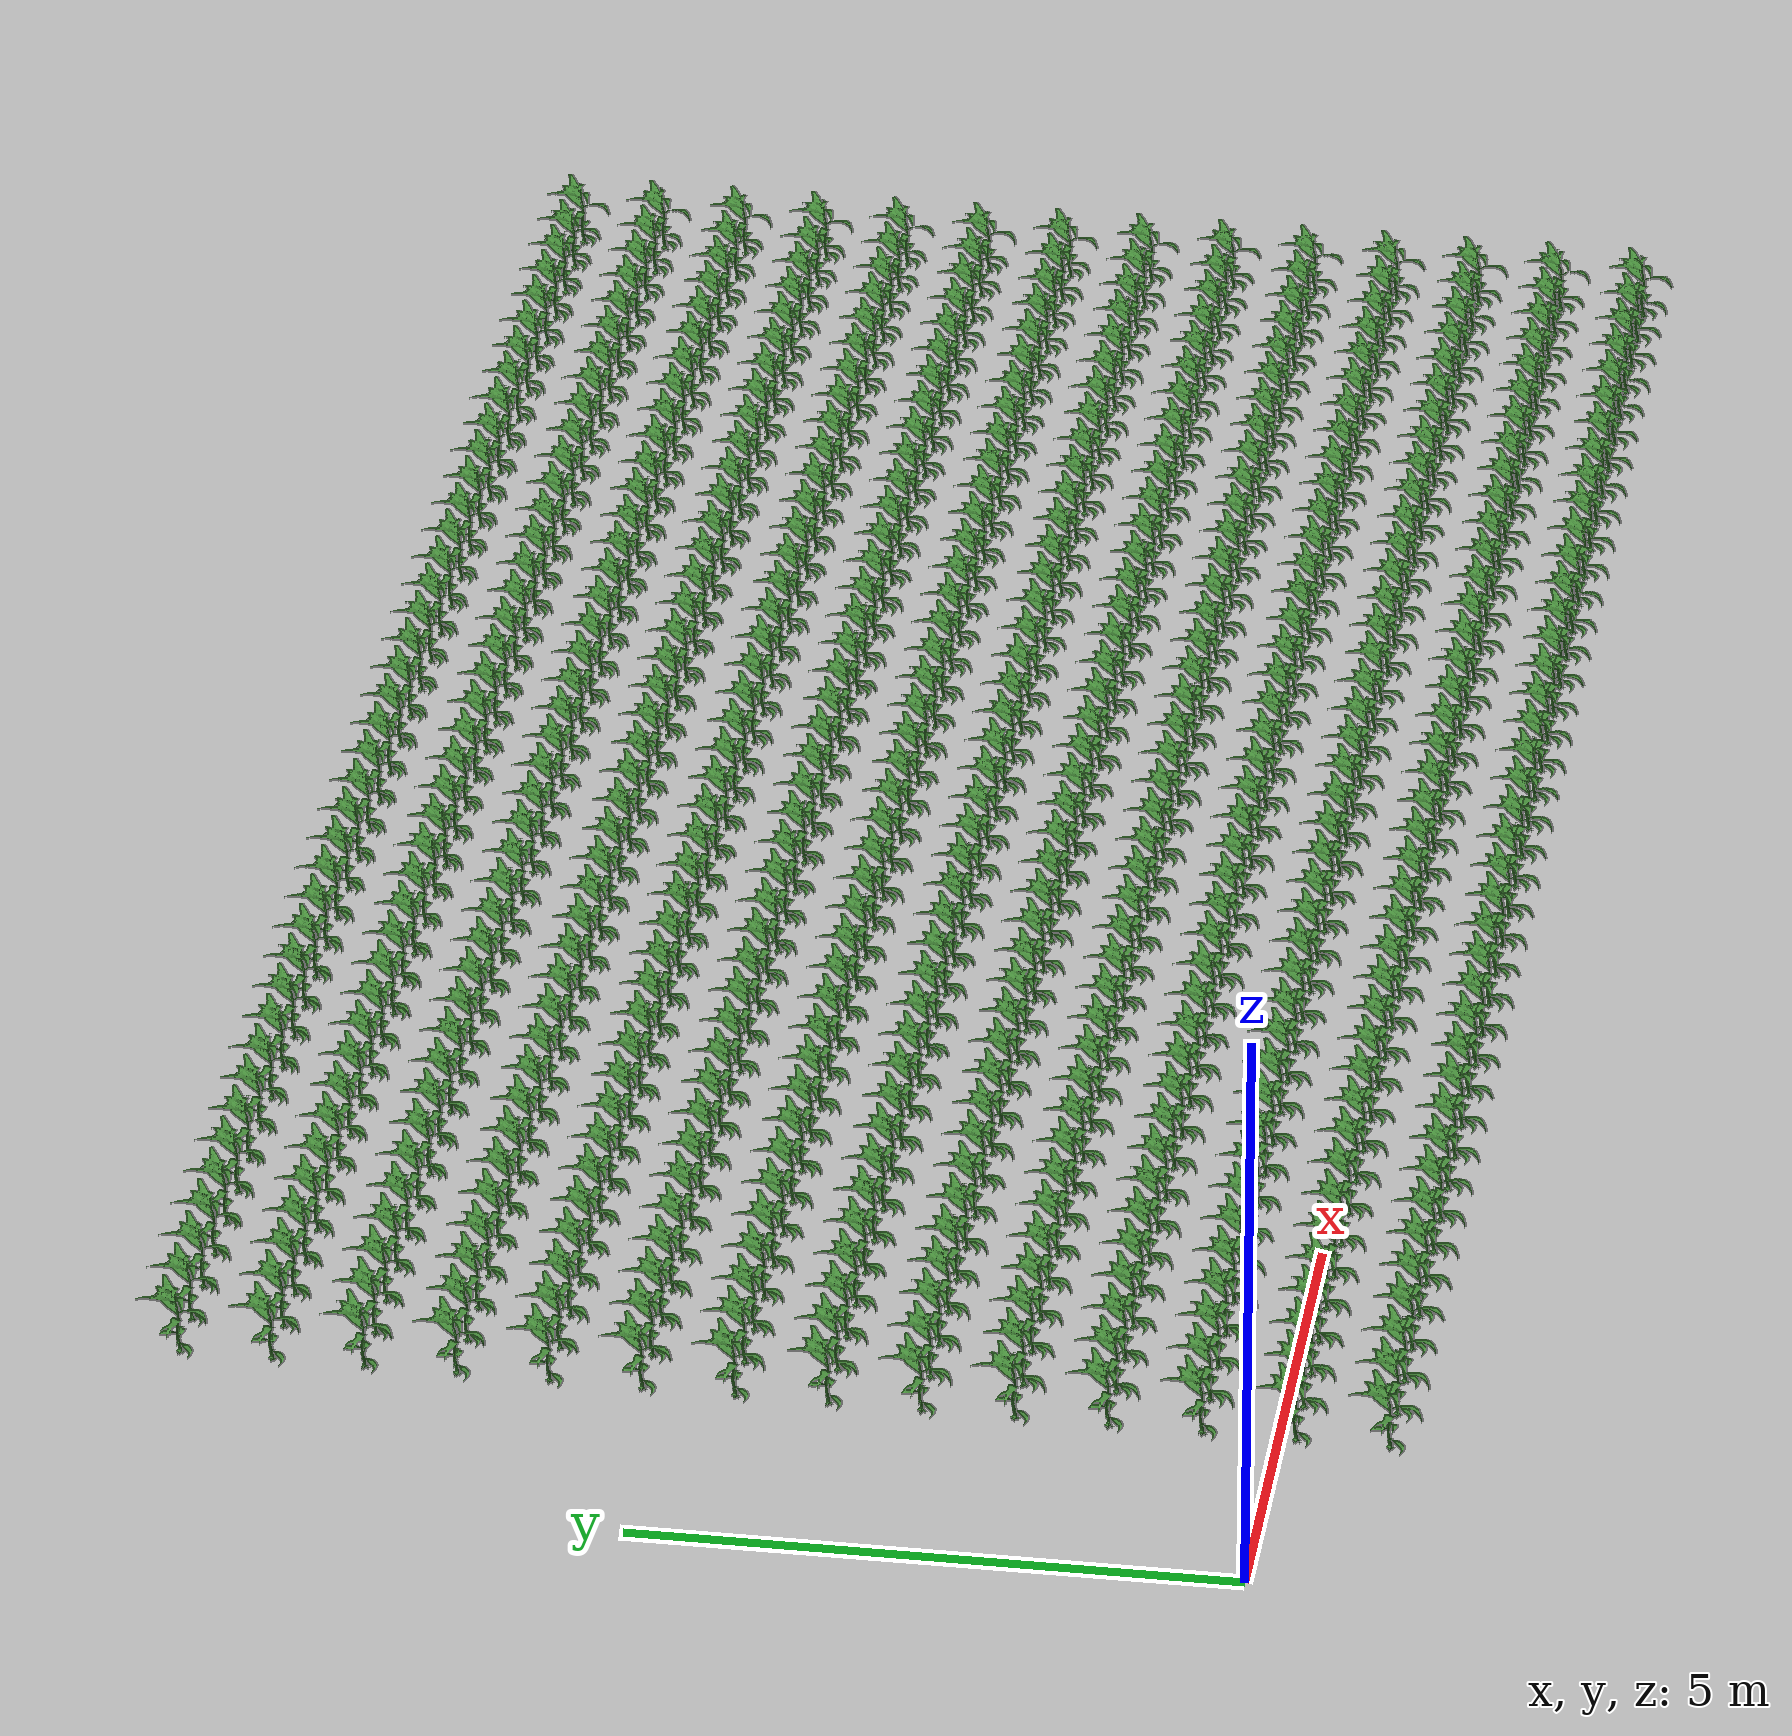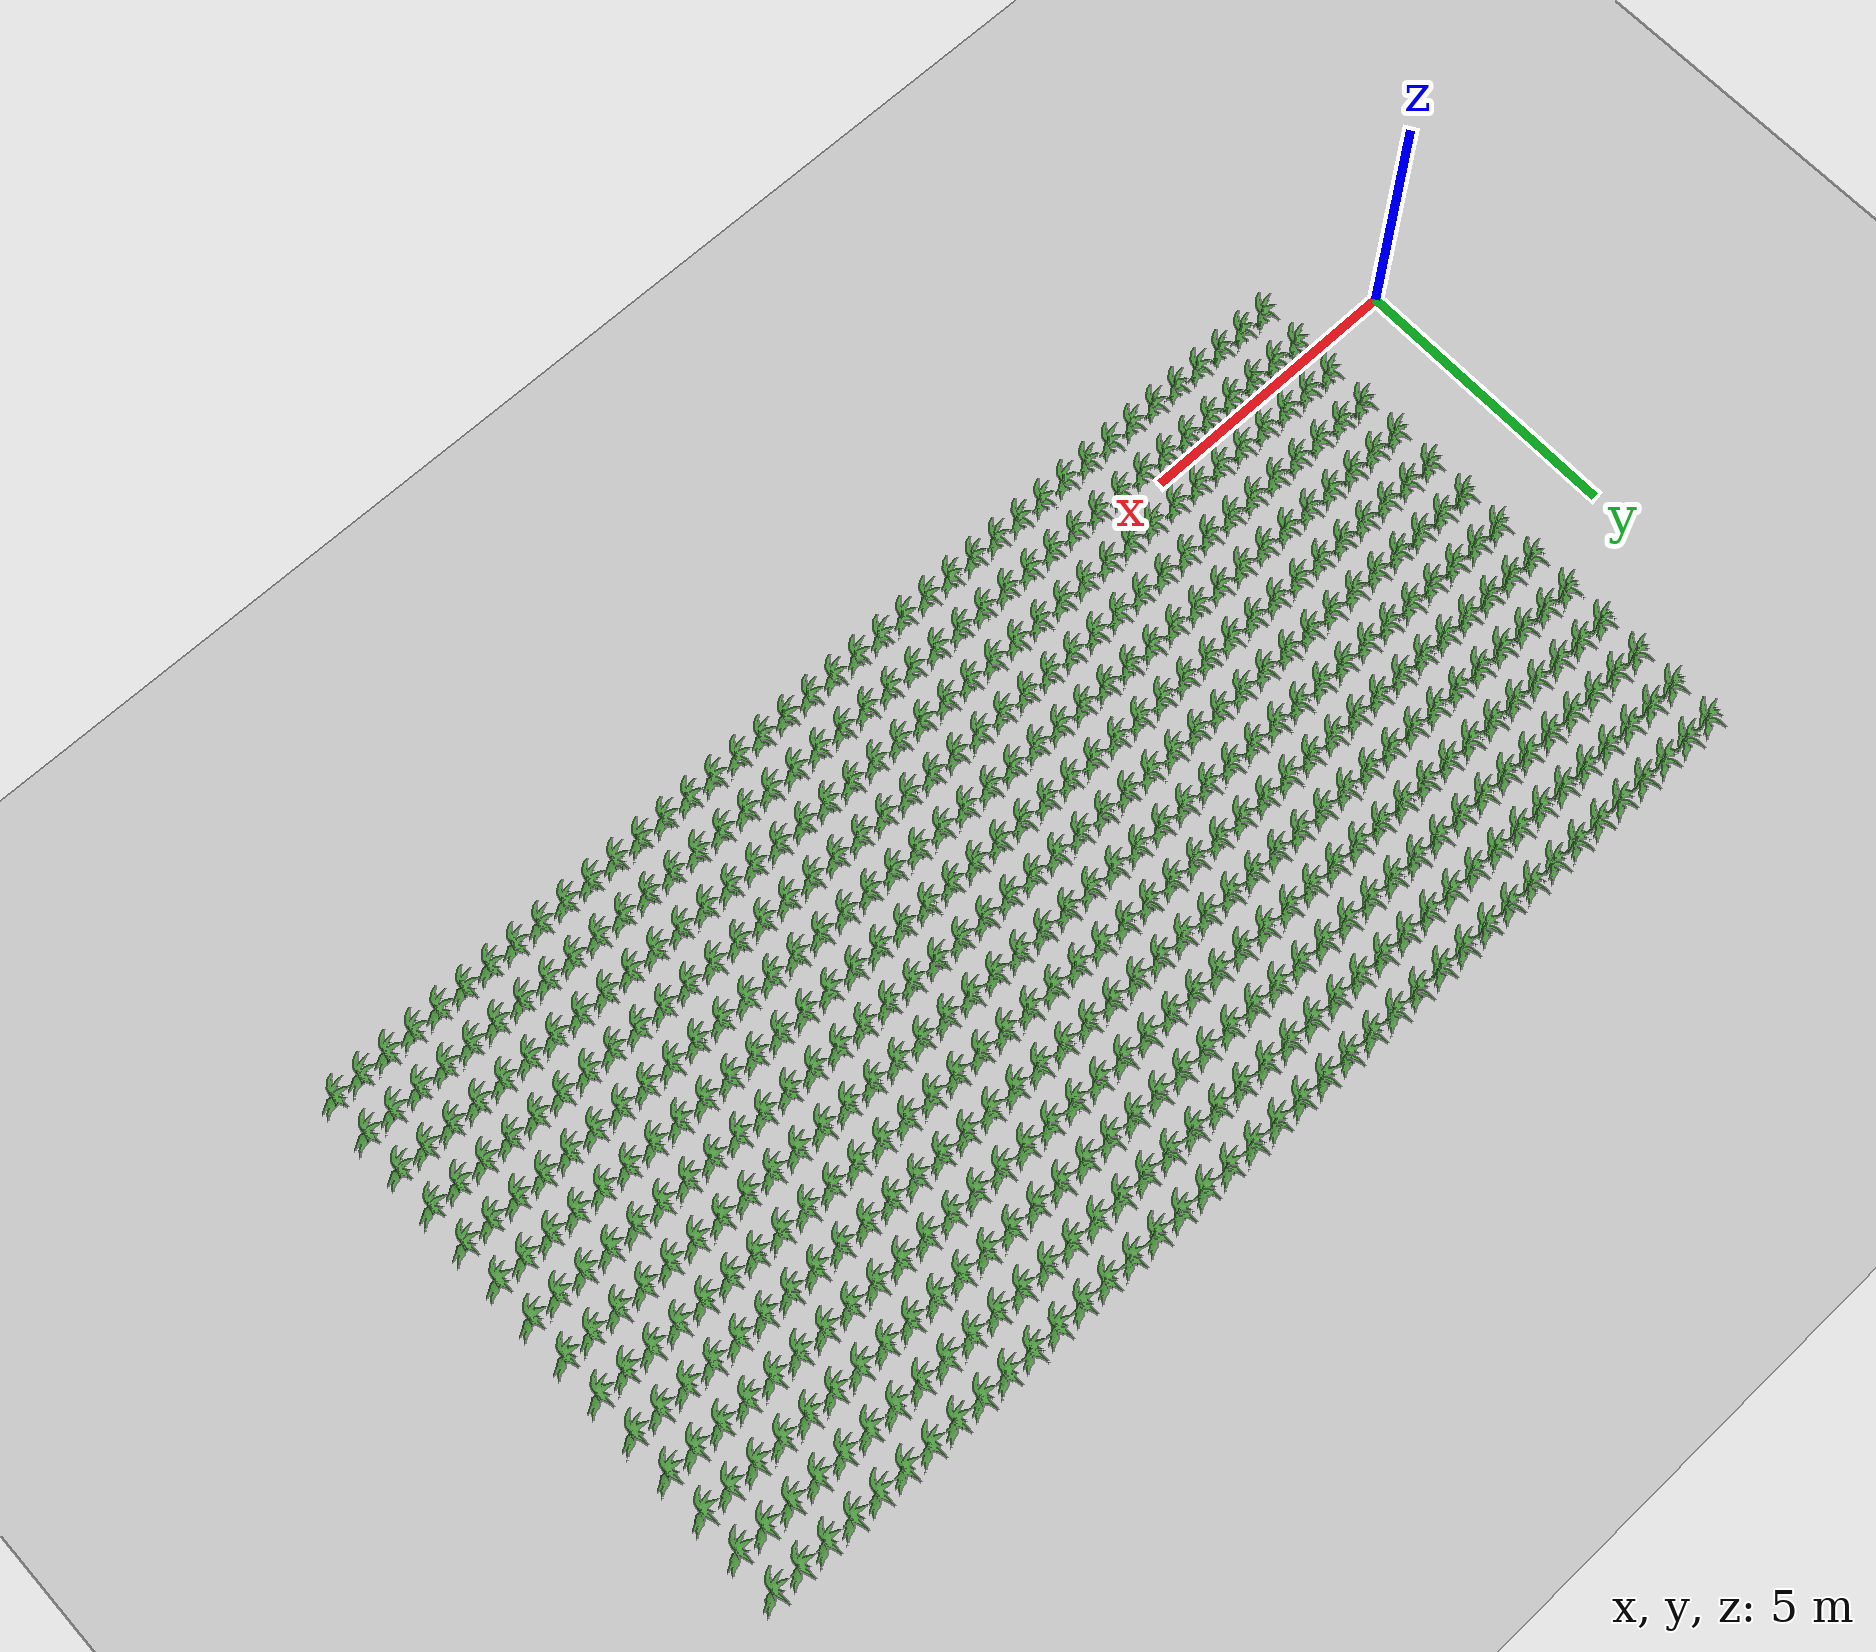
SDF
<sdf version="1.7">
 <world name="default">
  <light name="sun" type="directional">
   <pose>0 0 10 0 -0 0</pose>
   <diffuse>0.8 0.8 0.8 1</diffuse>
   <specular>0.2 0.2 0.2 1</specular>
   <attenuation>
    <range>1000</range>
    <constant>0.9</constant>
    <linear>0.01</linear>
    <quadratic>0.001</quadratic>
   </attenuation>
   <direction>-0.5 0.1 -0.9</direction>
   <spot><inner_angle>0</inner_angle><outer_angle>0</outer_angle><falloff>0</falloff></spot>
  </light>
  <model name="ground_plane">
   <static>1</static>
   <link name="link">
    <collision name="collision">
     <geometry><plane><normal>0 0 1</normal><size>100 100</size></plane></geometry>
     <surface>
      <contact><collide_bitmask>65535</collide_bitmask></contact>
      <friction><ode><mu>100</mu><mu2>50</mu2></ode></friction>
     </surface>
    </collision>
    <visual name="visual">
     <cast_shadows>0</cast_shadows>
     <geometry><plane><normal>0 0 1</normal><size>100 100</size></plane></geometry>
     <material>
      <script><uri>file://media/materials/scripts/gazebo.material</uri><name>Gazebo/Grey</name></script>
     </material>
    </visual>
   </link>
  </model>
  <gravity>0 0 -9.8</gravity>
  <magnetic_field>6e-06 2.3e-05 -4.2e-05</magnetic_field>
  <atmosphere type="adiabatic"/>
  <physics type="ode">
   <max_step_size>0.001</max_step_size>
   <real_time_factor>1</real_time_factor>
   <real_time_update_rate>1000</real_time_update_rate>
  </physics>
  <scene><ambient>0.4 0.4 0.4 1</ambient><background>0.7 0.7 0.7 1</background><shadows>1</shadows></scene>
  <spherical_coordinates>
   <surface_model>EARTH_WGS84</surface_model>
   <latitude_deg>0</latitude_deg>
   <longitude_deg>0</longitude_deg>
   <elevation>0</elevation>
   <heading_deg>0</heading_deg>
  </spherical_coordinates>
  <model name="bush_1_nc_0">
   <static>1</static>
   <link name="link">
    <visual name="visual">
     <geometry>
      <mesh><uri>model://corn_stalk/meshes/corn_1.obj</uri><scale>0.002 0.002 0.001</scale></mesh>
     </geometry>
     <material>
      <script><uri>file://media/materials/scripts/gazebo.material</uri><name>Gazebo/Grass</name></script>
     </material>
    </visual>
   </link>
   <pose>0.0 0.762 0.171977 0 -0 0</pose>
  </model>
  <model name="bush_1_nc_1">
   <static>1</static>
   <link name="link">
    <visual name="visual">
     <geometry>
      <mesh><uri>model://corn_stalk/meshes/corn_1.obj</uri><scale>0.002 0.002 0.001</scale></mesh>
     </geometry>
     <material>
      <script><uri>file://media/materials/scripts/gazebo.material</uri><name>Gazebo/Grass</name></script>
     </material>
    </visual>
   </link>
   <pose>0.5 0.762 0.171977 0 -0 0</pose>
  </model>
  <model name="bush_1_nc_2">
   <static>1</static>
   <link name="link">
    <visual name="visual">
     <geometry>
      <mesh><uri>model://corn_stalk/meshes/corn_1.obj</uri><scale>0.002 0.002 0.001</scale></mesh>
     </geometry>
     <material>
      <script><uri>file://media/materials/scripts/gazebo.material</uri><name>Gazebo/Grass</name></script>
     </material>
    </visual>
   </link>
   <pose>1.0 0.762 0.171977 0 -0 0</pose>
  </model>
  <model name="bush_1_nc_3">
   <static>1</static>
   <link name="link">
    <visual name="visual">
     <geometry>
      <mesh><uri>model://corn_stalk/meshes/corn_1.obj</uri><scale>0.002 0.002 0.001</scale></mesh>
     </geometry>
     <material>
      <script><uri>file://media/materials/scripts/gazebo.material</uri><name>Gazebo/Grass</name></script>
     </material>
    </visual>
   </link>
   <pose>1.5 0.762 0.171977 0 -0 0</pose>
  </model>
  <model name="bush_1_nc_4">
   <static>1</static>
   <link name="link">
    <visual name="visual">
     <geometry>
      <mesh><uri>model://corn_stalk/meshes/corn_1.obj</uri><scale>0.002 0.002 0.001</scale></mesh>
     </geometry>
     <material>
      <script><uri>file://media/materials/scripts/gazebo.material</uri><name>Gazebo/Grass</name></script>
     </material>
    </visual>
   </link>
   <pose>2.0 0.762 0.171977 0 -0 0</pose>
  </model>
  <model name="bush_1_nc_5">
   <static>1</static>
   <link name="link">
    <visual name="visual">
     <geometry>
      <mesh><uri>model://corn_stalk/meshes/corn_1.obj</uri><scale>0.002 0.002 0.001</scale></mesh>
     </geometry>
     <material>
      <script><uri>file://media/materials/scripts/gazebo.material</uri><name>Gazebo/Grass</name></script>
     </material>
    </visual>
   </link>
   <pose>2.5 0.762 0.171977 0 -0 0</pose>
  </model>
  <model name="bush_1_nc_6">
   <static>1</static>
   <link name="link">
    <visual name="visual">
     <geometry>
      <mesh><uri>model://corn_stalk/meshes/corn_1.obj</uri><scale>0.002 0.002 0.001</scale></mesh>
     </geometry>
     <material>
      <script><uri>file://media/materials/scripts/gazebo.material</uri><name>Gazebo/Grass</name></script>
     </material>
    </visual>
   </link>
   <pose>3.0 0.762 0.171977 0 -0 0</pose>
  </model>
  <model name="bush_1_nc_7">
   <static>1</static>
   <link name="link">
    <visual name="visual">
     <geometry>
      <mesh><uri>model://corn_stalk/meshes/corn_1.obj</uri><scale>0.002 0.002 0.001</scale></mesh>
     </geometry>
     <material>
      <script><uri>file://media/materials/scripts/gazebo.material</uri><name>Gazebo/Grass</name></script>
     </material>
    </visual>
   </link>
   <pose>3.5 0.762 0.171977 0 -0 0</pose>
  </model>
  <model name="bush_1_nc_8">
   <static>1</static>
   <link name="link">
    <visual name="visual">
     <geometry>
      <mesh><uri>model://corn_stalk/meshes/corn_1.obj</uri><scale>0.002 0.002 0.001</scale></mesh>
     </geometry>
     <material>
      <script><uri>file://media/materials/scripts/gazebo.material</uri><name>Gazebo/Grass</name></script>
     </material>
    </visual>
   </link>
   <pose>4.0 0.762 0.171977 0 -0 0</pose>
  </model>
  <model name="bush_1_nc_9">
   <static>1</static>
   <link name="link">
    <visual name="visual">
     <geometry>
      <mesh><uri>model://corn_stalk/meshes/corn_1.obj</uri><scale>0.002 0.002 0.001</scale></mesh>
     </geometry>
     <material>
      <script><uri>file://media/materials/scripts/gazebo.material</uri><name>Gazebo/Grass</name></script>
     </material>
    </visual>
   </link>
   <pose>4.5 0.762 0.171977 0 -0 0</pose>
  </model>
  <model name="bush_1_nc_10">
   <static>1</static>
   <link name="link">
    <visual name="visual">
     <geometry>
      <mesh><uri>model://corn_stalk/meshes/corn_1.obj</uri><scale>0.002 0.002 0.001</scale></mesh>
     </geometry>
     <material>
      <script><uri>file://media/materials/scripts/gazebo.material</uri><name>Gazebo/Grass</name></script>
     </material>
    </visual>
   </link>
   <pose>5.0 0.762 0.171977 0 -0 0</pose>
  </model>
  <model name="bush_1_nc_11">
   <static>1</static>
   <link name="link">
    <visual name="visual">
     <geometry>
      <mesh><uri>model://corn_stalk/meshes/corn_1.obj</uri><scale>0.002 0.002 0.001</scale></mesh>
     </geometry>
     <material>
      <script><uri>file://media/materials/scripts/gazebo.material</uri><name>Gazebo/Grass</name></script>
     </material>
    </visual>
   </link>
   <pose>5.5 0.762 0.171977 0 -0 0</pose>
  </model>
  <model name="bush_1_nc_12">
   <static>1</static>
   <link name="link">
    <visual name="visual">
     <geometry>
      <mesh><uri>model://corn_stalk/meshes/corn_1.obj</uri><scale>0.002 0.002 0.001</scale></mesh>
     </geometry>
     <material>
      <script><uri>file://media/materials/scripts/gazebo.material</uri><name>Gazebo/Grass</name></script>
     </material>
    </visual>
   </link>
   <pose>6.0 0.762 0.171977 0 -0 0</pose>
  </model>
  <model name="bush_1_nc_13">
   <static>1</static>
   <link name="link">
    <visual name="visual">
     <geometry>
      <mesh><uri>model://corn_stalk/meshes/corn_1.obj</uri><scale>0.002 0.002 0.001</scale></mesh>
     </geometry>
     <material>
      <script><uri>file://media/materials/scripts/gazebo.material</uri><name>Gazebo/Grass</name></script>
     </material>
    </visual>
   </link>
   <pose>6.5 0.762 0.171977 0 -0 0</pose>
  </model>
  <model name="bush_1_nc_14">
   <static>1</static>
   <link name="link">
    <visual name="visual">
     <geometry>
      <mesh><uri>model://corn_stalk/meshes/corn_1.obj</uri><scale>0.002 0.002 0.001</scale></mesh>
     </geometry>
     <material>
      <script><uri>file://media/materials/scripts/gazebo.material</uri><name>Gazebo/Grass</name></script>
     </material>
    </visual>
   </link>
   <pose>7.0 0.762 0.171977 0 -0 0</pose>
  </model>
  <model name="bush_1_nc_15">
   <static>1</static>
   <link name="link">
    <visual name="visual">
     <geometry>
      <mesh><uri>model://corn_stalk/meshes/corn_1.obj</uri><scale>0.002 0.002 0.001</scale></mesh>
     </geometry>
     <material>
      <script><uri>file://media/materials/scripts/gazebo.material</uri><name>Gazebo/Grass</name></script>
     </material>
    </visual>
   </link>
   <pose>7.5 0.762 0.171977 0 -0 0</pose>
  </model>
  <model name="bush_1_nc_16">
   <static>1</static>
   <link name="link">
    <visual name="visual">
     <geometry>
      <mesh><uri>model://corn_stalk/meshes/corn_1.obj</uri><scale>0.002 0.002 0.001</scale></mesh>
     </geometry>
     <material>
      <script><uri>file://media/materials/scripts/gazebo.material</uri><name>Gazebo/Grass</name></script>
     </material>
    </visual>
   </link>
   <pose>8.0 0.762 0.171977 0 -0 0</pose>
  </model>
  <model name="bush_1_nc_17">
   <static>1</static>
   <link name="link">
    <visual name="visual">
     <geometry>
      <mesh><uri>model://corn_stalk/meshes/corn_1.obj</uri><scale>0.002 0.002 0.001</scale></mesh>
     </geometry>
     <material>
      <script><uri>file://media/materials/scripts/gazebo.material</uri><name>Gazebo/Grass</name></script>
     </material>
    </visual>
   </link>
   <pose>8.5 0.762 0.171977 0 -0 0</pose>
  </model>
  <model name="bush_1_nc_18">
   <static>1</static>
   <link name="link">
    <visual name="visual">
     <geometry>
      <mesh><uri>model://corn_stalk/meshes/corn_1.obj</uri><scale>0.002 0.002 0.001</scale></mesh>
     </geometry>
     <material>
      <script><uri>file://media/materials/scripts/gazebo.material</uri><name>Gazebo/Grass</name></script>
     </material>
    </visual>
   </link>
   <pose>9.0 0.762 0.171977 0 -0 0</pose>
  </model>
  <model name="bush_1_nc_19">
   <static>1</static>
   <link name="link">
    <visual name="visual">
     <geometry>
      <mesh><uri>model://corn_stalk/meshes/corn_1.obj</uri><scale>0.002 0.002 0.001</scale></mesh>
     </geometry>
     <material>
      <script><uri>file://media/materials/scripts/gazebo.material</uri><name>Gazebo/Grass</name></script>
     </material>
    </visual>
   </link>
   <pose>9.5 0.762 0.171977 0 -0 0</pose>
  </model>
  <model name="bush_1_nc_20">
   <static>1</static>
   <link name="link">
    <visual name="visual">
     <geometry>
      <mesh><uri>model://corn_stalk/meshes/corn_1.obj</uri><scale>0.002 0.002 0.001</scale></mesh>
     </geometry>
     <material>
      <script><uri>file://media/materials/scripts/gazebo.material</uri><name>Gazebo/Grass</name></script>
     </material>
    </visual>
   </link>
   <pose>10.0 0.762 0.171977 0 -0 0</pose>
  </model>
  <model name="bush_1_nc_21">
   <static>1</static>
   <link name="link">
    <visual name="visual">
     <geometry>
      <mesh><uri>model://corn_stalk/meshes/corn_1.obj</uri><scale>0.002 0.002 0.001</scale></mesh>
     </geometry>
     <material>
      <script><uri>file://media/materials/scripts/gazebo.material</uri><name>Gazebo/Grass</name></script>
     </material>
    </visual>
   </link>
   <pose>10.5 0.762 0.171977 0 -0 0</pose>
  </model>
  <model name="bush_1_nc_22">
   <static>1</static>
   <link name="link">
    <visual name="visual">
     <geometry>
      <mesh><uri>model://corn_stalk/meshes/corn_1.obj</uri><scale>0.002 0.002 0.001</scale></mesh>
     </geometry>
     <material>
      <script><uri>file://media/materials/scripts/gazebo.material</uri><name>Gazebo/Grass</name></script>
     </material>
    </visual>
   </link>
   <pose>11.0 0.762 0.171977 0 -0 0</pose>
  </model>
  <model name="bush_1_nc_23">
   <static>1</static>
   <link name="link">
    <visual name="visual">
     <geometry>
      <mesh><uri>model://corn_stalk/meshes/corn_1.obj</uri><scale>0.002 0.002 0.001</scale></mesh>
     </geometry>
     <material>
      <script><uri>file://media/materials/scripts/gazebo.material</uri><name>Gazebo/Grass</name></script>
     </material>
    </visual>
   </link>
   <pose>11.5 0.762 0.171977 0 -0 0</pose>
  </model>
  <model name="bush_1_nc_24">
   <static>1</static>
   <link name="link">
    <visual name="visual">
     <geometry>
      <mesh><uri>model://corn_stalk/meshes/corn_1.obj</uri><scale>0.002 0.002 0.001</scale></mesh>
     </geometry>
     <material>
      <script><uri>file://media/materials/scripts/gazebo.material</uri><name>Gazebo/Grass</name></script>
     </material>
    </visual>
   </link>
   <pose>12.0 0.762 0.171977 0 -0 0</pose>
  </model>
  <model name="bush_1_nc_25">
   <static>1</static>
   <link name="link">
    <visual name="visual">
     <geometry>
      <mesh><uri>model://corn_stalk/meshes/corn_1.obj</uri><scale>0.002 0.002 0.001</scale></mesh>
     </geometry>
     <material>
      <script><uri>file://media/materials/scripts/gazebo.material</uri><name>Gazebo/Grass</name></script>
     </material>
    </visual>
   </link>
   <pose>12.5 0.762 0.171977 0 -0 0</pose>
  </model>
  <model name="bush_1_nc_26">
   <static>1</static>
   <link name="link">
    <visual name="visual">
     <geometry>
      <mesh><uri>model://corn_stalk/meshes/corn_1.obj</uri><scale>0.002 0.002 0.001</scale></mesh>
     </geometry>
     <material>
      <script><uri>file://media/materials/scripts/gazebo.material</uri><name>Gazebo/Grass</name></script>
     </material>
    </visual>
   </link>
   <pose>13.0 0.762 0.171977 0 -0 0</pose>
  </model>
  <model name="bush_1_nc_27">
   <static>1</static>
   <link name="link">
    <visual name="visual">
     <geometry>
      <mesh><uri>model://corn_stalk/meshes/corn_1.obj</uri><scale>0.002 0.002 0.001</scale></mesh>
     </geometry>
     <material>
      <script><uri>file://media/materials/scripts/gazebo.material</uri><name>Gazebo/Grass</name></script>
     </material>
    </visual>
   </link>
   <pose>13.5 0.762 0.171977 0 -0 0</pose>
  </model>
  <model name="bush_1_nc_28">
   <static>1</static>
   <link name="link">
    <visual name="visual">
     <geometry>
      <mesh><uri>model://corn_stalk/meshes/corn_1.obj</uri><scale>0.002 0.002 0.001</scale></mesh>
     </geometry>
     <material>
      <script><uri>file://media/materials/scripts/gazebo.material</uri><name>Gazebo/Grass</name></script>
     </material>
    </visual>
   </link>
   <pose>14.0 0.762 0.171977 0 -0 0</pose>
  </model>
  <model name="bush_1_nc_29">
   <static>1</static>
   <link name="link">
    <visual name="visual">
     <geometry>
      <mesh><uri>model://corn_stalk/meshes/corn_1.obj</uri><scale>0.002 0.002 0.001</scale></mesh>
     </geometry>
     <material>
      <script><uri>file://media/materials/scripts/gazebo.material</uri><name>Gazebo/Grass</name></script>
     </material>
    </visual>
   </link>
   <pose>14.5 0.762 0.171977 0 -0 0</pose>
  </model>
  <model name="bush_1_nc_30">
   <static>1</static>
   <link name="link">
    <visual name="visual">
     <geometry>
      <mesh><uri>model://corn_stalk/meshes/corn_1.obj</uri><scale>0.002 0.002 0.001</scale></mesh>
     </geometry>
     <material>
      <script><uri>file://media/materials/scripts/gazebo.material</uri><name>Gazebo/Grass</name></script>
     </material>
    </visual>
   </link>
   <pose>15.0 0.762 0.171977 0 -0 0</pose>
  </model>
  <model name="bush_1_nc_31">
   <static>1</static>
   <link name="link">
    <visual name="visual">
     <geometry>
      <mesh><uri>model://corn_stalk/meshes/corn_1.obj</uri><scale>0.002 0.002 0.001</scale></mesh>
     </geometry>
     <material>
      <script><uri>file://media/materials/scripts/gazebo.material</uri><name>Gazebo/Grass</name></script>
     </material>
    </visual>
   </link>
   <pose>15.5 0.762 0.171977 0 -0 0</pose>
  </model>
  <model name="bush_1_nc_32">
   <static>1</static>
   <link name="link">
    <visual name="visual">
     <geometry>
      <mesh><uri>model://corn_stalk/meshes/corn_1.obj</uri><scale>0.002 0.002 0.001</scale></mesh>
     </geometry>
     <material>
      <script><uri>file://media/materials/scripts/gazebo.material</uri><name>Gazebo/Grass</name></script>
     </material>
    </visual>
   </link>
   <pose>16.0 0.762 0.171977 0 -0 0</pose>
  </model>
  <model name="bush_1_nc_33">
   <static>1</static>
   <link name="link">
    <visual name="visual">
     <geometry>
      <mesh><uri>model://corn_stalk/meshes/corn_1.obj</uri><scale>0.002 0.002 0.001</scale></mesh>
     </geometry>
     <material>
      <script><uri>file://media/materials/scripts/gazebo.material</uri><name>Gazebo/Grass</name></script>
     </material>
    </visual>
   </link>
   <pose>16.5 0.762 0.171977 0 -0 0</pose>
  </model>
  <model name="bush_1_nc_34">
   <static>1</static>
   <link name="link">
    <visual name="visual">
     <geometry>
      <mesh><uri>model://corn_stalk/meshes/corn_1.obj</uri><scale>0.002 0.002 0.001</scale></mesh>
     </geometry>
     <material>
      <script><uri>file://media/materials/scripts/gazebo.material</uri><name>Gazebo/Grass</name></script>
     </material>
    </visual>
   </link>
   <pose>17.0 0.762 0.171977 0 -0 0</pose>
  </model>
  <model name="bush_1_nc_35">
   <static>1</static>
   <link name="link">
    <visual name="visual">
     <geometry>
      <mesh><uri>model://corn_stalk/meshes/corn_1.obj</uri><scale>0.002 0.002 0.001</scale></mesh>
     </geometry>
     <material>
      <script><uri>file://media/materials/scripts/gazebo.material</uri><name>Gazebo/Grass</name></script>
     </material>
    </visual>
   </link>
   <pose>17.5 0.762 0.171977 0 -0 0</pose>
  </model>
  <model name="bush_1_nc_36">
   <static>1</static>
   <link name="link">
    <visual name="visual">
     <geometry>
      <mesh><uri>model://corn_stalk/meshes/corn_1.obj</uri><scale>0.002 0.002 0.001</scale></mesh>
     </geometry>
     <material>
      <script><uri>file://media/materials/scripts/gazebo.material</uri><name>Gazebo/Grass</name></script>
     </material>
    </visual>
   </link>
   <pose>18.0 0.762 0.171977 0 -0 0</pose>
  </model>
  <model name="bush_1_nc_37">
   <static>1</static>
   <link name="link">
    <visual name="visual">
     <geometry>
      <mesh><uri>model://corn_stalk/meshes/corn_1.obj</uri><scale>0.002 0.002 0.001</scale></mesh>
     </geometry>
     <material>
      <script><uri>file://media/materials/scripts/gazebo.material</uri><name>Gazebo/Grass</name></script>
     </material>
    </visual>
   </link>
   <pose>18.5 0.762 0.171977 0 -0 0</pose>
  </model>
  <model name="bush_1_nc_38">
   <static>1</static>
   <link name="link">
    <visual name="visual">
     <geometry>
      <mesh><uri>model://corn_stalk/meshes/corn_1.obj</uri><scale>0.002 0.002 0.001</scale></mesh>
     </geometry>
     <material>
      <script><uri>file://media/materials/scripts/gazebo.material</uri><name>Gazebo/Grass</name></script>
     </material>
    </visual>
   </link>
   <pose>19.0 0.762 0.171977 0 -0 0</pose>
  </model>
  <model name="bush_1_nc_39">
   <static>1</static>
   <link name="link">
    <visual name="visual">
     <geometry>
      <mesh><uri>model://corn_stalk/meshes/corn_1.obj</uri><scale>0.002 0.002 0.001</scale></mesh>
     </geometry>
     <material>
      <script><uri>file://media/materials/scripts/gazebo.material</uri><name>Gazebo/Grass</name></script>
     </material>
    </visual>
   </link>
   <pose>19.5 0.762 0.171977 0 -0 0</pose>
  </model>
  <model name="bush_1_nc_40">
   <static>1</static>
   <link name="link">
    <visual name="visual">
     <geometry>
      <mesh><uri>model://corn_stalk/meshes/corn_1.obj</uri><scale>0.002 0.002 0.001</scale></mesh>
     </geometry>
     <material>
      <script><uri>file://media/materials/scripts/gazebo.material</uri><name>Gazebo/Grass</name></script>
     </material>
    </visual>
   </link>
   <pose>0.0 1.524 0.171977 0 -0 0</pose>
  </model>
  <model name="bush_1_nc_41">
   <static>1</static>
   <link name="link">
    <visual name="visual">
     <geometry>
      <mesh><uri>model://corn_stalk/meshes/corn_1.obj</uri><scale>0.002 0.002 0.001</scale></mesh>
     </geometry>
     <material>
      <script><uri>file://media/materials/scripts/gazebo.material</uri><name>Gazebo/Grass</name></script>
     </material>
    </visual>
   </link>
   <pose>0.5 1.524 0.171977 0 -0 0</pose>
  </model>
  <model name="bush_1_nc_42">
   <static>1</static>
   <link name="link">
    <visual name="visual">
     <geometry>
      <mesh><uri>model://corn_stalk/meshes/corn_1.obj</uri><scale>0.002 0.002 0.001</scale></mesh>
     </geometry>
     <material>
      <script><uri>file://media/materials/scripts/gazebo.material</uri><name>Gazebo/Grass</name></script>
     </material>
    </visual>
   </link>
   <pose>1.0 1.524 0.171977 0 -0 0</pose>
  </model>
  <model name="bush_1_nc_43">
   <static>1</static>
   <link name="link">
    <visual name="visual">
     <geometry>
      <mesh><uri>model://corn_stalk/meshes/corn_1.obj</uri><scale>0.002 0.002 0.001</scale></mesh>
     </geometry>
     <material>
      <script><uri>file://media/materials/scripts/gazebo.material</uri><name>Gazebo/Grass</name></script>
     </material>
    </visual>
   </link>
   <pose>1.5 1.524 0.171977 0 -0 0</pose>
  </model>
  <model name="bush_1_nc_44">
   <static>1</static>
   <link name="link">
    <visual name="visual">
     <geometry>
      <mesh><uri>model://corn_stalk/meshes/corn_1.obj</uri><scale>0.002 0.002 0.001</scale></mesh>
     </geometry>
     <material>
      <script><uri>file://media/materials/scripts/gazebo.material</uri><name>Gazebo/Grass</name></script>
     </material>
    </visual>
   </link>
   <pose>2.0 1.524 0.171977 0 -0 0</pose>
  </model>
  <model name="bush_1_nc_45">
   <static>1</static>
   <link name="link">
    <visual name="visual">
     <geometry>
      <mesh><uri>model://corn_stalk/meshes/corn_1.obj</uri><scale>0.002 0.002 0.001</scale></mesh>
     </geometry>
     <material>
      <script><uri>file://media/materials/scripts/gazebo.material</uri><name>Gazebo/Grass</name></script>
     </material>
    </visual>
   </link>
   <pose>2.5 1.524 0.171977 0 -0 0</pose>
  </model>
  <model name="bush_1_nc_46">
   <static>1</static>
   <link name="link">
    <visual name="visual">
     <geometry>
      <mesh><uri>model://corn_stalk/meshes/corn_1.obj</uri><scale>0.002 0.002 0.001</scale></mesh>
     </geometry>
     <material>
      <script><uri>file://media/materials/scripts/gazebo.material</uri><name>Gazebo/Grass</name></script>
     </material>
    </visual>
   </link>
   <pose>3.0 1.524 0.171977 0 -0 0</pose>
  </model>
  <model name="bush_1_nc_47">
   <static>1</static>
   <link name="link">
    <visual name="visual">
     <geometry>
      <mesh><uri>model://corn_stalk/meshes/corn_1.obj</uri><scale>0.002 0.002 0.001</scale></mesh>
     </geometry>
     <material>
      <script><uri>file://media/materials/scripts/gazebo.material</uri><name>Gazebo/Grass</name></script>
     </material>
    </visual>
   </link>
   <pose>3.5 1.524 0.171977 0 -0 0</pose>
  </model>
  <model name="bush_1_nc_48">
   <static>1</static>
   <link name="link">
    <visual name="visual">
     <geometry>
      <mesh><uri>model://corn_stalk/meshes/corn_1.obj</uri><scale>0.002 0.002 0.001</scale></mesh>
     </geometry>
     <material>
      <script><uri>file://media/materials/scripts/gazebo.material</uri><name>Gazebo/Grass</name></script>
     </material>
    </visual>
   </link>
   <pose>4.0 1.524 0.171977 0 -0 0</pose>
  </model>
  <model name="bush_1_nc_49">
   <static>1</static>
   <link name="link">
    <visual name="visual">
     <geometry>
      <mesh><uri>model://corn_stalk/meshes/corn_1.obj</uri><scale>0.002 0.002 0.001</scale></mesh>
     </geometry>
     <material>
      <script><uri>file://media/materials/scripts/gazebo.material</uri><name>Gazebo/Grass</name></script>
     </material>
    </visual>
   </link>
   <pose>4.5 1.524 0.171977 0 -0 0</pose>
  </model>
  <model name="bush_1_nc_50">
   <static>1</static>
   <link name="link">
    <visual name="visual">
     <geometry>
      <mesh><uri>model://corn_stalk/meshes/corn_1.obj</uri><scale>0.002 0.002 0.001</scale></mesh>
     </geometry>
     <material>
      <script><uri>file://media/materials/scripts/gazebo.material</uri><name>Gazebo/Grass</name></script>
     </material>
    </visual>
   </link>
   <pose>5.0 1.524 0.171977 0 -0 0</pose>
  </model>
  <model name="bush_1_nc_51">
   <static>1</static>
   <link name="link">
    <visual name="visual">
     <geometry>
      <mesh><uri>model://corn_stalk/meshes/corn_1.obj</uri><scale>0.002 0.002 0.001</scale></mesh>
     </geometry>
     <material>
      <script><uri>file://media/materials/scripts/gazebo.material</uri><name>Gazebo/Grass</name></script>
     </material>
    </visual>
   </link>
   <pose>5.5 1.524 0.171977 0 -0 0</pose>
  </model>
  <model name="bush_1_nc_52">
   <static>1</static>
   <link name="link">
    <visual name="visual">
     <geometry>
      <mesh><uri>model://corn_stalk/meshes/corn_1.obj</uri><scale>0.002 0.002 0.001</scale></mesh>
     </geometry>
     <material>
      <script><uri>file://media/materials/scripts/gazebo.material</uri><name>Gazebo/Grass</name></script>
     </material>
    </visual>
   </link>
   <pose>6.0 1.524 0.171977 0 -0 0</pose>
  </model>
  <model name="bush_1_nc_53">
   <static>1</static>
   <link name="link">
    <visual name="visual">
     <geometry>
      <mesh><uri>model://corn_stalk/meshes/corn_1.obj</uri><scale>0.002 0.002 0.001</scale></mesh>
     </geometry>
     <material>
      <script><uri>file://media/materials/scripts/gazebo.material</uri><name>Gazebo/Grass</name></script>
     </material>
    </visual>
   </link>
   <pose>6.5 1.524 0.171977 0 -0 0</pose>
  </model>
  <model name="bush_1_nc_54">
   <static>1</static>
   <link name="link">
    <visual name="visual">
     <geometry>
      <mesh><uri>model://corn_stalk/meshes/corn_1.obj</uri><scale>0.002 0.002 0.001</scale></mesh>
     </geometry>
     <material>
      <script><uri>file://media/materials/scripts/gazebo.material</uri><name>Gazebo/Grass</name></script>
     </material>
    </visual>
   </link>
   <pose>7.0 1.524 0.171977 0 -0 0</pose>
  </model>
  <model name="bush_1_nc_55">
   <static>1</static>
   <link name="link">
    <visual name="visual">
     <geometry>
      <mesh><uri>model://corn_stalk/meshes/corn_1.obj</uri><scale>0.002 0.002 0.001</scale></mesh>
     </geometry>
     <material>
      <script><uri>file://media/materials/scripts/gazebo.material</uri><name>Gazebo/Grass</name></script>
     </material>
    </visual>
   </link>
   <pose>7.5 1.524 0.171977 0 -0 0</pose>
  </model>
  <model name="bush_1_nc_56">
   <static>1</static>
   <link name="link">
    <visual name="visual">
     <geometry>
      <mesh><uri>model://corn_stalk/meshes/corn_1.obj</uri><scale>0.002 0.002 0.001</scale></mesh>
     </geometry>
     <material>
      <script><uri>file://media/materials/scripts/gazebo.material</uri><name>Gazebo/Grass</name></script>
     </material>
    </visual>
   </link>
   <pose>8.0 1.524 0.171977 0 -0 0</pose>
  </model>
  <model name="bush_1_nc_57">
   <static>1</static>
   <link name="link">
    <visual name="visual">
     <geometry>
      <mesh><uri>model://corn_stalk/meshes/corn_1.obj</uri><scale>0.002 0.002 0.001</scale></mesh>
     </geometry>
     <material>
      <script><uri>file://media/materials/scripts/gazebo.material</uri><name>Gazebo/Grass</name></script>
     </material>
    </visual>
   </link>
   <pose>8.5 1.524 0.171977 0 -0 0</pose>
  </model>
  <model name="bush_1_nc_58">
   <static>1</static>
   <link name="link">
    <visual name="visual">
     <geometry>
      <mesh><uri>model://corn_stalk/meshes/corn_1.obj</uri><scale>0.002 0.002 0.001</scale></mesh>
     </geometry>
     <material>
      <script><uri>file://media/materials/scripts/gazebo.material</uri><name>Gazebo/Grass</name></script>
     </material>
    </visual>
   </link>
   <pose>9.0 1.524 0.171977 0 -0 0</pose>
  </model>
  <model name="bush_1_nc_59">
   <static>1</static>
   <link name="link">
    <visual name="visual">
     <geometry>
      <mesh><uri>model://corn_stalk/meshes/corn_1.obj</uri><scale>0.002 0.002 0.001</scale></mesh>
     </geometry>
     <material>
      <script><uri>file://media/materials/scripts/gazebo.material</uri><name>Gazebo/Grass</name></script>
     </material>
    </visual>
   </link>
   <pose>9.5 1.524 0.171977 0 -0 0</pose>
  </model>
  <model name="bush_1_nc_60">
   <static>1</static>
   <link name="link">
    <visual name="visual">
     <geometry>
      <mesh><uri>model://corn_stalk/meshes/corn_1.obj</uri><scale>0.002 0.002 0.001</scale></mesh>
     </geometry>
     <material>
      <script><uri>file://media/materials/scripts/gazebo.material</uri><name>Gazebo/Grass</name></script>
     </material>
    </visual>
   </link>
   <pose>10.0 1.524 0.171977 0 -0 0</pose>
  </model>
  <model name="bush_1_nc_61">
   <static>1</static>
   <link name="link">
    <visual name="visual">
     <geometry>
      <mesh><uri>model://corn_stalk/meshes/corn_1.obj</uri><scale>0.002 0.002 0.001</scale></mesh>
     </geometry>
     <material>
      <script><uri>file://media/materials/scripts/gazebo.material</uri><name>Gazebo/Grass</name></script>
     </material>
    </visual>
   </link>
   <pose>10.5 1.524 0.171977 0 -0 0</pose>
  </model>
  <model name="bush_1_nc_62">
   <static>1</static>
   <link name="link">
    <visual name="visual">
     <geometry>
      <mesh><uri>model://corn_stalk/meshes/corn_1.obj</uri><scale>0.002 0.002 0.001</scale></mesh>
     </geometry>
     <material>
      <script><uri>file://media/materials/scripts/gazebo.material</uri><name>Gazebo/Grass</name></script>
     </material>
    </visual>
   </link>
   <pose>11.0 1.524 0.171977 0 -0 0</pose>
  </model>
  <model name="bush_1_nc_63">
   <static>1</static>
   <link name="link">
    <visual name="visual">
     <geometry>
      <mesh><uri>model://corn_stalk/meshes/corn_1.obj</uri><scale>0.002 0.002 0.001</scale></mesh>
     </geometry>
     <material>
      <script><uri>file://media/materials/scripts/gazebo.material</uri><name>Gazebo/Grass</name></script>
     </material>
    </visual>
   </link>
   <pose>11.5 1.524 0.171977 0 -0 0</pose>
  </model>
  <model name="bush_1_nc_64">
   <static>1</static>
   <link name="link">
    <visual name="visual">
     <geometry>
      <mesh><uri>model://corn_stalk/meshes/corn_1.obj</uri><scale>0.002 0.002 0.001</scale></mesh>
     </geometry>
     <material>
      <script><uri>file://media/materials/scripts/gazebo.material</uri><name>Gazebo/Grass</name></script>
     </material>
    </visual>
   </link>
   <pose>12.0 1.524 0.171977 0 -0 0</pose>
  </model>
  <model name="bush_1_nc_65">
   <static>1</static>
   <link name="link">
    <visual name="visual">
     <geometry>
      <mesh><uri>model://corn_stalk/meshes/corn_1.obj</uri><scale>0.002 0.002 0.001</scale></mesh>
     </geometry>
     <material>
      <script><uri>file://media/materials/scripts/gazebo.material</uri><name>Gazebo/Grass</name></script>
     </material>
    </visual>
   </link>
   <pose>12.5 1.524 0.171977 0 -0 0</pose>
  </model>
  <model name="bush_1_nc_66">
   <static>1</static>
   <link name="link">
    <visual name="visual">
     <geometry>
      <mesh><uri>model://corn_stalk/meshes/corn_1.obj</uri><scale>0.002 0.002 0.001</scale></mesh>
     </geometry>
     <material>
      <script><uri>file://media/materials/scripts/gazebo.material</uri><name>Gazebo/Grass</name></script>
     </material>
    </visual>
   </link>
   <pose>13.0 1.524 0.171977 0 -0 0</pose>
  </model>
  <model name="bush_1_nc_67">
   <static>1</static>
   <link name="link">
    <visual name="visual">
     <geometry>
      <mesh><uri>model://corn_stalk/meshes/corn_1.obj</uri><scale>0.002 0.002 0.001</scale></mesh>
     </geometry>
     <material>
      <script><uri>file://media/materials/scripts/gazebo.material</uri><name>Gazebo/Grass</name></script>
     </material>
    </visual>
   </link>
   <pose>13.5 1.524 0.171977 0 -0 0</pose>
  </model>
  <model name="bush_1_nc_68">
   <static>1</static>
   <link name="link">
    <visual name="visual">
     <geometry>
      <mesh><uri>model://corn_stalk/meshes/corn_1.obj</uri><scale>0.002 0.002 0.001</scale></mesh>
     </geometry>
     <material>
      <script><uri>file://media/materials/scripts/gazebo.material</uri><name>Gazebo/Grass</name></script>
     </material>
    </visual>
   </link>
   <pose>14.0 1.524 0.171977 0 -0 0</pose>
  </model>
  <model name="bush_1_nc_69">
   <static>1</static>
   <link name="link">
    <visual name="visual">
     <geometry>
      <mesh><uri>model://corn_stalk/meshes/corn_1.obj</uri><scale>0.002 0.002 0.001</scale></mesh>
     </geometry>
     <material>
      <script><uri>file://media/materials/scripts/gazebo.material</uri><name>Gazebo/Grass</name></script>
     </material>
    </visual>
   </link>
   <pose>14.5 1.524 0.171977 0 -0 0</pose>
  </model>
  <model name="bush_1_nc_70">
   <static>1</static>
   <link name="link">
    <visual name="visual">
     <geometry>
      <mesh><uri>model://corn_stalk/meshes/corn_1.obj</uri><scale>0.002 0.002 0.001</scale></mesh>
     </geometry>
     <material>
      <script><uri>file://media/materials/scripts/gazebo.material</uri><name>Gazebo/Grass</name></script>
     </material>
    </visual>
   </link>
   <pose>15.0 1.524 0.171977 0 -0 0</pose>
  </model>
  <model name="bush_1_nc_71">
   <static>1</static>
   <link name="link">
    <visual name="visual">
     <geometry>
      <mesh><uri>model://corn_stalk/meshes/corn_1.obj</uri><scale>0.002 0.002 0.001</scale></mesh>
     </geometry>
     <material>
      <script><uri>file://media/materials/scripts/gazebo.material</uri><name>Gazebo/Grass</name></script>
     </material>
    </visual>
   </link>
   <pose>15.5 1.524 0.171977 0 -0 0</pose>
  </model>
  <model name="bush_1_nc_72">
   <static>1</static>
   <link name="link">
    <visual name="visual">
     <geometry>
      <mesh><uri>model://corn_stalk/meshes/corn_1.obj</uri><scale>0.002 0.002 0.001</scale></mesh>
     </geometry>
     <material>
      <script><uri>file://media/materials/scripts/gazebo.material</uri><name>Gazebo/Grass</name></script>
     </material>
    </visual>
   </link>
   <pose>16.0 1.524 0.171977 0 -0 0</pose>
  </model>
  <model name="bush_1_nc_73">
   <static>1</static>
   <link name="link">
    <visual name="visual">
     <geometry>
      <mesh><uri>model://corn_stalk/meshes/corn_1.obj</uri><scale>0.002 0.002 0.001</scale></mesh>
     </geometry>
     <material>
      <script><uri>file://media/materials/scripts/gazebo.material</uri><name>Gazebo/Grass</name></script>
     </material>
    </visual>
   </link>
   <pose>16.5 1.524 0.171977 0 -0 0</pose>
  </model>
  <model name="bush_1_nc_74">
   <static>1</static>
   <link name="link">
    <visual name="visual">
     <geometry>
      <mesh><uri>model://corn_stalk/meshes/corn_1.obj</uri><scale>0.002 0.002 0.001</scale></mesh>
     </geometry>
     <material>
      <script><uri>file://media/materials/scripts/gazebo.material</uri><name>Gazebo/Grass</name></script>
     </material>
    </visual>
   </link>
   <pose>17.0 1.524 0.171977 0 -0 0</pose>
  </model>
  <model name="bush_1_nc_75">
   <static>1</static>
   <link name="link">
    <visual name="visual">
     <geometry>
      <mesh><uri>model://corn_stalk/meshes/corn_1.obj</uri><scale>0.002 0.002 0.001</scale></mesh>
     </geometry>
     <material>
      <script><uri>file://media/materials/scripts/gazebo.material</uri><name>Gazebo/Grass</name></script>
     </material>
    </visual>
   </link>
   <pose>17.5 1.524 0.171977 0 -0 0</pose>
  </model>
  <model name="bush_1_nc_76">
   <static>1</static>
   <link name="link">
    <visual name="visual">
     <geometry>
      <mesh><uri>model://corn_stalk/meshes/corn_1.obj</uri><scale>0.002 0.002 0.001</scale></mesh>
     </geometry>
     <material>
      <script><uri>file://media/materials/scripts/gazebo.material</uri><name>Gazebo/Grass</name></script>
     </material>
    </visual>
   </link>
   <pose>18.0 1.524 0.171977 0 -0 0</pose>
  </model>
  <model name="bush_1_nc_77">
   <static>1</static>
   <link name="link">
    <visual name="visual">
     <geometry>
      <mesh><uri>model://corn_stalk/meshes/corn_1.obj</uri><scale>0.002 0.002 0.001</scale></mesh>
     </geometry>
     <material>
      <script><uri>file://media/materials/scripts/gazebo.material</uri><name>Gazebo/Grass</name></script>
     </material>
    </visual>
   </link>
   <pose>18.5 1.524 0.171977 0 -0 0</pose>
  </model>
  <model name="bush_1_nc_78">
   <static>1</static>
   <link name="link">
    <visual name="visual">
     <geometry>
      <mesh><uri>model://corn_stalk/meshes/corn_1.obj</uri><scale>0.002 0.002 0.001</scale></mesh>
     </geometry>
     <material>
      <script><uri>file://media/materials/scripts/gazebo.material</uri><name>Gazebo/Grass</name></script>
     </material>
    </visual>
   </link>
   <pose>19.0 1.524 0.171977 0 -0 0</pose>
  </model>
  <model name="bush_1_nc_79">
   <static>1</static>
   <link name="link">
    <visual name="visual">
     <geometry>
      <mesh><uri>model://corn_stalk/meshes/corn_1.obj</uri><scale>0.002 0.002 0.001</scale></mesh>
     </geometry>
     <material>
      <script><uri>file://media/materials/scripts/gazebo.material</uri><name>Gazebo/Grass</name></script>
     </material>
    </visual>
   </link>
   <pose>19.5 1.524 0.171977 0 -0 0</pose>
  </model>
  <model name="bush_1_nc_80">
   <static>1</static>
   <link name="link">
    <visual name="visual">
     <geometry>
      <mesh><uri>model://corn_stalk/meshes/corn_1.obj</uri><scale>0.002 0.002 0.001</scale></mesh>
     </geometry>
     <material>
      <script><uri>file://media/materials/scripts/gazebo.material</uri><name>Gazebo/Grass</name></script>
     </material>
    </visual>
   </link>
   <pose>0.0 2.286 0.171977 0 -0 0</pose>
  </model>
  <model name="bush_1_nc_81">
   <static>1</static>
   <link name="link">
    <visual name="visual">
     <geometry>
      <mesh><uri>model://corn_stalk/meshes/corn_1.obj</uri><scale>0.002 0.002 0.001</scale></mesh>
     </geometry>
     <material>
      <script><uri>file://media/materials/scripts/gazebo.material</uri><name>Gazebo/Grass</name></script>
     </material>
    </visual>
   </link>
   <pose>0.5 2.286 0.171977 0 -0 0</pose>
  </model>
  <model name="bush_1_nc_82">
   <static>1</static>
   <link name="link">
    <visual name="visual">
     <geometry>
      <mesh><uri>model://corn_stalk/meshes/corn_1.obj</uri><scale>0.002 0.002 0.001</scale></mesh>
     </geometry>
     <material>
      <script><uri>file://media/materials/scripts/gazebo.material</uri><name>Gazebo/Grass</name></script>
     </material>
    </visual>
   </link>
   <pose>1.0 2.286 0.171977 0 -0 0</pose>
  </model>
  <model name="bush_1_nc_83">
   <static>1</static>
   <link name="link">
    <visual name="visual">
     <geometry>
      <mesh><uri>model://corn_stalk/meshes/corn_1.obj</uri><scale>0.002 0.002 0.001</scale></mesh>
     </geometry>
     <material>
      <script><uri>file://media/materials/scripts/gazebo.material</uri><name>Gazebo/Grass</name></script>
     </material>
    </visual>
   </link>
   <pose>1.5 2.286 0.171977 0 -0 0</pose>
  </model>
  <model name="bush_1_nc_84">
   <static>1</static>
   <link name="link">
    <visual name="visual">
     <geometry>
      <mesh><uri>model://corn_stalk/meshes/corn_1.obj</uri><scale>0.002 0.002 0.001</scale></mesh>
     </geometry>
     <material>
      <script><uri>file://media/materials/scripts/gazebo.material</uri><name>Gazebo/Grass</name></script>
     </material>
    </visual>
   </link>
   <pose>2.0 2.286 0.171977 0 -0 0</pose>
  </model>
  <model name="bush_1_nc_85">
   <static>1</static>
   <link name="link">
    <visual name="visual">
     <geometry>
      <mesh><uri>model://corn_stalk/meshes/corn_1.obj</uri><scale>0.002 0.002 0.001</scale></mesh>
     </geometry>
     <material>
      <script><uri>file://media/materials/scripts/gazebo.material</uri><name>Gazebo/Grass</name></script>
     </material>
    </visual>
   </link>
   <pose>2.5 2.286 0.171977 0 -0 0</pose>
  </model>
  <model name="bush_1_nc_86">
   <static>1</static>
   <link name="link">
    <visual name="visual">
     <geometry>
      <mesh><uri>model://corn_stalk/meshes/corn_1.obj</uri><scale>0.002 0.002 0.001</scale></mesh>
     </geometry>
     <material>
      <script><uri>file://media/materials/scripts/gazebo.material</uri><name>Gazebo/Grass</name></script>
     </material>
    </visual>
   </link>
   <pose>3.0 2.286 0.171977 0 -0 0</pose>
  </model>
  <model name="bush_1_nc_87">
   <static>1</static>
   <link name="link">
    <visual name="visual">
     <geometry>
      <mesh><uri>model://corn_stalk/meshes/corn_1.obj</uri><scale>0.002 0.002 0.001</scale></mesh>
     </geometry>
     <material>
      <script><uri>file://media/materials/scripts/gazebo.material</uri><name>Gazebo/Grass</name></script>
     </material>
    </visual>
   </link>
   <pose>3.5 2.286 0.171977 0 -0 0</pose>
  </model>
  <model name="bush_1_nc_88">
   <static>1</static>
   <link name="link">
    <visual name="visual">
     <geometry>
      <mesh><uri>model://corn_stalk/meshes/corn_1.obj</uri><scale>0.002 0.002 0.001</scale></mesh>
     </geometry>
     <material>
      <script><uri>file://media/materials/scripts/gazebo.material</uri><name>Gazebo/Grass</name></script>
     </material>
    </visual>
   </link>
   <pose>4.0 2.286 0.171977 0 -0 0</pose>
  </model>
  <model name="bush_1_nc_89">
   <static>1</static>
   <link name="link">
    <visual name="visual">
     <geometry>
      <mesh><uri>model://corn_stalk/meshes/corn_1.obj</uri><scale>0.002 0.002 0.001</scale></mesh>
     </geometry>
     <material>
      <script><uri>file://media/materials/scripts/gazebo.material</uri><name>Gazebo/Grass</name></script>
     </material>
    </visual>
   </link>
   <pose>4.5 2.286 0.171977 0 -0 0</pose>
  </model>
  <model name="bush_1_nc_90">
   <static>1</static>
   <link name="link">
    <visual name="visual">
     <geometry>
      <mesh><uri>model://corn_stalk/meshes/corn_1.obj</uri><scale>0.002 0.002 0.001</scale></mesh>
     </geometry>
     <material>
      <script><uri>file://media/materials/scripts/gazebo.material</uri><name>Gazebo/Grass</name></script>
     </material>
    </visual>
   </link>
   <pose>5.0 2.286 0.171977 0 -0 0</pose>
  </model>
  <model name="bush_1_nc_91">
   <static>1</static>
   <link name="link">
    <visual name="visual">
     <geometry>
      <mesh><uri>model://corn_stalk/meshes/corn_1.obj</uri><scale>0.002 0.002 0.001</scale></mesh>
     </geometry>
     <material>
      <script><uri>file://media/materials/scripts/gazebo.material</uri><name>Gazebo/Grass</name></script>
     </material>
    </visual>
   </link>
   <pose>5.5 2.286 0.171977 0 -0 0</pose>
  </model>
  <model name="bush_1_nc_92">
   <static>1</static>
   <link name="link">
    <visual name="visual">
     <geometry>
      <mesh><uri>model://corn_stalk/meshes/corn_1.obj</uri><scale>0.002 0.002 0.001</scale></mesh>
     </geometry>
     <material>
      <script><uri>file://media/materials/scripts/gazebo.material</uri><name>Gazebo/Grass</name></script>
     </material>
    </visual>
   </link>
   <pose>6.0 2.286 0.171977 0 -0 0</pose>
  </model>
  <model name="bush_1_nc_93">
   <static>1</static>
   <link name="link">
    <visual name="visual">
     <geometry>
      <mesh><uri>model://corn_stalk/meshes/corn_1.obj</uri><scale>0.002 0.002 0.001</scale></mesh>
     </geometry>
     <material>
      <script><uri>file://media/materials/scripts/gazebo.material</uri><name>Gazebo/Grass</name></script>
     </material>
    </visual>
   </link>
   <pose>6.5 2.286 0.171977 0 -0 0</pose>
  </model>
  <model name="bush_1_nc_94">
   <static>1</static>
   <link name="link">
    <visual name="visual">
     <geometry>
      <mesh><uri>model://corn_stalk/meshes/corn_1.obj</uri><scale>0.002 0.002 0.001</scale></mesh>
     </geometry>
     <material>
      <script><uri>file://media/materials/scripts/gazebo.material</uri><name>Gazebo/Grass</name></script>
     </material>
    </visual>
   </link>
   <pose>7.0 2.286 0.171977 0 -0 0</pose>
  </model>
  <model name="bush_1_nc_95">
   <static>1</static>
   <link name="link">
    <visual name="visual">
     <geometry>
      <mesh><uri>model://corn_stalk/meshes/corn_1.obj</uri><scale>0.002 0.002 0.001</scale></mesh>
     </geometry>
     <material>
      <script><uri>file://media/materials/scripts/gazebo.material</uri><name>Gazebo/Grass</name></script>
     </material>
    </visual>
   </link>
   <pose>7.5 2.286 0.171977 0 -0 0</pose>
  </model>
  <model name="bush_1_nc_96">
   <static>1</static>
   <link name="link">
    <visual name="visual">
     <geometry>
      <mesh><uri>model://corn_stalk/meshes/corn_1.obj</uri><scale>0.002 0.002 0.001</scale></mesh>
     </geometry>
     <material>
      <script><uri>file://media/materials/scripts/gazebo.material</uri><name>Gazebo/Grass</name></script>
     </material>
    </visual>
   </link>
   <pose>8.0 2.286 0.171977 0 -0 0</pose>
  </model>
  <model name="bush_1_nc_97">
   <static>1</static>
   <link name="link">
    <visual name="visual">
     <geometry>
      <mesh><uri>model://corn_stalk/meshes/corn_1.obj</uri><scale>0.002 0.002 0.001</scale></mesh>
     </geometry>
     <material>
      <script><uri>file://media/materials/scripts/gazebo.material</uri><name>Gazebo/Grass</name></script>
     </material>
    </visual>
   </link>
   <pose>8.5 2.286 0.171977 0 -0 0</pose>
  </model>
  <model name="bush_1_nc_98">
   <static>1</static>
   <link name="link">
    <visual name="visual">
     <geometry>
      <mesh><uri>model://corn_stalk/meshes/corn_1.obj</uri><scale>0.002 0.002 0.001</scale></mesh>
     </geometry>
     <material>
      <script><uri>file://media/materials/scripts/gazebo.material</uri><name>Gazebo/Grass</name></script>
     </material>
    </visual>
   </link>
   <pose>9.0 2.286 0.171977 0 -0 0</pose>
  </model>
  <model name="bush_1_nc_99">
   <static>1</static>
   <link name="link">
    <visual name="visual">
     <geometry>
      <mesh><uri>model://corn_stalk/meshes/corn_1.obj</uri><scale>0.002 0.002 0.001</scale></mesh>
     </geometry>
     <material>
      <script><uri>file://media/materials/scripts/gazebo.material</uri><name>Gazebo/Grass</name></script>
     </material>
    </visual>
   </link>
   <pose>9.5 2.286 0.171977 0 -0 0</pose>
  </model>
  <model name="bush_1_nc_100">
   <static>1</static>
   <link name="link">
    <visual name="visual">
     <geometry>
      <mesh><uri>model://corn_stalk/meshes/corn_1.obj</uri><scale>0.002 0.002 0.001</scale></mesh>
     </geometry>
     <material>
      <script><uri>file://media/materials/scripts/gazebo.material</uri><name>Gazebo/Grass</name></script>
     </material>
    </visual>
   </link>
   <pose>10.0 2.286 0.171977 0 -0 0</pose>
  </model>
  <model name="bush_1_nc_101">
   <static>1</static>
   <link name="link">
    <visual name="visual">
     <geometry>
      <mesh><uri>model://corn_stalk/meshes/corn_1.obj</uri><scale>0.002 0.002 0.001</scale></mesh>
     </geometry>
     <material>
      <script><uri>file://media/materials/scripts/gazebo.material</uri><name>Gazebo/Grass</name></script>
     </material>
    </visual>
   </link>
   <pose>10.5 2.286 0.171977 0 -0 0</pose>
  </model>
  <model name="bush_1_nc_102">
   <static>1</static>
   <link name="link">
    <visual name="visual">
     <geometry>
      <mesh><uri>model://corn_stalk/meshes/corn_1.obj</uri><scale>0.002 0.002 0.001</scale></mesh>
     </geometry>
     <material>
      <script><uri>file://media/materials/scripts/gazebo.material</uri><name>Gazebo/Grass</name></script>
     </material>
    </visual>
   </link>
   <pose>11.0 2.286 0.171977 0 -0 0</pose>
  </model>
  <model name="bush_1_nc_103">
   <static>1</static>
   <link name="link">
    <visual name="visual">
     <geometry>
      <mesh><uri>model://corn_stalk/meshes/corn_1.obj</uri><scale>0.002 0.002 0.001</scale></mesh>
     </geometry>
     <material>
      <script><uri>file://media/materials/scripts/gazebo.material</uri><name>Gazebo/Grass</name></script>
     </material>
    </visual>
   </link>
   <pose>11.5 2.286 0.171977 0 -0 0</pose>
  </model>
  <model name="bush_1_nc_104">
   <static>1</static>
   <link name="link">
    <visual name="visual">
     <geometry>
      <mesh><uri>model://corn_stalk/meshes/corn_1.obj</uri><scale>0.002 0.002 0.001</scale></mesh>
     </geometry>
     <material>
      <script><uri>file://media/materials/scripts/gazebo.material</uri><name>Gazebo/Grass</name></script>
     </material>
    </visual>
   </link>
   <pose>12.0 2.286 0.171977 0 -0 0</pose>
  </model>
  <model name="bush_1_nc_105">
   <static>1</static>
   <link name="link">
    <visual name="visual">
     <geometry>
      <mesh><uri>model://corn_stalk/meshes/corn_1.obj</uri><scale>0.002 0.002 0.001</scale></mesh>
     </geometry>
     <material>
      <script><uri>file://media/materials/scripts/gazebo.material</uri><name>Gazebo/Grass</name></script>
     </material>
    </visual>
   </link>
   <pose>12.5 2.286 0.171977 0 -0 0</pose>
  </model>
  <model name="bush_1_nc_106">
   <static>1</static>
   <link name="link">
    <visual name="visual">
     <geometry>
      <mesh><uri>model://corn_stalk/meshes/corn_1.obj</uri><scale>0.002 0.002 0.001</scale></mesh>
     </geometry>
     <material>
      <script><uri>file://media/materials/scripts/gazebo.material</uri><name>Gazebo/Grass</name></script>
     </material>
    </visual>
   </link>
   <pose>13.0 2.286 0.171977 0 -0 0</pose>
  </model>
  <model name="bush_1_nc_107">
   <static>1</static>
   <link name="link">
    <visual name="visual">
     <geometry>
      <mesh><uri>model://corn_stalk/meshes/corn_1.obj</uri><scale>0.002 0.002 0.001</scale></mesh>
     </geometry>
     <material>
      <script><uri>file://media/materials/scripts/gazebo.material</uri><name>Gazebo/Grass</name></script>
     </material>
    </visual>
   </link>
   <pose>13.5 2.286 0.171977 0 -0 0</pose>
  </model>
  <model name="bush_1_nc_108">
   <static>1</static>
   <link name="link">
    <visual name="visual">
     <geometry>
      <mesh><uri>model://corn_stalk/meshes/corn_1.obj</uri><scale>0.002 0.002 0.001</scale></mesh>
     </geometry>
     <material>
      <script><uri>file://media/materials/scripts/gazebo.material</uri><name>Gazebo/Grass</name></script>
     </material>
    </visual>
   </link>
   <pose>14.0 2.286 0.171977 0 -0 0</pose>
  </model>
  <model name="bush_1_nc_109">
   <static>1</static>
   <link name="link">
    <visual name="visual">
     <geometry>
      <mesh><uri>model://corn_stalk/meshes/corn_1.obj</uri><scale>0.002 0.002 0.001</scale></mesh>
     </geometry>
     <material>
      <script><uri>file://media/materials/scripts/gazebo.material</uri><name>Gazebo/Grass</name></script>
     </material>
    </visual>
   </link>
   <pose>14.5 2.286 0.171977 0 -0 0</pose>
  </model>
  <model name="bush_1_nc_110">
   <static>1</static>
   <link name="link">
    <visual name="visual">
     <geometry>
      <mesh><uri>model://corn_stalk/meshes/corn_1.obj</uri><scale>0.002 0.002 0.001</scale></mesh>
     </geometry>
     <material>
      <script><uri>file://media/materials/scripts/gazebo.material</uri><name>Gazebo/Grass</name></script>
     </material>
    </visual>
   </link>
   <pose>15.0 2.286 0.171977 0 -0 0</pose>
  </model>
  <model name="bush_1_nc_111">
   <static>1</static>
   <link name="link">
    <visual name="visual">
     <geometry>
      <mesh><uri>model://corn_stalk/meshes/corn_1.obj</uri><scale>0.002 0.002 0.001</scale></mesh>
     </geometry>
     <material>
      <script><uri>file://media/materials/scripts/gazebo.material</uri><name>Gazebo/Grass</name></script>
     </material>
    </visual>
   </link>
   <pose>15.5 2.286 0.171977 0 -0 0</pose>
  </model>
  <model name="bush_1_nc_112">
   <static>1</static>
   <link name="link">
    <visual name="visual">
     <geometry>
      <mesh><uri>model://corn_stalk/meshes/corn_1.obj</uri><scale>0.002 0.002 0.001</scale></mesh>
     </geometry>
     <material>
      <script><uri>file://media/materials/scripts/gazebo.material</uri><name>Gazebo/Grass</name></script>
     </material>
    </visual>
   </link>
   <pose>16.0 2.286 0.171977 0 -0 0</pose>
  </model>
  <model name="bush_1_nc_113">
   <static>1</static>
   <link name="link">
    <visual name="visual">
     <geometry>
      <mesh><uri>model://corn_stalk/meshes/corn_1.obj</uri><scale>0.002 0.002 0.001</scale></mesh>
     </geometry>
     <material>
      <script><uri>file://media/materials/scripts/gazebo.material</uri><name>Gazebo/Grass</name></script>
     </material>
    </visual>
   </link>
   <pose>16.5 2.286 0.171977 0 -0 0</pose>
  </model>
  <model name="bush_1_nc_114">
   <static>1</static>
   <link name="link">
    <visual name="visual">
     <geometry>
      <mesh><uri>model://corn_stalk/meshes/corn_1.obj</uri><scale>0.002 0.002 0.001</scale></mesh>
     </geometry>
     <material>
      <script><uri>file://media/materials/scripts/gazebo.material</uri><name>Gazebo/Grass</name></script>
     </material>
    </visual>
   </link>
   <pose>17.0 2.286 0.171977 0 -0 0</pose>
  </model>
  <model name="bush_1_nc_115">
   <static>1</static>
   <link name="link">
    <visual name="visual">
     <geometry>
      <mesh><uri>model://corn_stalk/meshes/corn_1.obj</uri><scale>0.002 0.002 0.001</scale></mesh>
     </geometry>
     <material>
      <script><uri>file://media/materials/scripts/gazebo.material</uri><name>Gazebo/Grass</name></script>
     </material>
    </visual>
   </link>
   <pose>17.5 2.286 0.171977 0 -0 0</pose>
  </model>
  <model name="bush_1_nc_116">
   <static>1</static>
   <link name="link">
    <visual name="visual">
     <geometry>
      <mesh><uri>model://corn_stalk/meshes/corn_1.obj</uri><scale>0.002 0.002 0.001</scale></mesh>
     </geometry>
     <material>
      <script><uri>file://media/materials/scripts/gazebo.material</uri><name>Gazebo/Grass</name></script>
     </material>
    </visual>
   </link>
   <pose>18.0 2.286 0.171977 0 -0 0</pose>
  </model>
  <model name="bush_1_nc_117">
   <static>1</static>
   <link name="link">
    <visual name="visual">
     <geometry>
      <mesh><uri>model://corn_stalk/meshes/corn_1.obj</uri><scale>0.002 0.002 0.001</scale></mesh>
     </geometry>
     <material>
      <script><uri>file://media/materials/scripts/gazebo.material</uri><name>Gazebo/Grass</name></script>
     </material>
    </visual>
   </link>
   <pose>18.5 2.286 0.171977 0 -0 0</pose>
  </model>
  <model name="bush_1_nc_118">
   <static>1</static>
   <link name="link">
    <visual name="visual">
     <geometry>
      <mesh><uri>model://corn_stalk/meshes/corn_1.obj</uri><scale>0.002 0.002 0.001</scale></mesh>
     </geometry>
     <material>
      <script><uri>file://media/materials/scripts/gazebo.material</uri><name>Gazebo/Grass</name></script>
     </material>
    </visual>
   </link>
   <pose>19.0 2.286 0.171977 0 -0 0</pose>
  </model>
  <model name="bush_1_nc_119">
   <static>1</static>
   <link name="link">
    <visual name="visual">
     <geometry>
      <mesh><uri>model://corn_stalk/meshes/corn_1.obj</uri><scale>0.002 0.002 0.001</scale></mesh>
     </geometry>
     <material>
      <script><uri>file://media/materials/scripts/gazebo.material</uri><name>Gazebo/Grass</name></script>
     </material>
    </visual>
   </link>
   <pose>19.5 2.286 0.171977 0 -0 0</pose>
  </model>
  <model name="bush_1_nc_120">
   <static>1</static>
   <link name="link">
    <visual name="visual">
     <geometry>
      <mesh><uri>model://corn_stalk/meshes/corn_1.obj</uri><scale>0.002 0.002 0.001</scale></mesh>
     </geometry>
     <material>
      <script><uri>file://media/materials/scripts/gazebo.material</uri><name>Gazebo/Grass</name></script>
     </material>
    </visual>
   </link>
   <pose>0.0 3.048 0.171977 0 -0 0</pose>
  </model>
  <model name="bush_1_nc_121">
   <static>1</static>
   <link name="link">
    <visual name="visual">
     <geometry>
      <mesh><uri>model://corn_stalk/meshes/corn_1.obj</uri><scale>0.002 0.002 0.001</scale></mesh>
     </geometry>
     <material>
      <script><uri>file://media/materials/scripts/gazebo.material</uri><name>Gazebo/Grass</name></script>
     </material>
    </visual>
   </link>
   <pose>0.5 3.048 0.171977 0 -0 0</pose>
  </model>
  <model name="bush_1_nc_122">
   <static>1</static>
   <link name="link">
    <visual name="visual">
     <geometry>
      <mesh><uri>model://corn_stalk/meshes/corn_1.obj</uri><scale>0.002 0.002 0.001</scale></mesh>
     </geometry>
     <material>
      <script><uri>file://media/materials/scripts/gazebo.material</uri><name>Gazebo/Grass</name></script>
     </material>
    </visual>
   </link>
   <pose>1.0 3.048 0.171977 0 -0 0</pose>
  </model>
  <model name="bush_1_nc_123">
   <static>1</static>
   <link name="link">
    <visual name="visual">
     <geometry>
      <mesh><uri>model://corn_stalk/meshes/corn_1.obj</uri><scale>0.002 0.002 0.001</scale></mesh>
     </geometry>
     <material>
      <script><uri>file://media/materials/scripts/gazebo.material</uri><name>Gazebo/Grass</name></script>
     </material>
    </visual>
   </link>
   <pose>1.5 3.048 0.171977 0 -0 0</pose>
  </model>
  <model name="bush_1_nc_124">
   <static>1</static>
   <link name="link">
    <visual name="visual">
     <geometry>
      <mesh><uri>model://corn_stalk/meshes/corn_1.obj</uri><scale>0.002 0.002 0.001</scale></mesh>
     </geometry>
     <material>
      <script><uri>file://media/materials/scripts/gazebo.material</uri><name>Gazebo/Grass</name></script>
     </material>
    </visual>
   </link>
   <pose>2.0 3.048 0.171977 0 -0 0</pose>
  </model>
  <model name="bush_1_nc_125">
   <static>1</static>
   <link name="link">
    <visual name="visual">
     <geometry>
      <mesh><uri>model://corn_stalk/meshes/corn_1.obj</uri><scale>0.002 0.002 0.001</scale></mesh>
     </geometry>
     <material>
      <script><uri>file://media/materials/scripts/gazebo.material</uri><name>Gazebo/Grass</name></script>
     </material>
    </visual>
   </link>
   <pose>2.5 3.048 0.171977 0 -0 0</pose>
  </model>
  <model name="bush_1_nc_126">
   <static>1</static>
   <link name="link">
    <visual name="visual">
     <geometry>
      <mesh><uri>model://corn_stalk/meshes/corn_1.obj</uri><scale>0.002 0.002 0.001</scale></mesh>
     </geometry>
     <material>
      <script><uri>file://media/materials/scripts/gazebo.material</uri><name>Gazebo/Grass</name></script>
     </material>
    </visual>
   </link>
   <pose>3.0 3.048 0.171977 0 -0 0</pose>
  </model>
  <model name="bush_1_nc_127">
   <static>1</static>
   <link name="link">
    <visual name="visual">
     <geometry>
      <mesh><uri>model://corn_stalk/meshes/corn_1.obj</uri><scale>0.002 0.002 0.001</scale></mesh>
     </geometry>
     <material>
      <script><uri>file://media/materials/scripts/gazebo.material</uri><name>Gazebo/Grass</name></script>
     </material>
    </visual>
   </link>
   <pose>3.5 3.048 0.171977 0 -0 0</pose>
  </model>
  <model name="bush_1_nc_128">
   <static>1</static>
   <link name="link">
    <visual name="visual">
     <geometry>
      <mesh><uri>model://corn_stalk/meshes/corn_1.obj</uri><scale>0.002 0.002 0.001</scale></mesh>
     </geometry>
     <material>
      <script><uri>file://media/materials/scripts/gazebo.material</uri><name>Gazebo/Grass</name></script>
     </material>
    </visual>
   </link>
   <pose>4.0 3.048 0.171977 0 -0 0</pose>
  </model>
  <model name="bush_1_nc_129">
   <static>1</static>
   <link name="link">
    <visual name="visual">
     <geometry>
      <mesh><uri>model://corn_stalk/meshes/corn_1.obj</uri><scale>0.002 0.002 0.001</scale></mesh>
     </geometry>
     <material>
      <script><uri>file://media/materials/scripts/gazebo.material</uri><name>Gazebo/Grass</name></script>
     </material>
    </visual>
   </link>
   <pose>4.5 3.048 0.171977 0 -0 0</pose>
  </model>
  <model name="bush_1_nc_130">
   <static>1</static>
   <link name="link">
    <visual name="visual">
     <geometry>
      <mesh><uri>model://corn_stalk/meshes/corn_1.obj</uri><scale>0.002 0.002 0.001</scale></mesh>
     </geometry>
     <material>
      <script><uri>file://media/materials/scripts/gazebo.material</uri><name>Gazebo/Grass</name></script>
     </material>
    </visual>
   </link>
   <pose>5.0 3.048 0.171977 0 -0 0</pose>
  </model>
  <model name="bush_1_nc_131">
   <static>1</static>
   <link name="link">
    <visual name="visual">
     <geometry>
      <mesh><uri>model://corn_stalk/meshes/corn_1.obj</uri><scale>0.002 0.002 0.001</scale></mesh>
     </geometry>
     <material>
      <script><uri>file://media/materials/scripts/gazebo.material</uri><name>Gazebo/Grass</name></script>
     </material>
    </visual>
   </link>
   <pose>5.5 3.048 0.171977 0 -0 0</pose>
  </model>
  <model name="bush_1_nc_132">
   <static>1</static>
   <link name="link">
    <visual name="visual">
     <geometry>
      <mesh><uri>model://corn_stalk/meshes/corn_1.obj</uri><scale>0.002 0.002 0.001</scale></mesh>
     </geometry>
     <material>
      <script><uri>file://media/materials/scripts/gazebo.material</uri><name>Gazebo/Grass</name></script>
     </material>
    </visual>
   </link>
   <pose>6.0 3.048 0.171977 0 -0 0</pose>
  </model>
  <model name="bush_1_nc_133">
   <static>1</static>
   <link name="link">
    <visual name="visual">
     <geometry>
      <mesh><uri>model://corn_stalk/meshes/corn_1.obj</uri><scale>0.002 0.002 0.001</scale></mesh>
     </geometry>
     <material>
      <script><uri>file://media/materials/scripts/gazebo.material</uri><name>Gazebo/Grass</name></script>
     </material>
    </visual>
   </link>
   <pose>6.5 3.048 0.171977 0 -0 0</pose>
  </model>
  <model name="bush_1_nc_134">
   <static>1</static>
   <link name="link">
    <visual name="visual">
     <geometry>
      <mesh><uri>model://corn_stalk/meshes/corn_1.obj</uri><scale>0.002 0.002 0.001</scale></mesh>
     </geometry>
     <material>
      <script><uri>file://media/materials/scripts/gazebo.material</uri><name>Gazebo/Grass</name></script>
     </material>
    </visual>
   </link>
   <pose>7.0 3.048 0.171977 0 -0 0</pose>
  </model>
  <model name="bush_1_nc_135">
   <static>1</static>
   <link name="link">
    <visual name="visual">
     <geometry>
      <mesh><uri>model://corn_stalk/meshes/corn_1.obj</uri><scale>0.002 0.002 0.001</scale></mesh>
     </geometry>
     <material>
      <script><uri>file://media/materials/scripts/gazebo.material</uri><name>Gazebo/Grass</name></script>
     </material>
    </visual>
   </link>
   <pose>7.5 3.048 0.171977 0 -0 0</pose>
  </model>
  <model name="bush_1_nc_136">
   <static>1</static>
   <link name="link">
    <visual name="visual">
     <geometry>
      <mesh><uri>model://corn_stalk/meshes/corn_1.obj</uri><scale>0.002 0.002 0.001</scale></mesh>
     </geometry>
     <material>
      <script><uri>file://media/materials/scripts/gazebo.material</uri><name>Gazebo/Grass</name></script>
     </material>
    </visual>
   </link>
   <pose>8.0 3.048 0.171977 0 -0 0</pose>
  </model>
  <model name="bush_1_nc_137">
   <static>1</static>
   <link name="link">
    <visual name="visual">
     <geometry>
      <mesh><uri>model://corn_stalk/meshes/corn_1.obj</uri><scale>0.002 0.002 0.001</scale></mesh>
     </geometry>
     <material>
      <script><uri>file://media/materials/scripts/gazebo.material</uri><name>Gazebo/Grass</name></script>
     </material>
    </visual>
   </link>
   <pose>8.5 3.048 0.171977 0 -0 0</pose>
  </model>
  <model name="bush_1_nc_138">
   <static>1</static>
   <link name="link">
    <visual name="visual">
     <geometry>
      <mesh><uri>model://corn_stalk/meshes/corn_1.obj</uri><scale>0.002 0.002 0.001</scale></mesh>
     </geometry>
     <material>
      <script><uri>file://media/materials/scripts/gazebo.material</uri><name>Gazebo/Grass</name></script>
     </material>
    </visual>
   </link>
   <pose>9.0 3.048 0.171977 0 -0 0</pose>
  </model>
  <model name="bush_1_nc_139">
   <static>1</static>
   <link name="link">
    <visual name="visual">
     <geometry>
      <mesh><uri>model://corn_stalk/meshes/corn_1.obj</uri><scale>0.002 0.002 0.001</scale></mesh>
     </geometry>
     <material>
      <script><uri>file://media/materials/scripts/gazebo.material</uri><name>Gazebo/Grass</name></script>
     </material>
    </visual>
   </link>
   <pose>9.5 3.048 0.171977 0 -0 0</pose>
  </model>
  <model name="bush_1_nc_140">
   <static>1</static>
   <link name="link">
    <visual name="visual">
     <geometry>
      <mesh><uri>model://corn_stalk/meshes/corn_1.obj</uri><scale>0.002 0.002 0.001</scale></mesh>
     </geometry>
     <material>
      <script><uri>file://media/materials/scripts/gazebo.material</uri><name>Gazebo/Grass</name></script>
     </material>
    </visual>
   </link>
   <pose>10.0 3.048 0.171977 0 -0 0</pose>
  </model>
  <model name="bush_1_nc_141">
   <static>1</static>
   <link name="link">
    <visual name="visual">
     <geometry>
      <mesh><uri>model://corn_stalk/meshes/corn_1.obj</uri><scale>0.002 0.002 0.001</scale></mesh>
     </geometry>
     <material>
      <script><uri>file://media/materials/scripts/gazebo.material</uri><name>Gazebo/Grass</name></script>
     </material>
    </visual>
   </link>
   <pose>10.5 3.048 0.171977 0 -0 0</pose>
  </model>
  <model name="bush_1_nc_142">
   <static>1</static>
   <link name="link">
    <visual name="visual">
     <geometry>
      <mesh><uri>model://corn_stalk/meshes/corn_1.obj</uri><scale>0.002 0.002 0.001</scale></mesh>
     </geometry>
     <material>
      <script><uri>file://media/materials/scripts/gazebo.material</uri><name>Gazebo/Grass</name></script>
     </material>
    </visual>
   </link>
   <pose>11.0 3.048 0.171977 0 -0 0</pose>
  </model>
  <model name="bush_1_nc_143">
   <static>1</static>
   <link name="link">
    <visual name="visual">
     <geometry>
      <mesh><uri>model://corn_stalk/meshes/corn_1.obj</uri><scale>0.002 0.002 0.001</scale></mesh>
     </geometry>
     <material>
      <script><uri>file://media/materials/scripts/gazebo.material</uri><name>Gazebo/Grass</name></script>
     </material>
    </visual>
   </link>
   <pose>11.5 3.048 0.171977 0 -0 0</pose>
  </model>
  <model name="bush_1_nc_144">
   <static>1</static>
   <link name="link">
    <visual name="visual">
     <geometry>
      <mesh><uri>model://corn_stalk/meshes/corn_1.obj</uri><scale>0.002 0.002 0.001</scale></mesh>
     </geometry>
     <material>
      <script><uri>file://media/materials/scripts/gazebo.material</uri><name>Gazebo/Grass</name></script>
     </material>
    </visual>
   </link>
   <pose>12.0 3.048 0.171977 0 -0 0</pose>
  </model>
  <model name="bush_1_nc_145">
   <static>1</static>
   <link name="link">
    <visual name="visual">
     <geometry>
      <mesh><uri>model://corn_stalk/meshes/corn_1.obj</uri><scale>0.002 0.002 0.001</scale></mesh>
     </geometry>
     <material>
      <script><uri>file://media/materials/scripts/gazebo.material</uri><name>Gazebo/Grass</name></script>
     </material>
    </visual>
   </link>
   <pose>12.5 3.048 0.171977 0 -0 0</pose>
  </model>
  <model name="bush_1_nc_146">
   <static>1</static>
   <link name="link">
    <visual name="visual">
     <geometry>
      <mesh><uri>model://corn_stalk/meshes/corn_1.obj</uri><scale>0.002 0.002 0.001</scale></mesh>
     </geometry>
     <material>
      <script><uri>file://media/materials/scripts/gazebo.material</uri><name>Gazebo/Grass</name></script>
     </material>
    </visual>
   </link>
   <pose>13.0 3.048 0.171977 0 -0 0</pose>
  </model>
  <model name="bush_1_nc_147">
   <static>1</static>
   <link name="link">
    <visual name="visual">
     <geometry>
      <mesh><uri>model://corn_stalk/meshes/corn_1.obj</uri><scale>0.002 0.002 0.001</scale></mesh>
     </geometry>
     <material>
      <script><uri>file://media/materials/scripts/gazebo.material</uri><name>Gazebo/Grass</name></script>
     </material>
    </visual>
   </link>
   <pose>13.5 3.048 0.171977 0 -0 0</pose>
  </model>
  <model name="bush_1_nc_148">
   <static>1</static>
   <link name="link">
    <visual name="visual">
     <geometry>
      <mesh><uri>model://corn_stalk/meshes/corn_1.obj</uri><scale>0.002 0.002 0.001</scale></mesh>
     </geometry>
     <material>
      <script><uri>file://media/materials/scripts/gazebo.material</uri><name>Gazebo/Grass</name></script>
     </material>
    </visual>
   </link>
   <pose>14.0 3.048 0.171977 0 -0 0</pose>
  </model>
  <model name="bush_1_nc_149">
   <static>1</static>
   <link name="link">
    <visual name="visual">
     <geometry>
      <mesh><uri>model://corn_stalk/meshes/corn_1.obj</uri><scale>0.002 0.002 0.001</scale></mesh>
     </geometry>
     <material>
      <script><uri>file://media/materials/scripts/gazebo.material</uri><name>Gazebo/Grass</name></script>
     </material>
    </visual>
   </link>
   <pose>14.5 3.048 0.171977 0 -0 0</pose>
  </model>
  <model name="bush_1_nc_150">
   <static>1</static>
   <link name="link">
    <visual name="visual">
     <geometry>
      <mesh><uri>model://corn_stalk/meshes/corn_1.obj</uri><scale>0.002 0.002 0.001</scale></mesh>
     </geometry>
     <material>
      <script><uri>file://media/materials/scripts/gazebo.material</uri><name>Gazebo/Grass</name></script>
     </material>
    </visual>
   </link>
   <pose>15.0 3.048 0.171977 0 -0 0</pose>
  </model>
  <model name="bush_1_nc_151">
   <static>1</static>
   <link name="link">
    <visual name="visual">
     <geometry>
      <mesh><uri>model://corn_stalk/meshes/corn_1.obj</uri><scale>0.002 0.002 0.001</scale></mesh>
     </geometry>
     <material>
      <script><uri>file://media/materials/scripts/gazebo.material</uri><name>Gazebo/Grass</name></script>
     </material>
    </visual>
   </link>
   <pose>15.5 3.048 0.171977 0 -0 0</pose>
  </model>
  <model name="bush_1_nc_152">
   <static>1</static>
   <link name="link">
    <visual name="visual">
     <geometry>
      <mesh><uri>model://corn_stalk/meshes/corn_1.obj</uri><scale>0.002 0.002 0.001</scale></mesh>
     </geometry>
     <material>
      <script><uri>file://media/materials/scripts/gazebo.material</uri><name>Gazebo/Grass</name></script>
     </material>
    </visual>
   </link>
   <pose>16.0 3.048 0.171977 0 -0 0</pose>
  </model>
  <model name="bush_1_nc_153">
   <static>1</static>
   <link name="link">
    <visual name="visual">
     <geometry>
      <mesh><uri>model://corn_stalk/meshes/corn_1.obj</uri><scale>0.002 0.002 0.001</scale></mesh>
     </geometry>
     <material>
      <script><uri>file://media/materials/scripts/gazebo.material</uri><name>Gazebo/Grass</name></script>
     </material>
    </visual>
   </link>
   <pose>16.5 3.048 0.171977 0 -0 0</pose>
  </model>
  <model name="bush_1_nc_154">
   <static>1</static>
   <link name="link">
    <visual name="visual">
     <geometry>
      <mesh><uri>model://corn_stalk/meshes/corn_1.obj</uri><scale>0.002 0.002 0.001</scale></mesh>
     </geometry>
     <material>
      <script><uri>file://media/materials/scripts/gazebo.material</uri><name>Gazebo/Grass</name></script>
     </material>
    </visual>
   </link>
   <pose>17.0 3.048 0.171977 0 -0 0</pose>
  </model>
  <model name="bush_1_nc_155">
   <static>1</static>
   <link name="link">
    <visual name="visual">
     <geometry>
      <mesh><uri>model://corn_stalk/meshes/corn_1.obj</uri><scale>0.002 0.002 0.001</scale></mesh>
     </geometry>
     <material>
      <script><uri>file://media/materials/scripts/gazebo.material</uri><name>Gazebo/Grass</name></script>
     </material>
    </visual>
   </link>
   <pose>17.5 3.048 0.171977 0 -0 0</pose>
  </model>
  <model name="bush_1_nc_156">
   <static>1</static>
   <link name="link">
    <visual name="visual">
     <geometry>
      <mesh><uri>model://corn_stalk/meshes/corn_1.obj</uri><scale>0.002 0.002 0.001</scale></mesh>
     </geometry>
     <material>
      <script><uri>file://media/materials/scripts/gazebo.material</uri><name>Gazebo/Grass</name></script>
     </material>
    </visual>
   </link>
   <pose>18.0 3.048 0.171977 0 -0 0</pose>
  </model>
  <model name="bush_1_nc_157">
   <static>1</static>
   <link name="link">
    <visual name="visual">
     <geometry>
      <mesh><uri>model://corn_stalk/meshes/corn_1.obj</uri><scale>0.002 0.002 0.001</scale></mesh>
     </geometry>
     <material>
      <script><uri>file://media/materials/scripts/gazebo.material</uri><name>Gazebo/Grass</name></script>
     </material>
    </visual>
   </link>
   <pose>18.5 3.048 0.171977 0 -0 0</pose>
  </model>
  <model name="bush_1_nc_158">
   <static>1</static>
   <link name="link">
    <visual name="visual">
     <geometry>
      <mesh><uri>model://corn_stalk/meshes/corn_1.obj</uri><scale>0.002 0.002 0.001</scale></mesh>
     </geometry>
     <material>
      <script><uri>file://media/materials/scripts/gazebo.material</uri><name>Gazebo/Grass</name></script>
     </material>
    </visual>
   </link>
   <pose>19.0 3.048 0.171977 0 -0 0</pose>
  </model>
  <model name="bush_1_nc_159">
   <static>1</static>
   <link name="link">
    <visual name="visual">
     <geometry>
      <mesh><uri>model://corn_stalk/meshes/corn_1.obj</uri><scale>0.002 0.002 0.001</scale></mesh>
     </geometry>
     <material>
      <script><uri>file://media/materials/scripts/gazebo.material</uri><name>Gazebo/Grass</name></script>
     </material>
    </visual>
   </link>
   <pose>19.5 3.048 0.171977 0 -0 0</pose>
  </model>
  <model name="bush_1_nc_160">
   <static>1</static>
   <link name="link">
    <visual name="visual">
     <geometry>
      <mesh><uri>model://corn_stalk/meshes/corn_1.obj</uri><scale>0.002 0.002 0.001</scale></mesh>
     </geometry>
     <material>
      <script><uri>file://media/materials/scripts/gazebo.material</uri><name>Gazebo/Grass</name></script>
     </material>
    </visual>
   </link>
   <pose>0.0 3.81 0.171977 0 -0 0</pose>
  </model>
  <model name="bush_1_nc_161">
   <static>1</static>
   <link name="link">
    <visual name="visual">
     <geometry>
      <mesh><uri>model://corn_stalk/meshes/corn_1.obj</uri><scale>0.002 0.002 0.001</scale></mesh>
     </geometry>
     <material>
      <script><uri>file://media/materials/scripts/gazebo.material</uri><name>Gazebo/Grass</name></script>
     </material>
    </visual>
   </link>
   <pose>0.5 3.81 0.171977 0 -0 0</pose>
  </model>
  <model name="bush_1_nc_162">
   <static>1</static>
   <link name="link">
    <visual name="visual">
     <geometry>
      <mesh><uri>model://corn_stalk/meshes/corn_1.obj</uri><scale>0.002 0.002 0.001</scale></mesh>
     </geometry>
     <material>
      <script><uri>file://media/materials/scripts/gazebo.material</uri><name>Gazebo/Grass</name></script>
     </material>
    </visual>
   </link>
   <pose>1.0 3.81 0.171977 0 -0 0</pose>
  </model>
  <model name="bush_1_nc_163">
   <static>1</static>
   <link name="link">
    <visual name="visual">
     <geometry>
      <mesh><uri>model://corn_stalk/meshes/corn_1.obj</uri><scale>0.002 0.002 0.001</scale></mesh>
     </geometry>
     <material>
      <script><uri>file://media/materials/scripts/gazebo.material</uri><name>Gazebo/Grass</name></script>
     </material>
    </visual>
   </link>
   <pose>1.5 3.81 0.171977 0 -0 0</pose>
  </model>
  <model name="bush_1_nc_164">
   <static>1</static>
   <link name="link">
    <visual name="visual">
     <geometry>
      <mesh><uri>model://corn_stalk/meshes/corn_1.obj</uri><scale>0.002 0.002 0.001</scale></mesh>
     </geometry>
     <material>
      <script><uri>file://media/materials/scripts/gazebo.material</uri><name>Gazebo/Grass</name></script>
     </material>
    </visual>
   </link>
   <pose>2.0 3.81 0.171977 0 -0 0</pose>
  </model>
  <model name="bush_1_nc_165">
   <static>1</static>
   <link name="link">
    <visual name="visual">
     <geometry>
      <mesh><uri>model://corn_stalk/meshes/corn_1.obj</uri><scale>0.002 0.002 0.001</scale></mesh>
     </geometry>
     <material>
      <script><uri>file://media/materials/scripts/gazebo.material</uri><name>Gazebo/Grass</name></script>
     </material>
    </visual>
   </link>
   <pose>2.5 3.81 0.171977 0 -0 0</pose>
  </model>
  <model name="bush_1_nc_166">
   <static>1</static>
   <link name="link">
    <visual name="visual">
     <geometry>
      <mesh><uri>model://corn_stalk/meshes/corn_1.obj</uri><scale>0.002 0.002 0.001</scale></mesh>
     </geometry>
     <material>
      <script><uri>file://media/materials/scripts/gazebo.material</uri><name>Gazebo/Grass</name></script>
     </material>
    </visual>
   </link>
   <pose>3.0 3.81 0.171977 0 -0 0</pose>
  </model>
  <model name="bush_1_nc_167">
   <static>1</static>
   <link name="link">
    <visual name="visual">
     <geometry>
      <mesh><uri>model://corn_stalk/meshes/corn_1.obj</uri><scale>0.002 0.002 0.001</scale></mesh>
     </geometry>
     <material>
      <script><uri>file://media/materials/scripts/gazebo.material</uri><name>Gazebo/Grass</name></script>
     </material>
    </visual>
   </link>
   <pose>3.5 3.81 0.171977 0 -0 0</pose>
  </model>
  <model name="bush_1_nc_168">
   <static>1</static>
   <link name="link">
    <visual name="visual">
     <geometry>
      <mesh><uri>model://corn_stalk/meshes/corn_1.obj</uri><scale>0.002 0.002 0.001</scale></mesh>
     </geometry>
     <material>
      <script><uri>file://media/materials/scripts/gazebo.material</uri><name>Gazebo/Grass</name></script>
     </material>
    </visual>
   </link>
   <pose>4.0 3.81 0.171977 0 -0 0</pose>
  </model>
  <model name="bush_1_nc_169">
   <static>1</static>
   <link name="link">
    <visual name="visual">
     <geometry>
      <mesh><uri>model://corn_stalk/meshes/corn_1.obj</uri><scale>0.002 0.002 0.001</scale></mesh>
     </geometry>
     <material>
      <script><uri>file://media/materials/scripts/gazebo.material</uri><name>Gazebo/Grass</name></script>
     </material>
    </visual>
   </link>
   <pose>4.5 3.81 0.171977 0 -0 0</pose>
  </model>
  <model name="bush_1_nc_170">
   <static>1</static>
   <link name="link">
    <visual name="visual">
     <geometry>
      <mesh><uri>model://corn_stalk/meshes/corn_1.obj</uri><scale>0.002 0.002 0.001</scale></mesh>
     </geometry>
     <material>
      <script><uri>file://media/materials/scripts/gazebo.material</uri><name>Gazebo/Grass</name></script>
     </material>
    </visual>
   </link>
   <pose>5.0 3.81 0.171977 0 -0 0</pose>
  </model>
  <model name="bush_1_nc_171">
   <static>1</static>
   <link name="link">
    <visual name="visual">
     <geometry>
      <mesh><uri>model://corn_stalk/meshes/corn_1.obj</uri><scale>0.002 0.002 0.001</scale></mesh>
     </geometry>
     <material>
      <script><uri>file://media/materials/scripts/gazebo.material</uri><name>Gazebo/Grass</name></script>
     </material>
    </visual>
   </link>
   <pose>5.5 3.81 0.171977 0 -0 0</pose>
  </model>
  <model name="bush_1_nc_172">
   <static>1</static>
   <link name="link">
    <visual name="visual">
     <geometry>
      <mesh><uri>model://corn_stalk/meshes/corn_1.obj</uri><scale>0.002 0.002 0.001</scale></mesh>
     </geometry>
     <material>
      <script><uri>file://media/materials/scripts/gazebo.material</uri><name>Gazebo/Grass</name></script>
     </material>
    </visual>
   </link>
   <pose>6.0 3.81 0.171977 0 -0 0</pose>
  </model>
  <model name="bush_1_nc_173">
   <static>1</static>
   <link name="link">
    <visual name="visual">
     <geometry>
      <mesh><uri>model://corn_stalk/meshes/corn_1.obj</uri><scale>0.002 0.002 0.001</scale></mesh>
     </geometry>
     <material>
      <script><uri>file://media/materials/scripts/gazebo.material</uri><name>Gazebo/Grass</name></script>
     </material>
    </visual>
   </link>
   <pose>6.5 3.81 0.171977 0 -0 0</pose>
  </model>
  <model name="bush_1_nc_174">
   <static>1</static>
   <link name="link">
    <visual name="visual">
     <geometry>
      <mesh><uri>model://corn_stalk/meshes/corn_1.obj</uri><scale>0.002 0.002 0.001</scale></mesh>
     </geometry>
     <material>
      <script><uri>file://media/materials/scripts/gazebo.material</uri><name>Gazebo/Grass</name></script>
     </material>
    </visual>
   </link>
   <pose>7.0 3.81 0.171977 0 -0 0</pose>
  </model>
  <model name="bush_1_nc_175">
   <static>1</static>
   <link name="link">
    <visual name="visual">
     <geometry>
      <mesh><uri>model://corn_stalk/meshes/corn_1.obj</uri><scale>0.002 0.002 0.001</scale></mesh>
     </geometry>
     <material>
      <script><uri>file://media/materials/scripts/gazebo.material</uri><name>Gazebo/Grass</name></script>
     </material>
    </visual>
   </link>
   <pose>7.5 3.81 0.171977 0 -0 0</pose>
  </model>
  <model name="bush_1_nc_176">
   <static>1</static>
   <link name="link">
    <visual name="visual">
     <geometry>
      <mesh><uri>model://corn_stalk/meshes/corn_1.obj</uri><scale>0.002 0.002 0.001</scale></mesh>
     </geometry>
     <material>
      <script><uri>file://media/materials/scripts/gazebo.material</uri><name>Gazebo/Grass</name></script>
     </material>
    </visual>
   </link>
   <pose>8.0 3.81 0.171977 0 -0 0</pose>
  </model>
  <model name="bush_1_nc_177">
   <static>1</static>
   <link name="link">
    <visual name="visual">
     <geometry>
      <mesh><uri>model://corn_stalk/meshes/corn_1.obj</uri><scale>0.002 0.002 0.001</scale></mesh>
     </geometry>
     <material>
      <script><uri>file://media/materials/scripts/gazebo.material</uri><name>Gazebo/Grass</name></script>
     </material>
    </visual>
   </link>
   <pose>8.5 3.81 0.171977 0 -0 0</pose>
  </model>
  <model name="bush_1_nc_178">
   <static>1</static>
   <link name="link">
    <visual name="visual">
     <geometry>
      <mesh><uri>model://corn_stalk/meshes/corn_1.obj</uri><scale>0.002 0.002 0.001</scale></mesh>
     </geometry>
     <material>
      <script><uri>file://media/materials/scripts/gazebo.material</uri><name>Gazebo/Grass</name></script>
     </material>
    </visual>
   </link>
   <pose>9.0 3.81 0.171977 0 -0 0</pose>
  </model>
  <model name="bush_1_nc_179">
   <static>1</static>
   <link name="link">
    <visual name="visual">
     <geometry>
      <mesh><uri>model://corn_stalk/meshes/corn_1.obj</uri><scale>0.002 0.002 0.001</scale></mesh>
     </geometry>
     <material>
      <script><uri>file://media/materials/scripts/gazebo.material</uri><name>Gazebo/Grass</name></script>
     </material>
    </visual>
   </link>
   <pose>9.5 3.81 0.171977 0 -0 0</pose>
  </model>
  <model name="bush_1_nc_180">
   <static>1</static>
   <link name="link">
    <visual name="visual">
     <geometry>
      <mesh><uri>model://corn_stalk/meshes/corn_1.obj</uri><scale>0.002 0.002 0.001</scale></mesh>
     </geometry>
     <material>
      <script><uri>file://media/materials/scripts/gazebo.material</uri><name>Gazebo/Grass</name></script>
     </material>
    </visual>
   </link>
   <pose>10.0 3.81 0.171977 0 -0 0</pose>
  </model>
  <model name="bush_1_nc_181">
   <static>1</static>
   <link name="link">
    <visual name="visual">
     <geometry>
      <mesh><uri>model://corn_stalk/meshes/corn_1.obj</uri><scale>0.002 0.002 0.001</scale></mesh>
     </geometry>
     <material>
      <script><uri>file://media/materials/scripts/gazebo.material</uri><name>Gazebo/Grass</name></script>
     </material>
    </visual>
   </link>
   <pose>10.5 3.81 0.171977 0 -0 0</pose>
  </model>
  <model name="bush_1_nc_182">
   <static>1</static>
   <link name="link">
    <visual name="visual">
     <geometry>
      <mesh><uri>model://corn_stalk/meshes/corn_1.obj</uri><scale>0.002 0.002 0.001</scale></mesh>
     </geometry>
     <material>
      <script><uri>file://media/materials/scripts/gazebo.material</uri><name>Gazebo/Grass</name></script>
     </material>
    </visual>
   </link>
   <pose>11.0 3.81 0.171977 0 -0 0</pose>
  </model>
  <model name="bush_1_nc_183">
   <static>1</static>
   <link name="link">
    <visual name="visual">
     <geometry>
      <mesh><uri>model://corn_stalk/meshes/corn_1.obj</uri><scale>0.002 0.002 0.001</scale></mesh>
     </geometry>
     <material>
      <script><uri>file://media/materials/scripts/gazebo.material</uri><name>Gazebo/Grass</name></script>
     </material>
    </visual>
   </link>
   <pose>11.5 3.81 0.171977 0 -0 0</pose>
  </model>
  <model name="bush_1_nc_184">
   <static>1</static>
   <link name="link">
    <visual name="visual">
     <geometry>
      <mesh><uri>model://corn_stalk/meshes/corn_1.obj</uri><scale>0.002 0.002 0.001</scale></mesh>
     </geometry>
     <material>
      <script><uri>file://media/materials/scripts/gazebo.material</uri><name>Gazebo/Grass</name></script>
     </material>
    </visual>
   </link>
   <pose>12.0 3.81 0.171977 0 -0 0</pose>
  </model>
  <model name="bush_1_nc_185">
   <static>1</static>
   <link name="link">
    <visual name="visual">
     <geometry>
      <mesh><uri>model://corn_stalk/meshes/corn_1.obj</uri><scale>0.002 0.002 0.001</scale></mesh>
     </geometry>
     <material>
      <script><uri>file://media/materials/scripts/gazebo.material</uri><name>Gazebo/Grass</name></script>
     </material>
    </visual>
   </link>
   <pose>12.5 3.81 0.171977 0 -0 0</pose>
  </model>
  <model name="bush_1_nc_186">
   <static>1</static>
   <link name="link">
    <visual name="visual">
     <geometry>
      <mesh><uri>model://corn_stalk/meshes/corn_1.obj</uri><scale>0.002 0.002 0.001</scale></mesh>
     </geometry>
     <material>
      <script><uri>file://media/materials/scripts/gazebo.material</uri><name>Gazebo/Grass</name></script>
     </material>
    </visual>
   </link>
   <pose>13.0 3.81 0.171977 0 -0 0</pose>
  </model>
  <model name="bush_1_nc_187">
   <static>1</static>
   <link name="link">
    <visual name="visual">
     <geometry>
      <mesh><uri>model://corn_stalk/meshes/corn_1.obj</uri><scale>0.002 0.002 0.001</scale></mesh>
     </geometry>
     <material>
      <script><uri>file://media/materials/scripts/gazebo.material</uri><name>Gazebo/Grass</name></script>
     </material>
    </visual>
   </link>
   <pose>13.5 3.81 0.171977 0 -0 0</pose>
  </model>
  <model name="bush_1_nc_188">
   <static>1</static>
   <link name="link">
    <visual name="visual">
     <geometry>
      <mesh><uri>model://corn_stalk/meshes/corn_1.obj</uri><scale>0.002 0.002 0.001</scale></mesh>
     </geometry>
     <material>
      <script><uri>file://media/materials/scripts/gazebo.material</uri><name>Gazebo/Grass</name></script>
     </material>
    </visual>
   </link>
   <pose>14.0 3.81 0.171977 0 -0 0</pose>
  </model>
  <model name="bush_1_nc_189">
   <static>1</static>
   <link name="link">
    <visual name="visual">
     <geometry>
      <mesh><uri>model://corn_stalk/meshes/corn_1.obj</uri><scale>0.002 0.002 0.001</scale></mesh>
     </geometry>
     <material>
      <script><uri>file://media/materials/scripts/gazebo.material</uri><name>Gazebo/Grass</name></script>
     </material>
    </visual>
   </link>
   <pose>14.5 3.81 0.171977 0 -0 0</pose>
  </model>
  <model name="bush_1_nc_190">
   <static>1</static>
   <link name="link">
    <visual name="visual">
     <geometry>
      <mesh><uri>model://corn_stalk/meshes/corn_1.obj</uri><scale>0.002 0.002 0.001</scale></mesh>
     </geometry>
     <material>
      <script><uri>file://media/materials/scripts/gazebo.material</uri><name>Gazebo/Grass</name></script>
     </material>
    </visual>
   </link>
   <pose>15.0 3.81 0.171977 0 -0 0</pose>
  </model>
  <model name="bush_1_nc_191">
   <static>1</static>
   <link name="link">
    <visual name="visual">
     <geometry>
      <mesh><uri>model://corn_stalk/meshes/corn_1.obj</uri><scale>0.002 0.002 0.001</scale></mesh>
     </geometry>
     <material>
      <script><uri>file://media/materials/scripts/gazebo.material</uri><name>Gazebo/Grass</name></script>
     </material>
    </visual>
   </link>
   <pose>15.5 3.81 0.171977 0 -0 0</pose>
  </model>
  <model name="bush_1_nc_192">
   <static>1</static>
   <link name="link">
    <visual name="visual">
     <geometry>
      <mesh><uri>model://corn_stalk/meshes/corn_1.obj</uri><scale>0.002 0.002 0.001</scale></mesh>
     </geometry>
     <material>
      <script><uri>file://media/materials/scripts/gazebo.material</uri><name>Gazebo/Grass</name></script>
     </material>
    </visual>
   </link>
   <pose>16.0 3.81 0.171977 0 -0 0</pose>
  </model>
  <model name="bush_1_nc_193">
   <static>1</static>
   <link name="link">
    <visual name="visual">
     <geometry>
      <mesh><uri>model://corn_stalk/meshes/corn_1.obj</uri><scale>0.002 0.002 0.001</scale></mesh>
     </geometry>
     <material>
      <script><uri>file://media/materials/scripts/gazebo.material</uri><name>Gazebo/Grass</name></script>
     </material>
    </visual>
   </link>
   <pose>16.5 3.81 0.171977 0 -0 0</pose>
  </model>
  <model name="bush_1_nc_194">
   <static>1</static>
   <link name="link">
    <visual name="visual">
     <geometry>
      <mesh><uri>model://corn_stalk/meshes/corn_1.obj</uri><scale>0.002 0.002 0.001</scale></mesh>
     </geometry>
     <material>
      <script><uri>file://media/materials/scripts/gazebo.material</uri><name>Gazebo/Grass</name></script>
     </material>
    </visual>
   </link>
   <pose>17.0 3.81 0.171977 0 -0 0</pose>
  </model>
  <model name="bush_1_nc_195">
   <static>1</static>
   <link name="link">
    <visual name="visual">
     <geometry>
      <mesh><uri>model://corn_stalk/meshes/corn_1.obj</uri><scale>0.002 0.002 0.001</scale></mesh>
     </geometry>
     <material>
      <script><uri>file://media/materials/scripts/gazebo.material</uri><name>Gazebo/Grass</name></script>
     </material>
    </visual>
   </link>
   <pose>17.5 3.81 0.171977 0 -0 0</pose>
  </model>
  <model name="bush_1_nc_196">
   <static>1</static>
   <link name="link">
    <visual name="visual">
     <geometry>
      <mesh><uri>model://corn_stalk/meshes/corn_1.obj</uri><scale>0.002 0.002 0.001</scale></mesh>
     </geometry>
     <material>
      <script><uri>file://media/materials/scripts/gazebo.material</uri><name>Gazebo/Grass</name></script>
     </material>
    </visual>
   </link>
   <pose>18.0 3.81 0.171977 0 -0 0</pose>
  </model>
  <model name="bush_1_nc_197">
   <static>1</static>
   <link name="link">
    <visual name="visual">
     <geometry>
      <mesh><uri>model://corn_stalk/meshes/corn_1.obj</uri><scale>0.002 0.002 0.001</scale></mesh>
     </geometry>
     <material>
      <script><uri>file://media/materials/scripts/gazebo.material</uri><name>Gazebo/Grass</name></script>
     </material>
    </visual>
   </link>
   <pose>18.5 3.81 0.171977 0 -0 0</pose>
  </model>
  <model name="bush_1_nc_198">
   <static>1</static>
   <link name="link">
    <visual name="visual">
     <geometry>
      <mesh><uri>model://corn_stalk/meshes/corn_1.obj</uri><scale>0.002 0.002 0.001</scale></mesh>
     </geometry>
     <material>
      <script><uri>file://media/materials/scripts/gazebo.material</uri><name>Gazebo/Grass</name></script>
     </material>
    </visual>
   </link>
   <pose>19.0 3.81 0.171977 0 -0 0</pose>
  </model>
  <model name="bush_1_nc_199">
   <static>1</static>
   <link name="link">
    <visual name="visual">
     <geometry>
      <mesh><uri>model://corn_stalk/meshes/corn_1.obj</uri><scale>0.002 0.002 0.001</scale></mesh>
     </geometry>
     <material>
      <script><uri>file://media/materials/scripts/gazebo.material</uri><name>Gazebo/Grass</name></script>
     </material>
    </visual>
   </link>
   <pose>19.5 3.81 0.171977 0 -0 0</pose>
  </model>
  <model name="bush_1_nc_200">
   <static>1</static>
   <link name="link">
    <visual name="visual">
     <geometry>
      <mesh><uri>model://corn_stalk/meshes/corn_1.obj</uri><scale>0.002 0.002 0.001</scale></mesh>
     </geometry>
     <material>
      <script><uri>file://media/materials/scripts/gazebo.material</uri><name>Gazebo/Grass</name></script>
     </material>
    </visual>
   </link>
   <pose>0.0 4.572 0.171977 0 -0 0</pose>
  </model>
  <model name="bush_1_nc_201">
   <static>1</static>
   <link name="link">
    <visual name="visual">
     <geometry>
      <mesh><uri>model://corn_stalk/meshes/corn_1.obj</uri><scale>0.002 0.002 0.001</scale></mesh>
     </geometry>
     <material>
      <script><uri>file://media/materials/scripts/gazebo.material</uri><name>Gazebo/Grass</name></script>
     </material>
    </visual>
   </link>
   <pose>0.5 4.572 0.171977 0 -0 0</pose>
  </model>
  <model name="bush_1_nc_202">
   <static>1</static>
   <link name="link">
    <visual name="visual">
     <geometry>
      <mesh><uri>model://corn_stalk/meshes/corn_1.obj</uri><scale>0.002 0.002 0.001</scale></mesh>
     </geometry>
     <material>
      <script><uri>file://media/materials/scripts/gazebo.material</uri><name>Gazebo/Grass</name></script>
     </material>
    </visual>
   </link>
   <pose>1.0 4.572 0.171977 0 -0 0</pose>
  </model>
  <model name="bush_1_nc_203">
   <static>1</static>
   <link name="link">
    <visual name="visual">
     <geometry>
      <mesh><uri>model://corn_stalk/meshes/corn_1.obj</uri><scale>0.002 0.002 0.001</scale></mesh>
     </geometry>
     <material>
      <script><uri>file://media/materials/scripts/gazebo.material</uri><name>Gazebo/Grass</name></script>
     </material>
    </visual>
   </link>
   <pose>1.5 4.572 0.171977 0 -0 0</pose>
  </model>
  <model name="bush_1_nc_204">
   <static>1</static>
   <link name="link">
    <visual name="visual">
     <geometry>
      <mesh><uri>model://corn_stalk/meshes/corn_1.obj</uri><scale>0.002 0.002 0.001</scale></mesh>
     </geometry>
     <material>
      <script><uri>file://media/materials/scripts/gazebo.material</uri><name>Gazebo/Grass</name></script>
     </material>
    </visual>
   </link>
   <pose>2.0 4.572 0.171977 0 -0 0</pose>
  </model>
  <model name="bush_1_nc_205">
   <static>1</static>
   <link name="link">
    <visual name="visual">
     <geometry>
      <mesh><uri>model://corn_stalk/meshes/corn_1.obj</uri><scale>0.002 0.002 0.001</scale></mesh>
     </geometry>
     <material>
      <script><uri>file://media/materials/scripts/gazebo.material</uri><name>Gazebo/Grass</name></script>
     </material>
    </visual>
   </link>
   <pose>2.5 4.572 0.171977 0 -0 0</pose>
  </model>
  <model name="bush_1_nc_206">
   <static>1</static>
   <link name="link">
    <visual name="visual">
     <geometry>
      <mesh><uri>model://corn_stalk/meshes/corn_1.obj</uri><scale>0.002 0.002 0.001</scale></mesh>
     </geometry>
     <material>
      <script><uri>file://media/materials/scripts/gazebo.material</uri><name>Gazebo/Grass</name></script>
     </material>
    </visual>
   </link>
   <pose>3.0 4.572 0.171977 0 -0 0</pose>
  </model>
  <model name="bush_1_nc_207">
   <static>1</static>
   <link name="link">
    <visual name="visual">
     <geometry>
      <mesh><uri>model://corn_stalk/meshes/corn_1.obj</uri><scale>0.002 0.002 0.001</scale></mesh>
     </geometry>
     <material>
      <script><uri>file://media/materials/scripts/gazebo.material</uri><name>Gazebo/Grass</name></script>
     </material>
    </visual>
   </link>
   <pose>3.5 4.572 0.171977 0 -0 0</pose>
  </model>
  <model name="bush_1_nc_208">
   <static>1</static>
   <link name="link">
    <visual name="visual">
     <geometry>
      <mesh><uri>model://corn_stalk/meshes/corn_1.obj</uri><scale>0.002 0.002 0.001</scale></mesh>
     </geometry>
     <material>
      <script><uri>file://media/materials/scripts/gazebo.material</uri><name>Gazebo/Grass</name></script>
     </material>
    </visual>
   </link>
   <pose>4.0 4.572 0.171977 0 -0 0</pose>
  </model>
  <model name="bush_1_nc_209">
   <static>1</static>
   <link name="link">
    <visual name="visual">
     <geometry>
      <mesh><uri>model://corn_stalk/meshes/corn_1.obj</uri><scale>0.002 0.002 0.001</scale></mesh>
     </geometry>
     <material>
      <script><uri>file://media/materials/scripts/gazebo.material</uri><name>Gazebo/Grass</name></script>
     </material>
    </visual>
   </link>
   <pose>4.5 4.572 0.171977 0 -0 0</pose>
  </model>
  <model name="bush_1_nc_210">
   <static>1</static>
   <link name="link">
    <visual name="visual">
     <geometry>
      <mesh><uri>model://corn_stalk/meshes/corn_1.obj</uri><scale>0.002 0.002 0.001</scale></mesh>
     </geometry>
     <material>
      <script><uri>file://media/materials/scripts/gazebo.material</uri><name>Gazebo/Grass</name></script>
     </material>
    </visual>
   </link>
   <pose>5.0 4.572 0.171977 0 -0 0</pose>
  </model>
  <model name="bush_1_nc_211">
   <static>1</static>
   <link name="link">
    <visual name="visual">
     <geometry>
      <mesh><uri>model://corn_stalk/meshes/corn_1.obj</uri><scale>0.002 0.002 0.001</scale></mesh>
     </geometry>
     <material>
      <script><uri>file://media/materials/scripts/gazebo.material</uri><name>Gazebo/Grass</name></script>
     </material>
    </visual>
   </link>
   <pose>5.5 4.572 0.171977 0 -0 0</pose>
  </model>
  <model name="bush_1_nc_212">
   <static>1</static>
   <link name="link">
    <visual name="visual">
     <geometry>
      <mesh><uri>model://corn_stalk/meshes/corn_1.obj</uri><scale>0.002 0.002 0.001</scale></mesh>
     </geometry>
     <material>
      <script><uri>file://media/materials/scripts/gazebo.material</uri><name>Gazebo/Grass</name></script>
     </material>
    </visual>
   </link>
   <pose>6.0 4.572 0.171977 0 -0 0</pose>
  </model>
  <model name="bush_1_nc_213">
   <static>1</static>
   <link name="link">
    <visual name="visual">
     <geometry>
      <mesh><uri>model://corn_stalk/meshes/corn_1.obj</uri><scale>0.002 0.002 0.001</scale></mesh>
     </geometry>
     <material>
      <script><uri>file://media/materials/scripts/gazebo.material</uri><name>Gazebo/Grass</name></script>
     </material>
    </visual>
   </link>
   <pose>6.5 4.572 0.171977 0 -0 0</pose>
  </model>
  <model name="bush_1_nc_214">
   <static>1</static>
   <link name="link">
    <visual name="visual">
     <geometry>
      <mesh><uri>model://corn_stalk/meshes/corn_1.obj</uri><scale>0.002 0.002 0.001</scale></mesh>
     </geometry>
     <material>
      <script><uri>file://media/materials/scripts/gazebo.material</uri><name>Gazebo/Grass</name></script>
     </material>
    </visual>
   </link>
   <pose>7.0 4.572 0.171977 0 -0 0</pose>
  </model>
  <model name="bush_1_nc_215">
   <static>1</static>
   <link name="link">
    <visual name="visual">
     <geometry>
      <mesh><uri>model://corn_stalk/meshes/corn_1.obj</uri><scale>0.002 0.002 0.001</scale></mesh>
     </geometry>
     <material>
      <script><uri>file://media/materials/scripts/gazebo.material</uri><name>Gazebo/Grass</name></script>
     </material>
    </visual>
   </link>
   <pose>7.5 4.572 0.171977 0 -0 0</pose>
  </model>
  <model name="bush_1_nc_216">
   <static>1</static>
   <link name="link">
    <visual name="visual">
     <geometry>
      <mesh><uri>model://corn_stalk/meshes/corn_1.obj</uri><scale>0.002 0.002 0.001</scale></mesh>
     </geometry>
     <material>
      <script><uri>file://media/materials/scripts/gazebo.material</uri><name>Gazebo/Grass</name></script>
     </material>
    </visual>
   </link>
   <pose>8.0 4.572 0.171977 0 -0 0</pose>
  </model>
  <model name="bush_1_nc_217">
   <static>1</static>
   <link name="link">
    <visual name="visual">
     <geometry>
      <mesh><uri>model://corn_stalk/meshes/corn_1.obj</uri><scale>0.002 0.002 0.001</scale></mesh>
     </geometry>
     <material>
      <script><uri>file://media/materials/scripts/gazebo.material</uri><name>Gazebo/Grass</name></script>
     </material>
    </visual>
   </link>
   <pose>8.5 4.572 0.171977 0 -0 0</pose>
  </model>
  <model name="bush_1_nc_218">
   <static>1</static>
   <link name="link">
    <visual name="visual">
     <geometry>
      <mesh><uri>model://corn_stalk/meshes/corn_1.obj</uri><scale>0.002 0.002 0.001</scale></mesh>
     </geometry>
     <material>
      <script><uri>file://media/materials/scripts/gazebo.material</uri><name>Gazebo/Grass</name></script>
     </material>
    </visual>
   </link>
   <pose>9.0 4.572 0.171977 0 -0 0</pose>
  </model>
  <model name="bush_1_nc_219">
   <static>1</static>
   <link name="link">
    <visual name="visual">
     <geometry>
      <mesh><uri>model://corn_stalk/meshes/corn_1.obj</uri><scale>0.002 0.002 0.001</scale></mesh>
     </geometry>
     <material>
      <script><uri>file://media/materials/scripts/gazebo.material</uri><name>Gazebo/Grass</name></script>
     </material>
    </visual>
   </link>
   <pose>9.5 4.572 0.171977 0 -0 0</pose>
  </model>
  <model name="bush_1_nc_220">
   <static>1</static>
   <link name="link">
    <visual name="visual">
     <geometry>
      <mesh><uri>model://corn_stalk/meshes/corn_1.obj</uri><scale>0.002 0.002 0.001</scale></mesh>
     </geometry>
     <material>
      <script><uri>file://media/materials/scripts/gazebo.material</uri><name>Gazebo/Grass</name></script>
     </material>
    </visual>
   </link>
   <pose>10.0 4.572 0.171977 0 -0 0</pose>
  </model>
  <model name="bush_1_nc_221">
   <static>1</static>
   <link name="link">
    <visual name="visual">
     <geometry>
      <mesh><uri>model://corn_stalk/meshes/corn_1.obj</uri><scale>0.002 0.002 0.001</scale></mesh>
     </geometry>
     <material>
      <script><uri>file://media/materials/scripts/gazebo.material</uri><name>Gazebo/Grass</name></script>
     </material>
    </visual>
   </link>
   <pose>10.5 4.572 0.171977 0 -0 0</pose>
  </model>
  <model name="bush_1_nc_222">
   <static>1</static>
   <link name="link">
    <visual name="visual">
     <geometry>
      <mesh><uri>model://corn_stalk/meshes/corn_1.obj</uri><scale>0.002 0.002 0.001</scale></mesh>
     </geometry>
     <material>
      <script><uri>file://media/materials/scripts/gazebo.material</uri><name>Gazebo/Grass</name></script>
     </material>
    </visual>
   </link>
   <pose>11.0 4.572 0.171977 0 -0 0</pose>
  </model>
  <model name="bush_1_nc_223">
   <static>1</static>
   <link name="link">
    <visual name="visual">
     <geometry>
      <mesh><uri>model://corn_stalk/meshes/corn_1.obj</uri><scale>0.002 0.002 0.001</scale></mesh>
     </geometry>
     <material>
      <script><uri>file://media/materials/scripts/gazebo.material</uri><name>Gazebo/Grass</name></script>
     </material>
    </visual>
   </link>
   <pose>11.5 4.572 0.171977 0 -0 0</pose>
  </model>
  <model name="bush_1_nc_224">
   <static>1</static>
   <link name="link">
    <visual name="visual">
     <geometry>
      <mesh><uri>model://corn_stalk/meshes/corn_1.obj</uri><scale>0.002 0.002 0.001</scale></mesh>
     </geometry>
     <material>
      <script><uri>file://media/materials/scripts/gazebo.material</uri><name>Gazebo/Grass</name></script>
     </material>
    </visual>
   </link>
   <pose>12.0 4.572 0.171977 0 -0 0</pose>
  </model>
  <model name="bush_1_nc_225">
   <static>1</static>
   <link name="link">
    <visual name="visual">
     <geometry>
      <mesh><uri>model://corn_stalk/meshes/corn_1.obj</uri><scale>0.002 0.002 0.001</scale></mesh>
     </geometry>
     <material>
      <script><uri>file://media/materials/scripts/gazebo.material</uri><name>Gazebo/Grass</name></script>
     </material>
    </visual>
   </link>
   <pose>12.5 4.572 0.171977 0 -0 0</pose>
  </model>
  <model name="bush_1_nc_226">
   <static>1</static>
   <link name="link">
    <visual name="visual">
     <geometry>
      <mesh><uri>model://corn_stalk/meshes/corn_1.obj</uri><scale>0.002 0.002 0.001</scale></mesh>
     </geometry>
     <material>
      <script><uri>file://media/materials/scripts/gazebo.material</uri><name>Gazebo/Grass</name></script>
     </material>
    </visual>
   </link>
   <pose>13.0 4.572 0.171977 0 -0 0</pose>
  </model>
  <model name="bush_1_nc_227">
   <static>1</static>
   <link name="link">
    <visual name="visual">
     <geometry>
      <mesh><uri>model://corn_stalk/meshes/corn_1.obj</uri><scale>0.002 0.002 0.001</scale></mesh>
     </geometry>
     <material>
      <script><uri>file://media/materials/scripts/gazebo.material</uri><name>Gazebo/Grass</name></script>
     </material>
    </visual>
   </link>
   <pose>13.5 4.572 0.171977 0 -0 0</pose>
  </model>
  <model name="bush_1_nc_228">
   <static>1</static>
   <link name="link">
    <visual name="visual">
     <geometry>
      <mesh><uri>model://corn_stalk/meshes/corn_1.obj</uri><scale>0.002 0.002 0.001</scale></mesh>
     </geometry>
     <material>
      <script><uri>file://media/materials/scripts/gazebo.material</uri><name>Gazebo/Grass</name></script>
     </material>
    </visual>
   </link>
   <pose>14.0 4.572 0.171977 0 -0 0</pose>
  </model>
  <model name="bush_1_nc_229">
   <static>1</static>
   <link name="link">
    <visual name="visual">
     <geometry>
      <mesh><uri>model://corn_stalk/meshes/corn_1.obj</uri><scale>0.002 0.002 0.001</scale></mesh>
     </geometry>
     <material>
      <script><uri>file://media/materials/scripts/gazebo.material</uri><name>Gazebo/Grass</name></script>
     </material>
    </visual>
   </link>
   <pose>14.5 4.572 0.171977 0 -0 0</pose>
  </model>
  <model name="bush_1_nc_230">
   <static>1</static>
   <link name="link">
    <visual name="visual">
     <geometry>
      <mesh><uri>model://corn_stalk/meshes/corn_1.obj</uri><scale>0.002 0.002 0.001</scale></mesh>
     </geometry>
     <material>
      <script><uri>file://media/materials/scripts/gazebo.material</uri><name>Gazebo/Grass</name></script>
     </material>
    </visual>
   </link>
   <pose>15.0 4.572 0.171977 0 -0 0</pose>
  </model>
  <model name="bush_1_nc_231">
   <static>1</static>
   <link name="link">
    <visual name="visual">
     <geometry>
      <mesh><uri>model://corn_stalk/meshes/corn_1.obj</uri><scale>0.002 0.002 0.001</scale></mesh>
     </geometry>
     <material>
      <script><uri>file://media/materials/scripts/gazebo.material</uri><name>Gazebo/Grass</name></script>
     </material>
    </visual>
   </link>
   <pose>15.5 4.572 0.171977 0 -0 0</pose>
  </model>
  <model name="bush_1_nc_232">
   <static>1</static>
   <link name="link">
    <visual name="visual">
     <geometry>
      <mesh><uri>model://corn_stalk/meshes/corn_1.obj</uri><scale>0.002 0.002 0.001</scale></mesh>
     </geometry>
     <material>
      <script><uri>file://media/materials/scripts/gazebo.material</uri><name>Gazebo/Grass</name></script>
     </material>
    </visual>
   </link>
   <pose>16.0 4.572 0.171977 0 -0 0</pose>
  </model>
  <model name="bush_1_nc_233">
   <static>1</static>
   <link name="link">
    <visual name="visual">
     <geometry>
      <mesh><uri>model://corn_stalk/meshes/corn_1.obj</uri><scale>0.002 0.002 0.001</scale></mesh>
     </geometry>
     <material>
      <script><uri>file://media/materials/scripts/gazebo.material</uri><name>Gazebo/Grass</name></script>
     </material>
    </visual>
   </link>
   <pose>16.5 4.572 0.171977 0 -0 0</pose>
  </model>
  <model name="bush_1_nc_234">
   <static>1</static>
   <link name="link">
    <visual name="visual">
     <geometry>
      <mesh><uri>model://corn_stalk/meshes/corn_1.obj</uri><scale>0.002 0.002 0.001</scale></mesh>
     </geometry>
     <material>
      <script><uri>file://media/materials/scripts/gazebo.material</uri><name>Gazebo/Grass</name></script>
     </material>
    </visual>
   </link>
   <pose>17.0 4.572 0.171977 0 -0 0</pose>
  </model>
  <model name="bush_1_nc_235">
   <static>1</static>
   <link name="link">
    <visual name="visual">
     <geometry>
      <mesh><uri>model://corn_stalk/meshes/corn_1.obj</uri><scale>0.002 0.002 0.001</scale></mesh>
     </geometry>
     <material>
      <script><uri>file://media/materials/scripts/gazebo.material</uri><name>Gazebo/Grass</name></script>
     </material>
    </visual>
   </link>
   <pose>17.5 4.572 0.171977 0 -0 0</pose>
  </model>
  <model name="bush_1_nc_236">
   <static>1</static>
   <link name="link">
    <visual name="visual">
     <geometry>
      <mesh><uri>model://corn_stalk/meshes/corn_1.obj</uri><scale>0.002 0.002 0.001</scale></mesh>
     </geometry>
     <material>
      <script><uri>file://media/materials/scripts/gazebo.material</uri><name>Gazebo/Grass</name></script>
     </material>
    </visual>
   </link>
   <pose>18.0 4.572 0.171977 0 -0 0</pose>
  </model>
  <model name="bush_1_nc_237">
   <static>1</static>
   <link name="link">
    <visual name="visual">
     <geometry>
      <mesh><uri>model://corn_stalk/meshes/corn_1.obj</uri><scale>0.002 0.002 0.001</scale></mesh>
     </geometry>
     <material>
      <script><uri>file://media/materials/scripts/gazebo.material</uri><name>Gazebo/Grass</name></script>
     </material>
    </visual>
   </link>
   <pose>18.5 4.572 0.171977 0 -0 0</pose>
  </model>
  <model name="bush_1_nc_238">
   <static>1</static>
   <link name="link">
    <visual name="visual">
     <geometry>
      <mesh><uri>model://corn_stalk/meshes/corn_1.obj</uri><scale>0.002 0.002 0.001</scale></mesh>
     </geometry>
     <material>
      <script><uri>file://media/materials/scripts/gazebo.material</uri><name>Gazebo/Grass</name></script>
     </material>
    </visual>
   </link>
   <pose>19.0 4.572 0.171977 0 -0 0</pose>
  </model>
  <model name="bush_1_nc_239">
   <static>1</static>
   <link name="link">
    <visual name="visual">
     <geometry>
      <mesh><uri>model://corn_stalk/meshes/corn_1.obj</uri><scale>0.002 0.002 0.001</scale></mesh>
     </geometry>
     <material>
      <script><uri>file://media/materials/scripts/gazebo.material</uri><name>Gazebo/Grass</name></script>
     </material>
    </visual>
   </link>
   <pose>19.5 4.572 0.171977 0 -0 0</pose>
  </model>
  <model name="bush_1_nc_240">
   <static>1</static>
   <link name="link">
    <visual name="visual">
     <geometry>
      <mesh><uri>model://corn_stalk/meshes/corn_1.obj</uri><scale>0.002 0.002 0.001</scale></mesh>
     </geometry>
     <material>
      <script><uri>file://media/materials/scripts/gazebo.material</uri><name>Gazebo/Grass</name></script>
     </material>
    </visual>
   </link>
   <pose>0.0 5.334 0.171977 0 -0 0</pose>
  </model>
  <model name="bush_1_nc_241">
   <static>1</static>
   <link name="link">
    <visual name="visual">
     <geometry>
      <mesh><uri>model://corn_stalk/meshes/corn_1.obj</uri><scale>0.002 0.002 0.001</scale></mesh>
     </geometry>
     <material>
      <script><uri>file://media/materials/scripts/gazebo.material</uri><name>Gazebo/Grass</name></script>
     </material>
    </visual>
   </link>
   <pose>0.5 5.334 0.171977 0 -0 0</pose>
  </model>
  <model name="bush_1_nc_242">
   <static>1</static>
   <link name="link">
    <visual name="visual">
     <geometry>
      <mesh><uri>model://corn_stalk/meshes/corn_1.obj</uri><scale>0.002 0.002 0.001</scale></mesh>
     </geometry>
     <material>
      <script><uri>file://media/materials/scripts/gazebo.material</uri><name>Gazebo/Grass</name></script>
     </material>
    </visual>
   </link>
   <pose>1.0 5.334 0.171977 0 -0 0</pose>
  </model>
  <model name="bush_1_nc_243">
   <static>1</static>
   <link name="link">
    <visual name="visual">
     <geometry>
      <mesh><uri>model://corn_stalk/meshes/corn_1.obj</uri><scale>0.002 0.002 0.001</scale></mesh>
     </geometry>
     <material>
      <script><uri>file://media/materials/scripts/gazebo.material</uri><name>Gazebo/Grass</name></script>
     </material>
    </visual>
   </link>
   <pose>1.5 5.334 0.171977 0 -0 0</pose>
  </model>
  <model name="bush_1_nc_244">
   <static>1</static>
   <link name="link">
    <visual name="visual">
     <geometry>
      <mesh><uri>model://corn_stalk/meshes/corn_1.obj</uri><scale>0.002 0.002 0.001</scale></mesh>
     </geometry>
     <material>
      <script><uri>file://media/materials/scripts/gazebo.material</uri><name>Gazebo/Grass</name></script>
     </material>
    </visual>
   </link>
   <pose>2.0 5.334 0.171977 0 -0 0</pose>
  </model>
  <model name="bush_1_nc_245">
   <static>1</static>
   <link name="link">
    <visual name="visual">
     <geometry>
      <mesh><uri>model://corn_stalk/meshes/corn_1.obj</uri><scale>0.002 0.002 0.001</scale></mesh>
     </geometry>
     <material>
      <script><uri>file://media/materials/scripts/gazebo.material</uri><name>Gazebo/Grass</name></script>
     </material>
    </visual>
   </link>
   <pose>2.5 5.334 0.171977 0 -0 0</pose>
  </model>
  <model name="bush_1_nc_246">
   <static>1</static>
   <link name="link">
    <visual name="visual">
     <geometry>
      <mesh><uri>model://corn_stalk/meshes/corn_1.obj</uri><scale>0.002 0.002 0.001</scale></mesh>
     </geometry>
     <material>
      <script><uri>file://media/materials/scripts/gazebo.material</uri><name>Gazebo/Grass</name></script>
     </material>
    </visual>
   </link>
   <pose>3.0 5.334 0.171977 0 -0 0</pose>
  </model>
  <model name="bush_1_nc_247">
   <static>1</static>
   <link name="link">
    <visual name="visual">
     <geometry>
      <mesh><uri>model://corn_stalk/meshes/corn_1.obj</uri><scale>0.002 0.002 0.001</scale></mesh>
     </geometry>
     <material>
      <script><uri>file://media/materials/scripts/gazebo.material</uri><name>Gazebo/Grass</name></script>
     </material>
    </visual>
   </link>
   <pose>3.5 5.334 0.171977 0 -0 0</pose>
  </model>
  <model name="bush_1_nc_248">
   <static>1</static>
   <link name="link">
    <visual name="visual">
     <geometry>
      <mesh><uri>model://corn_stalk/meshes/corn_1.obj</uri><scale>0.002 0.002 0.001</scale></mesh>
     </geometry>
     <material>
      <script><uri>file://media/materials/scripts/gazebo.material</uri><name>Gazebo/Grass</name></script>
     </material>
    </visual>
   </link>
   <pose>4.0 5.334 0.171977 0 -0 0</pose>
  </model>
  <model name="bush_1_nc_249">
   <static>1</static>
   <link name="link">
    <visual name="visual">
     <geometry>
      <mesh><uri>model://corn_stalk/meshes/corn_1.obj</uri><scale>0.002 0.002 0.001</scale></mesh>
     </geometry>
     <material>
      <script><uri>file://media/materials/scripts/gazebo.material</uri><name>Gazebo/Grass</name></script>
     </material>
    </visual>
   </link>
   <pose>4.5 5.334 0.171977 0 -0 0</pose>
  </model>
  <model name="bush_1_nc_250">
   <static>1</static>
   <link name="link">
    <visual name="visual">
     <geometry>
      <mesh><uri>model://corn_stalk/meshes/corn_1.obj</uri><scale>0.002 0.002 0.001</scale></mesh>
     </geometry>
     <material>
      <script><uri>file://media/materials/scripts/gazebo.material</uri><name>Gazebo/Grass</name></script>
     </material>
    </visual>
   </link>
   <pose>5.0 5.334 0.171977 0 -0 0</pose>
  </model>
  <model name="bush_1_nc_251">
   <static>1</static>
   <link name="link">
    <visual name="visual">
     <geometry>
      <mesh><uri>model://corn_stalk/meshes/corn_1.obj</uri><scale>0.002 0.002 0.001</scale></mesh>
     </geometry>
     <material>
      <script><uri>file://media/materials/scripts/gazebo.material</uri><name>Gazebo/Grass</name></script>
     </material>
    </visual>
   </link>
   <pose>5.5 5.334 0.171977 0 -0 0</pose>
  </model>
  <model name="bush_1_nc_252">
   <static>1</static>
   <link name="link">
    <visual name="visual">
     <geometry>
      <mesh><uri>model://corn_stalk/meshes/corn_1.obj</uri><scale>0.002 0.002 0.001</scale></mesh>
     </geometry>
     <material>
      <script><uri>file://media/materials/scripts/gazebo.material</uri><name>Gazebo/Grass</name></script>
     </material>
    </visual>
   </link>
   <pose>6.0 5.334 0.171977 0 -0 0</pose>
  </model>
  <model name="bush_1_nc_253">
   <static>1</static>
   <link name="link">
    <visual name="visual">
     <geometry>
      <mesh><uri>model://corn_stalk/meshes/corn_1.obj</uri><scale>0.002 0.002 0.001</scale></mesh>
     </geometry>
     <material>
      <script><uri>file://media/materials/scripts/gazebo.material</uri><name>Gazebo/Grass</name></script>
     </material>
    </visual>
   </link>
   <pose>6.5 5.334 0.171977 0 -0 0</pose>
  </model>
  <model name="bush_1_nc_254">
   <static>1</static>
   <link name="link">
    <visual name="visual">
     <geometry>
      <mesh><uri>model://corn_stalk/meshes/corn_1.obj</uri><scale>0.002 0.002 0.001</scale></mesh>
     </geometry>
     <material>
      <script><uri>file://media/materials/scripts/gazebo.material</uri><name>Gazebo/Grass</name></script>
     </material>
    </visual>
   </link>
   <pose>7.0 5.334 0.171977 0 -0 0</pose>
  </model>
  <model name="bush_1_nc_255">
   <static>1</static>
   <link name="link">
    <visual name="visual">
     <geometry>
      <mesh><uri>model://corn_stalk/meshes/corn_1.obj</uri><scale>0.002 0.002 0.001</scale></mesh>
     </geometry>
     <material>
      <script><uri>file://media/materials/scripts/gazebo.material</uri><name>Gazebo/Grass</name></script>
     </material>
    </visual>
   </link>
   <pose>7.5 5.334 0.171977 0 -0 0</pose>
  </model>
  <model name="bush_1_nc_256">
   <static>1</static>
   <link name="link">
    <visual name="visual">
     <geometry>
      <mesh><uri>model://corn_stalk/meshes/corn_1.obj</uri><scale>0.002 0.002 0.001</scale></mesh>
     </geometry>
     <material>
      <script><uri>file://media/materials/scripts/gazebo.material</uri><name>Gazebo/Grass</name></script>
     </material>
    </visual>
   </link>
   <pose>8.0 5.334 0.171977 0 -0 0</pose>
  </model>
  <model name="bush_1_nc_257">
   <static>1</static>
   <link name="link">
    <visual name="visual">
     <geometry>
      <mesh><uri>model://corn_stalk/meshes/corn_1.obj</uri><scale>0.002 0.002 0.001</scale></mesh>
     </geometry>
     <material>
      <script><uri>file://media/materials/scripts/gazebo.material</uri><name>Gazebo/Grass</name></script>
     </material>
    </visual>
   </link>
   <pose>8.5 5.334 0.171977 0 -0 0</pose>
  </model>
  <model name="bush_1_nc_258">
   <static>1</static>
   <link name="link">
    <visual name="visual">
     <geometry>
      <mesh><uri>model://corn_stalk/meshes/corn_1.obj</uri><scale>0.002 0.002 0.001</scale></mesh>
     </geometry>
     <material>
      <script><uri>file://media/materials/scripts/gazebo.material</uri><name>Gazebo/Grass</name></script>
     </material>
    </visual>
   </link>
   <pose>9.0 5.334 0.171977 0 -0 0</pose>
  </model>
  <model name="bush_1_nc_259">
   <static>1</static>
   <link name="link">
    <visual name="visual">
     <geometry>
      <mesh><uri>model://corn_stalk/meshes/corn_1.obj</uri><scale>0.002 0.002 0.001</scale></mesh>
     </geometry>
     <material>
      <script><uri>file://media/materials/scripts/gazebo.material</uri><name>Gazebo/Grass</name></script>
     </material>
    </visual>
   </link>
   <pose>9.5 5.334 0.171977 0 -0 0</pose>
  </model>
  <model name="bush_1_nc_260">
   <static>1</static>
   <link name="link">
    <visual name="visual">
     <geometry>
      <mesh><uri>model://corn_stalk/meshes/corn_1.obj</uri><scale>0.002 0.002 0.001</scale></mesh>
     </geometry>
     <material>
      <script><uri>file://media/materials/scripts/gazebo.material</uri><name>Gazebo/Grass</name></script>
     </material>
    </visual>
   </link>
   <pose>10.0 5.334 0.171977 0 -0 0</pose>
  </model>
  <model name="bush_1_nc_261">
   <static>1</static>
   <link name="link">
    <visual name="visual">
     <geometry>
      <mesh><uri>model://corn_stalk/meshes/corn_1.obj</uri><scale>0.002 0.002 0.001</scale></mesh>
     </geometry>
     <material>
      <script><uri>file://media/materials/scripts/gazebo.material</uri><name>Gazebo/Grass</name></script>
     </material>
    </visual>
   </link>
   <pose>10.5 5.334 0.171977 0 -0 0</pose>
  </model>
  <model name="bush_1_nc_262">
   <static>1</static>
   <link name="link">
    <visual name="visual">
     <geometry>
      <mesh><uri>model://corn_stalk/meshes/corn_1.obj</uri><scale>0.002 0.002 0.001</scale></mesh>
     </geometry>
     <material>
      <script><uri>file://media/materials/scripts/gazebo.material</uri><name>Gazebo/Grass</name></script>
     </material>
    </visual>
   </link>
   <pose>11.0 5.334 0.171977 0 -0 0</pose>
  </model>
  <model name="bush_1_nc_263">
   <static>1</static>
   <link name="link">
    <visual name="visual">
     <geometry>
      <mesh><uri>model://corn_stalk/meshes/corn_1.obj</uri><scale>0.002 0.002 0.001</scale></mesh>
     </geometry>
     <material>
      <script><uri>file://media/materials/scripts/gazebo.material</uri><name>Gazebo/Grass</name></script>
     </material>
    </visual>
   </link>
   <pose>11.5 5.334 0.171977 0 -0 0</pose>
  </model>
  <model name="bush_1_nc_264">
   <static>1</static>
   <link name="link">
    <visual name="visual">
     <geometry>
      <mesh><uri>model://corn_stalk/meshes/corn_1.obj</uri><scale>0.002 0.002 0.001</scale></mesh>
     </geometry>
     <material>
      <script><uri>file://media/materials/scripts/gazebo.material</uri><name>Gazebo/Grass</name></script>
     </material>
    </visual>
   </link>
   <pose>12.0 5.334 0.171977 0 -0 0</pose>
  </model>
  <model name="bush_1_nc_265">
   <static>1</static>
   <link name="link">
    <visual name="visual">
     <geometry>
      <mesh><uri>model://corn_stalk/meshes/corn_1.obj</uri><scale>0.002 0.002 0.001</scale></mesh>
     </geometry>
     <material>
      <script><uri>file://media/materials/scripts/gazebo.material</uri><name>Gazebo/Grass</name></script>
     </material>
    </visual>
   </link>
   <pose>12.5 5.334 0.171977 0 -0 0</pose>
  </model>
  <model name="bush_1_nc_266">
   <static>1</static>
   <link name="link">
    <visual name="visual">
     <geometry>
      <mesh><uri>model://corn_stalk/meshes/corn_1.obj</uri><scale>0.002 0.002 0.001</scale></mesh>
     </geometry>
     <material>
      <script><uri>file://media/materials/scripts/gazebo.material</uri><name>Gazebo/Grass</name></script>
     </material>
    </visual>
   </link>
   <pose>13.0 5.334 0.171977 0 -0 0</pose>
  </model>
  <model name="bush_1_nc_267">
   <static>1</static>
   <link name="link">
    <visual name="visual">
     <geometry>
      <mesh><uri>model://corn_stalk/meshes/corn_1.obj</uri><scale>0.002 0.002 0.001</scale></mesh>
     </geometry>
     <material>
      <script><uri>file://media/materials/scripts/gazebo.material</uri><name>Gazebo/Grass</name></script>
     </material>
    </visual>
   </link>
   <pose>13.5 5.334 0.171977 0 -0 0</pose>
  </model>
  <model name="bush_1_nc_268">
   <static>1</static>
   <link name="link">
    <visual name="visual">
     <geometry>
      <mesh><uri>model://corn_stalk/meshes/corn_1.obj</uri><scale>0.002 0.002 0.001</scale></mesh>
     </geometry>
     <material>
      <script><uri>file://media/materials/scripts/gazebo.material</uri><name>Gazebo/Grass</name></script>
     </material>
    </visual>
   </link>
   <pose>14.0 5.334 0.171977 0 -0 0</pose>
  </model>
  <model name="bush_1_nc_269">
   <static>1</static>
   <link name="link">
    <visual name="visual">
     <geometry>
      <mesh><uri>model://corn_stalk/meshes/corn_1.obj</uri><scale>0.002 0.002 0.001</scale></mesh>
     </geometry>
     <material>
      <script><uri>file://media/materials/scripts/gazebo.material</uri><name>Gazebo/Grass</name></script>
     </material>
    </visual>
   </link>
   <pose>14.5 5.334 0.171977 0 -0 0</pose>
  </model>
  <model name="bush_1_nc_270">
   <static>1</static>
   <link name="link">
    <visual name="visual">
     <geometry>
      <mesh><uri>model://corn_stalk/meshes/corn_1.obj</uri><scale>0.002 0.002 0.001</scale></mesh>
     </geometry>
     <material>
      <script><uri>file://media/materials/scripts/gazebo.material</uri><name>Gazebo/Grass</name></script>
     </material>
    </visual>
   </link>
   <pose>15.0 5.334 0.171977 0 -0 0</pose>
  </model>
  <model name="bush_1_nc_271">
   <static>1</static>
   <link name="link">
    <visual name="visual">
     <geometry>
      <mesh><uri>model://corn_stalk/meshes/corn_1.obj</uri><scale>0.002 0.002 0.001</scale></mesh>
     </geometry>
     <material>
      <script><uri>file://media/materials/scripts/gazebo.material</uri><name>Gazebo/Grass</name></script>
     </material>
    </visual>
   </link>
   <pose>15.5 5.334 0.171977 0 -0 0</pose>
  </model>
  <model name="bush_1_nc_272">
   <static>1</static>
   <link name="link">
    <visual name="visual">
     <geometry>
      <mesh><uri>model://corn_stalk/meshes/corn_1.obj</uri><scale>0.002 0.002 0.001</scale></mesh>
     </geometry>
     <material>
      <script><uri>file://media/materials/scripts/gazebo.material</uri><name>Gazebo/Grass</name></script>
     </material>
    </visual>
   </link>
   <pose>16.0 5.334 0.171977 0 -0 0</pose>
  </model>
  <model name="bush_1_nc_273">
   <static>1</static>
   <link name="link">
    <visual name="visual">
     <geometry>
      <mesh><uri>model://corn_stalk/meshes/corn_1.obj</uri><scale>0.002 0.002 0.001</scale></mesh>
     </geometry>
     <material>
      <script><uri>file://media/materials/scripts/gazebo.material</uri><name>Gazebo/Grass</name></script>
     </material>
    </visual>
   </link>
   <pose>16.5 5.334 0.171977 0 -0 0</pose>
  </model>
  <model name="bush_1_nc_274">
   <static>1</static>
   <link name="link">
    <visual name="visual">
     <geometry>
      <mesh><uri>model://corn_stalk/meshes/corn_1.obj</uri><scale>0.002 0.002 0.001</scale></mesh>
     </geometry>
     <material>
      <script><uri>file://media/materials/scripts/gazebo.material</uri><name>Gazebo/Grass</name></script>
     </material>
    </visual>
   </link>
   <pose>17.0 5.334 0.171977 0 -0 0</pose>
  </model>
  <model name="bush_1_nc_275">
   <static>1</static>
   <link name="link">
    <visual name="visual">
     <geometry>
      <mesh><uri>model://corn_stalk/meshes/corn_1.obj</uri><scale>0.002 0.002 0.001</scale></mesh>
     </geometry>
     <material>
      <script><uri>file://media/materials/scripts/gazebo.material</uri><name>Gazebo/Grass</name></script>
     </material>
    </visual>
   </link>
   <pose>17.5 5.334 0.171977 0 -0 0</pose>
  </model>
  <model name="bush_1_nc_276">
   <static>1</static>
   <link name="link">
    <visual name="visual">
     <geometry>
      <mesh><uri>model://corn_stalk/meshes/corn_1.obj</uri><scale>0.002 0.002 0.001</scale></mesh>
     </geometry>
     <material>
      <script><uri>file://media/materials/scripts/gazebo.material</uri><name>Gazebo/Grass</name></script>
     </material>
    </visual>
   </link>
   <pose>18.0 5.334 0.171977 0 -0 0</pose>
  </model>
  <model name="bush_1_nc_277">
   <static>1</static>
   <link name="link">
    <visual name="visual">
     <geometry>
      <mesh><uri>model://corn_stalk/meshes/corn_1.obj</uri><scale>0.002 0.002 0.001</scale></mesh>
     </geometry>
     <material>
      <script><uri>file://media/materials/scripts/gazebo.material</uri><name>Gazebo/Grass</name></script>
     </material>
    </visual>
   </link>
   <pose>18.5 5.334 0.171977 0 -0 0</pose>
  </model>
  <model name="bush_1_nc_278">
   <static>1</static>
   <link name="link">
    <visual name="visual">
     <geometry>
      <mesh><uri>model://corn_stalk/meshes/corn_1.obj</uri><scale>0.002 0.002 0.001</scale></mesh>
     </geometry>
     <material>
      <script><uri>file://media/materials/scripts/gazebo.material</uri><name>Gazebo/Grass</name></script>
     </material>
    </visual>
   </link>
   <pose>19.0 5.334 0.171977 0 -0 0</pose>
  </model>
  <model name="bush_1_nc_279">
   <static>1</static>
   <link name="link">
    <visual name="visual">
     <geometry>
      <mesh><uri>model://corn_stalk/meshes/corn_1.obj</uri><scale>0.002 0.002 0.001</scale></mesh>
     </geometry>
     <material>
      <script><uri>file://media/materials/scripts/gazebo.material</uri><name>Gazebo/Grass</name></script>
     </material>
    </visual>
   </link>
   <pose>19.5 5.334 0.171977 0 -0 0</pose>
  </model>
  <model name="bush_1_nc_280">
   <static>1</static>
   <link name="link">
    <visual name="visual">
     <geometry>
      <mesh><uri>model://corn_stalk/meshes/corn_1.obj</uri><scale>0.002 0.002 0.001</scale></mesh>
     </geometry>
     <material>
      <script><uri>file://media/materials/scripts/gazebo.material</uri><name>Gazebo/Grass</name></script>
     </material>
    </visual>
   </link>
   <pose>0.0 6.096 0.171977 0 -0 0</pose>
  </model>
  <model name="bush_1_nc_281">
   <static>1</static>
   <link name="link">
    <visual name="visual">
     <geometry>
      <mesh><uri>model://corn_stalk/meshes/corn_1.obj</uri><scale>0.002 0.002 0.001</scale></mesh>
     </geometry>
     <material>
      <script><uri>file://media/materials/scripts/gazebo.material</uri><name>Gazebo/Grass</name></script>
     </material>
    </visual>
   </link>
   <pose>0.5 6.096 0.171977 0 -0 0</pose>
  </model>
  <model name="bush_1_nc_282">
   <static>1</static>
   <link name="link">
    <visual name="visual">
     <geometry>
      <mesh><uri>model://corn_stalk/meshes/corn_1.obj</uri><scale>0.002 0.002 0.001</scale></mesh>
     </geometry>
     <material>
      <script><uri>file://media/materials/scripts/gazebo.material</uri><name>Gazebo/Grass</name></script>
     </material>
    </visual>
   </link>
   <pose>1.0 6.096 0.171977 0 -0 0</pose>
  </model>
  <model name="bush_1_nc_283">
   <static>1</static>
   <link name="link">
    <visual name="visual">
     <geometry>
      <mesh><uri>model://corn_stalk/meshes/corn_1.obj</uri><scale>0.002 0.002 0.001</scale></mesh>
     </geometry>
     <material>
      <script><uri>file://media/materials/scripts/gazebo.material</uri><name>Gazebo/Grass</name></script>
     </material>
    </visual>
   </link>
   <pose>1.5 6.096 0.171977 0 -0 0</pose>
  </model>
  <model name="bush_1_nc_284">
   <static>1</static>
   <link name="link">
    <visual name="visual">
     <geometry>
      <mesh><uri>model://corn_stalk/meshes/corn_1.obj</uri><scale>0.002 0.002 0.001</scale></mesh>
     </geometry>
     <material>
      <script><uri>file://media/materials/scripts/gazebo.material</uri><name>Gazebo/Grass</name></script>
     </material>
    </visual>
   </link>
   <pose>2.0 6.096 0.171977 0 -0 0</pose>
  </model>
  <model name="bush_1_nc_285">
   <static>1</static>
   <link name="link">
    <visual name="visual">
     <geometry>
      <mesh><uri>model://corn_stalk/meshes/corn_1.obj</uri><scale>0.002 0.002 0.001</scale></mesh>
     </geometry>
     <material>
      <script><uri>file://media/materials/scripts/gazebo.material</uri><name>Gazebo/Grass</name></script>
     </material>
    </visual>
   </link>
   <pose>2.5 6.096 0.171977 0 -0 0</pose>
  </model>
  <model name="bush_1_nc_286">
   <static>1</static>
   <link name="link">
    <visual name="visual">
     <geometry>
      <mesh><uri>model://corn_stalk/meshes/corn_1.obj</uri><scale>0.002 0.002 0.001</scale></mesh>
     </geometry>
     <material>
      <script><uri>file://media/materials/scripts/gazebo.material</uri><name>Gazebo/Grass</name></script>
     </material>
    </visual>
   </link>
   <pose>3.0 6.096 0.171977 0 -0 0</pose>
  </model>
  <model name="bush_1_nc_287">
   <static>1</static>
   <link name="link">
    <visual name="visual">
     <geometry>
      <mesh><uri>model://corn_stalk/meshes/corn_1.obj</uri><scale>0.002 0.002 0.001</scale></mesh>
     </geometry>
     <material>
      <script><uri>file://media/materials/scripts/gazebo.material</uri><name>Gazebo/Grass</name></script>
     </material>
    </visual>
   </link>
   <pose>3.5 6.096 0.171977 0 -0 0</pose>
  </model>
  <model name="bush_1_nc_288">
   <static>1</static>
   <link name="link">
    <visual name="visual">
     <geometry>
      <mesh><uri>model://corn_stalk/meshes/corn_1.obj</uri><scale>0.002 0.002 0.001</scale></mesh>
     </geometry>
     <material>
      <script><uri>file://media/materials/scripts/gazebo.material</uri><name>Gazebo/Grass</name></script>
     </material>
    </visual>
   </link>
   <pose>4.0 6.096 0.171977 0 -0 0</pose>
  </model>
  <model name="bush_1_nc_289">
   <static>1</static>
   <link name="link">
    <visual name="visual">
     <geometry>
      <mesh><uri>model://corn_stalk/meshes/corn_1.obj</uri><scale>0.002 0.002 0.001</scale></mesh>
     </geometry>
     <material>
      <script><uri>file://media/materials/scripts/gazebo.material</uri><name>Gazebo/Grass</name></script>
     </material>
    </visual>
   </link>
   <pose>4.5 6.096 0.171977 0 -0 0</pose>
  </model>
  <model name="bush_1_nc_290">
   <static>1</static>
   <link name="link">
    <visual name="visual">
     <geometry>
      <mesh><uri>model://corn_stalk/meshes/corn_1.obj</uri><scale>0.002 0.002 0.001</scale></mesh>
     </geometry>
     <material>
      <script><uri>file://media/materials/scripts/gazebo.material</uri><name>Gazebo/Grass</name></script>
     </material>
    </visual>
   </link>
   <pose>5.0 6.096 0.171977 0 -0 0</pose>
  </model>
  <model name="bush_1_nc_291">
   <static>1</static>
   <link name="link">
    <visual name="visual">
     <geometry>
      <mesh><uri>model://corn_stalk/meshes/corn_1.obj</uri><scale>0.002 0.002 0.001</scale></mesh>
     </geometry>
     <material>
      <script><uri>file://media/materials/scripts/gazebo.material</uri><name>Gazebo/Grass</name></script>
     </material>
    </visual>
   </link>
   <pose>5.5 6.096 0.171977 0 -0 0</pose>
  </model>
  <model name="bush_1_nc_292">
   <static>1</static>
   <link name="link">
    <visual name="visual">
     <geometry>
      <mesh><uri>model://corn_stalk/meshes/corn_1.obj</uri><scale>0.002 0.002 0.001</scale></mesh>
     </geometry>
     <material>
      <script><uri>file://media/materials/scripts/gazebo.material</uri><name>Gazebo/Grass</name></script>
     </material>
    </visual>
   </link>
   <pose>6.0 6.096 0.171977 0 -0 0</pose>
  </model>
  <model name="bush_1_nc_293">
   <static>1</static>
   <link name="link">
    <visual name="visual">
     <geometry>
      <mesh><uri>model://corn_stalk/meshes/corn_1.obj</uri><scale>0.002 0.002 0.001</scale></mesh>
     </geometry>
     <material>
      <script><uri>file://media/materials/scripts/gazebo.material</uri><name>Gazebo/Grass</name></script>
     </material>
    </visual>
   </link>
   <pose>6.5 6.096 0.171977 0 -0 0</pose>
  </model>
  <model name="bush_1_nc_294">
   <static>1</static>
   <link name="link">
    <visual name="visual">
     <geometry>
      <mesh><uri>model://corn_stalk/meshes/corn_1.obj</uri><scale>0.002 0.002 0.001</scale></mesh>
     </geometry>
     <material>
      <script><uri>file://media/materials/scripts/gazebo.material</uri><name>Gazebo/Grass</name></script>
     </material>
    </visual>
   </link>
   <pose>7.0 6.096 0.171977 0 -0 0</pose>
  </model>
  <model name="bush_1_nc_295">
   <static>1</static>
   <link name="link">
    <visual name="visual">
     <geometry>
      <mesh><uri>model://corn_stalk/meshes/corn_1.obj</uri><scale>0.002 0.002 0.001</scale></mesh>
     </geometry>
     <material>
      <script><uri>file://media/materials/scripts/gazebo.material</uri><name>Gazebo/Grass</name></script>
     </material>
    </visual>
   </link>
   <pose>7.5 6.096 0.171977 0 -0 0</pose>
  </model>
  <model name="bush_1_nc_296">
   <static>1</static>
   <link name="link">
    <visual name="visual">
     <geometry>
      <mesh><uri>model://corn_stalk/meshes/corn_1.obj</uri><scale>0.002 0.002 0.001</scale></mesh>
     </geometry>
     <material>
      <script><uri>file://media/materials/scripts/gazebo.material</uri><name>Gazebo/Grass</name></script>
     </material>
    </visual>
   </link>
   <pose>8.0 6.096 0.171977 0 -0 0</pose>
  </model>
  <model name="bush_1_nc_297">
   <static>1</static>
   <link name="link">
    <visual name="visual">
     <geometry>
      <mesh><uri>model://corn_stalk/meshes/corn_1.obj</uri><scale>0.002 0.002 0.001</scale></mesh>
     </geometry>
     <material>
      <script><uri>file://media/materials/scripts/gazebo.material</uri><name>Gazebo/Grass</name></script>
     </material>
    </visual>
   </link>
   <pose>8.5 6.096 0.171977 0 -0 0</pose>
  </model>
  <model name="bush_1_nc_298">
   <static>1</static>
   <link name="link">
    <visual name="visual">
     <geometry>
      <mesh><uri>model://corn_stalk/meshes/corn_1.obj</uri><scale>0.002 0.002 0.001</scale></mesh>
     </geometry>
     <material>
      <script><uri>file://media/materials/scripts/gazebo.material</uri><name>Gazebo/Grass</name></script>
     </material>
    </visual>
   </link>
   <pose>9.0 6.096 0.171977 0 -0 0</pose>
  </model>
  <model name="bush_1_nc_299">
   <static>1</static>
   <link name="link">
    <visual name="visual">
     <geometry>
      <mesh><uri>model://corn_stalk/meshes/corn_1.obj</uri><scale>0.002 0.002 0.001</scale></mesh>
     </geometry>
     <material>
      <script><uri>file://media/materials/scripts/gazebo.material</uri><name>Gazebo/Grass</name></script>
     </material>
    </visual>
   </link>
   <pose>9.5 6.096 0.171977 0 -0 0</pose>
  </model>
  <model name="bush_1_nc_300">
   <static>1</static>
   <link name="link">
    <visual name="visual">
     <geometry>
      <mesh><uri>model://corn_stalk/meshes/corn_1.obj</uri><scale>0.002 0.002 0.001</scale></mesh>
     </geometry>
     <material>
      <script><uri>file://media/materials/scripts/gazebo.material</uri><name>Gazebo/Grass</name></script>
     </material>
    </visual>
   </link>
   <pose>10.0 6.096 0.171977 0 -0 0</pose>
  </model>
  <model name="bush_1_nc_301">
   <static>1</static>
   <link name="link">
    <visual name="visual">
     <geometry>
      <mesh><uri>model://corn_stalk/meshes/corn_1.obj</uri><scale>0.002 0.002 0.001</scale></mesh>
     </geometry>
     <material>
      <script><uri>file://media/materials/scripts/gazebo.material</uri><name>Gazebo/Grass</name></script>
     </material>
    </visual>
   </link>
   <pose>10.5 6.096 0.171977 0 -0 0</pose>
  </model>
  <model name="bush_1_nc_302">
   <static>1</static>
   <link name="link">
    <visual name="visual">
     <geometry>
      <mesh><uri>model://corn_stalk/meshes/corn_1.obj</uri><scale>0.002 0.002 0.001</scale></mesh>
     </geometry>
     <material>
      <script><uri>file://media/materials/scripts/gazebo.material</uri><name>Gazebo/Grass</name></script>
     </material>
    </visual>
   </link>
   <pose>11.0 6.096 0.171977 0 -0 0</pose>
  </model>
  <model name="bush_1_nc_303">
   <static>1</static>
   <link name="link">
    <visual name="visual">
     <geometry>
      <mesh><uri>model://corn_stalk/meshes/corn_1.obj</uri><scale>0.002 0.002 0.001</scale></mesh>
     </geometry>
     <material>
      <script><uri>file://media/materials/scripts/gazebo.material</uri><name>Gazebo/Grass</name></script>
     </material>
    </visual>
   </link>
   <pose>11.5 6.096 0.171977 0 -0 0</pose>
  </model>
  <model name="bush_1_nc_304">
   <static>1</static>
   <link name="link">
    <visual name="visual">
     <geometry>
      <mesh><uri>model://corn_stalk/meshes/corn_1.obj</uri><scale>0.002 0.002 0.001</scale></mesh>
     </geometry>
     <material>
      <script><uri>file://media/materials/scripts/gazebo.material</uri><name>Gazebo/Grass</name></script>
     </material>
    </visual>
   </link>
   <pose>12.0 6.096 0.171977 0 -0 0</pose>
  </model>
  <model name="bush_1_nc_305">
   <static>1</static>
   <link name="link">
    <visual name="visual">
     <geometry>
      <mesh><uri>model://corn_stalk/meshes/corn_1.obj</uri><scale>0.002 0.002 0.001</scale></mesh>
     </geometry>
     <material>
      <script><uri>file://media/materials/scripts/gazebo.material</uri><name>Gazebo/Grass</name></script>
     </material>
    </visual>
   </link>
   <pose>12.5 6.096 0.171977 0 -0 0</pose>
  </model>
  <model name="bush_1_nc_306">
   <static>1</static>
   <link name="link">
    <visual name="visual">
     <geometry>
      <mesh><uri>model://corn_stalk/meshes/corn_1.obj</uri><scale>0.002 0.002 0.001</scale></mesh>
     </geometry>
     <material>
      <script><uri>file://media/materials/scripts/gazebo.material</uri><name>Gazebo/Grass</name></script>
     </material>
    </visual>
   </link>
   <pose>13.0 6.096 0.171977 0 -0 0</pose>
  </model>
  <model name="bush_1_nc_307">
   <static>1</static>
   <link name="link">
    <visual name="visual">
     <geometry>
      <mesh><uri>model://corn_stalk/meshes/corn_1.obj</uri><scale>0.002 0.002 0.001</scale></mesh>
     </geometry>
     <material>
      <script><uri>file://media/materials/scripts/gazebo.material</uri><name>Gazebo/Grass</name></script>
     </material>
    </visual>
   </link>
   <pose>13.5 6.096 0.171977 0 -0 0</pose>
  </model>
  <model name="bush_1_nc_308">
   <static>1</static>
   <link name="link">
    <visual name="visual">
     <geometry>
      <mesh><uri>model://corn_stalk/meshes/corn_1.obj</uri><scale>0.002 0.002 0.001</scale></mesh>
     </geometry>
     <material>
      <script><uri>file://media/materials/scripts/gazebo.material</uri><name>Gazebo/Grass</name></script>
     </material>
    </visual>
   </link>
   <pose>14.0 6.096 0.171977 0 -0 0</pose>
  </model>
  <model name="bush_1_nc_309">
   <static>1</static>
   <link name="link">
    <visual name="visual">
     <geometry>
      <mesh><uri>model://corn_stalk/meshes/corn_1.obj</uri><scale>0.002 0.002 0.001</scale></mesh>
     </geometry>
     <material>
      <script><uri>file://media/materials/scripts/gazebo.material</uri><name>Gazebo/Grass</name></script>
     </material>
    </visual>
   </link>
   <pose>14.5 6.096 0.171977 0 -0 0</pose>
  </model>
  <model name="bush_1_nc_310">
   <static>1</static>
   <link name="link">
    <visual name="visual">
     <geometry>
      <mesh><uri>model://corn_stalk/meshes/corn_1.obj</uri><scale>0.002 0.002 0.001</scale></mesh>
     </geometry>
     <material>
      <script><uri>file://media/materials/scripts/gazebo.material</uri><name>Gazebo/Grass</name></script>
     </material>
    </visual>
   </link>
   <pose>15.0 6.096 0.171977 0 -0 0</pose>
  </model>
  <model name="bush_1_nc_311">
   <static>1</static>
   <link name="link">
    <visual name="visual">
     <geometry>
      <mesh><uri>model://corn_stalk/meshes/corn_1.obj</uri><scale>0.002 0.002 0.001</scale></mesh>
     </geometry>
     <material>
      <script><uri>file://media/materials/scripts/gazebo.material</uri><name>Gazebo/Grass</name></script>
     </material>
    </visual>
   </link>
   <pose>15.5 6.096 0.171977 0 -0 0</pose>
  </model>
  <model name="bush_1_nc_312">
   <static>1</static>
   <link name="link">
    <visual name="visual">
     <geometry>
      <mesh><uri>model://corn_stalk/meshes/corn_1.obj</uri><scale>0.002 0.002 0.001</scale></mesh>
     </geometry>
     <material>
      <script><uri>file://media/materials/scripts/gazebo.material</uri><name>Gazebo/Grass</name></script>
     </material>
    </visual>
   </link>
   <pose>16.0 6.096 0.171977 0 -0 0</pose>
  </model>
  <model name="bush_1_nc_313">
   <static>1</static>
   <link name="link">
    <visual name="visual">
     <geometry>
      <mesh><uri>model://corn_stalk/meshes/corn_1.obj</uri><scale>0.002 0.002 0.001</scale></mesh>
     </geometry>
     <material>
      <script><uri>file://media/materials/scripts/gazebo.material</uri><name>Gazebo/Grass</name></script>
     </material>
    </visual>
   </link>
   <pose>16.5 6.096 0.171977 0 -0 0</pose>
  </model>
  <model name="bush_1_nc_314">
   <static>1</static>
   <link name="link">
    <visual name="visual">
     <geometry>
      <mesh><uri>model://corn_stalk/meshes/corn_1.obj</uri><scale>0.002 0.002 0.001</scale></mesh>
     </geometry>
     <material>
      <script><uri>file://media/materials/scripts/gazebo.material</uri><name>Gazebo/Grass</name></script>
     </material>
    </visual>
   </link>
   <pose>17.0 6.096 0.171977 0 -0 0</pose>
  </model>
  <model name="bush_1_nc_315">
   <static>1</static>
   <link name="link">
    <visual name="visual">
     <geometry>
      <mesh><uri>model://corn_stalk/meshes/corn_1.obj</uri><scale>0.002 0.002 0.001</scale></mesh>
     </geometry>
     <material>
      <script><uri>file://media/materials/scripts/gazebo.material</uri><name>Gazebo/Grass</name></script>
     </material>
    </visual>
   </link>
   <pose>17.5 6.096 0.171977 0 -0 0</pose>
  </model>
  <model name="bush_1_nc_316">
   <static>1</static>
   <link name="link">
    <visual name="visual">
     <geometry>
      <mesh><uri>model://corn_stalk/meshes/corn_1.obj</uri><scale>0.002 0.002 0.001</scale></mesh>
     </geometry>
     <material>
      <script><uri>file://media/materials/scripts/gazebo.material</uri><name>Gazebo/Grass</name></script>
     </material>
    </visual>
   </link>
   <pose>18.0 6.096 0.171977 0 -0 0</pose>
  </model>
  <model name="bush_1_nc_317">
   <static>1</static>
   <link name="link">
    <visual name="visual">
     <geometry>
      <mesh><uri>model://corn_stalk/meshes/corn_1.obj</uri><scale>0.002 0.002 0.001</scale></mesh>
     </geometry>
     <material>
      <script><uri>file://media/materials/scripts/gazebo.material</uri><name>Gazebo/Grass</name></script>
     </material>
    </visual>
   </link>
   <pose>18.5 6.096 0.171977 0 -0 0</pose>
  </model>
  <model name="bush_1_nc_318">
   <static>1</static>
   <link name="link">
    <visual name="visual">
     <geometry>
      <mesh><uri>model://corn_stalk/meshes/corn_1.obj</uri><scale>0.002 0.002 0.001</scale></mesh>
     </geometry>
     <material>
      <script><uri>file://media/materials/scripts/gazebo.material</uri><name>Gazebo/Grass</name></script>
     </material>
    </visual>
   </link>
   <pose>19.0 6.096 0.171977 0 -0 0</pose>
  </model>
  <model name="bush_1_nc_319">
   <static>1</static>
   <link name="link">
    <visual name="visual">
     <geometry>
      <mesh><uri>model://corn_stalk/meshes/corn_1.obj</uri><scale>0.002 0.002 0.001</scale></mesh>
     </geometry>
     <material>
      <script><uri>file://media/materials/scripts/gazebo.material</uri><name>Gazebo/Grass</name></script>
     </material>
    </visual>
   </link>
   <pose>19.5 6.096 0.171977 0 -0 0</pose>
  </model>
  <model name="bush_1_nc_320">
   <static>1</static>
   <link name="link">
    <visual name="visual">
     <geometry>
      <mesh><uri>model://corn_stalk/meshes/corn_1.obj</uri><scale>0.002 0.002 0.001</scale></mesh>
     </geometry>
     <material>
      <script><uri>file://media/materials/scripts/gazebo.material</uri><name>Gazebo/Grass</name></script>
     </material>
    </visual>
   </link>
   <pose>0.0 6.8580000000000005 0.171977 0 -0 0</pose>
  </model>
  <model name="bush_1_nc_321">
   <static>1</static>
   <link name="link">
    <visual name="visual">
     <geometry>
      <mesh><uri>model://corn_stalk/meshes/corn_1.obj</uri><scale>0.002 0.002 0.001</scale></mesh>
     </geometry>
     <material>
      <script><uri>file://media/materials/scripts/gazebo.material</uri><name>Gazebo/Grass</name></script>
     </material>
    </visual>
   </link>
   <pose>0.5 6.8580000000000005 0.171977 0 -0 0</pose>
  </model>
  <model name="bush_1_nc_322">
   <static>1</static>
   <link name="link">
    <visual name="visual">
     <geometry>
      <mesh><uri>model://corn_stalk/meshes/corn_1.obj</uri><scale>0.002 0.002 0.001</scale></mesh>
     </geometry>
     <material>
      <script><uri>file://media/materials/scripts/gazebo.material</uri><name>Gazebo/Grass</name></script>
     </material>
    </visual>
   </link>
   <pose>1.0 6.8580000000000005 0.171977 0 -0 0</pose>
  </model>
  <model name="bush_1_nc_323">
   <static>1</static>
   <link name="link">
    <visual name="visual">
     <geometry>
      <mesh><uri>model://corn_stalk/meshes/corn_1.obj</uri><scale>0.002 0.002 0.001</scale></mesh>
     </geometry>
     <material>
      <script><uri>file://media/materials/scripts/gazebo.material</uri><name>Gazebo/Grass</name></script>
     </material>
    </visual>
   </link>
   <pose>1.5 6.8580000000000005 0.171977 0 -0 0</pose>
  </model>
  <model name="bush_1_nc_324">
   <static>1</static>
   <link name="link">
    <visual name="visual">
     <geometry>
      <mesh><uri>model://corn_stalk/meshes/corn_1.obj</uri><scale>0.002 0.002 0.001</scale></mesh>
     </geometry>
     <material>
      <script><uri>file://media/materials/scripts/gazebo.material</uri><name>Gazebo/Grass</name></script>
     </material>
    </visual>
   </link>
   <pose>2.0 6.8580000000000005 0.171977 0 -0 0</pose>
  </model>
  <model name="bush_1_nc_325">
   <static>1</static>
   <link name="link">
    <visual name="visual">
     <geometry>
      <mesh><uri>model://corn_stalk/meshes/corn_1.obj</uri><scale>0.002 0.002 0.001</scale></mesh>
     </geometry>
     <material>
      <script><uri>file://media/materials/scripts/gazebo.material</uri><name>Gazebo/Grass</name></script>
     </material>
    </visual>
   </link>
   <pose>2.5 6.8580000000000005 0.171977 0 -0 0</pose>
  </model>
  <model name="bush_1_nc_326">
   <static>1</static>
   <link name="link">
    <visual name="visual">
     <geometry>
      <mesh><uri>model://corn_stalk/meshes/corn_1.obj</uri><scale>0.002 0.002 0.001</scale></mesh>
     </geometry>
     <material>
      <script><uri>file://media/materials/scripts/gazebo.material</uri><name>Gazebo/Grass</name></script>
     </material>
    </visual>
   </link>
   <pose>3.0 6.8580000000000005 0.171977 0 -0 0</pose>
  </model>
  <model name="bush_1_nc_327">
   <static>1</static>
   <link name="link">
    <visual name="visual">
     <geometry>
      <mesh><uri>model://corn_stalk/meshes/corn_1.obj</uri><scale>0.002 0.002 0.001</scale></mesh>
     </geometry>
     <material>
      <script><uri>file://media/materials/scripts/gazebo.material</uri><name>Gazebo/Grass</name></script>
     </material>
    </visual>
   </link>
   <pose>3.5 6.8580000000000005 0.171977 0 -0 0</pose>
  </model>
  <model name="bush_1_nc_328">
   <static>1</static>
   <link name="link">
    <visual name="visual">
     <geometry>
      <mesh><uri>model://corn_stalk/meshes/corn_1.obj</uri><scale>0.002 0.002 0.001</scale></mesh>
     </geometry>
     <material>
      <script><uri>file://media/materials/scripts/gazebo.material</uri><name>Gazebo/Grass</name></script>
     </material>
    </visual>
   </link>
   <pose>4.0 6.8580000000000005 0.171977 0 -0 0</pose>
  </model>
  <model name="bush_1_nc_329">
   <static>1</static>
   <link name="link">
    <visual name="visual">
     <geometry>
      <mesh><uri>model://corn_stalk/meshes/corn_1.obj</uri><scale>0.002 0.002 0.001</scale></mesh>
     </geometry>
     <material>
      <script><uri>file://media/materials/scripts/gazebo.material</uri><name>Gazebo/Grass</name></script>
     </material>
    </visual>
   </link>
   <pose>4.5 6.8580000000000005 0.171977 0 -0 0</pose>
  </model>
  <model name="bush_1_nc_330">
   <static>1</static>
   <link name="link">
    <visual name="visual">
     <geometry>
      <mesh><uri>model://corn_stalk/meshes/corn_1.obj</uri><scale>0.002 0.002 0.001</scale></mesh>
     </geometry>
     <material>
      <script><uri>file://media/materials/scripts/gazebo.material</uri><name>Gazebo/Grass</name></script>
     </material>
    </visual>
   </link>
   <pose>5.0 6.8580000000000005 0.171977 0 -0 0</pose>
  </model>
  <model name="bush_1_nc_331">
   <static>1</static>
   <link name="link">
    <visual name="visual">
     <geometry>
      <mesh><uri>model://corn_stalk/meshes/corn_1.obj</uri><scale>0.002 0.002 0.001</scale></mesh>
     </geometry>
     <material>
      <script><uri>file://media/materials/scripts/gazebo.material</uri><name>Gazebo/Grass</name></script>
     </material>
    </visual>
   </link>
   <pose>5.5 6.8580000000000005 0.171977 0 -0 0</pose>
  </model>
  <model name="bush_1_nc_332">
   <static>1</static>
   <link name="link">
    <visual name="visual">
     <geometry>
      <mesh><uri>model://corn_stalk/meshes/corn_1.obj</uri><scale>0.002 0.002 0.001</scale></mesh>
     </geometry>
     <material>
      <script><uri>file://media/materials/scripts/gazebo.material</uri><name>Gazebo/Grass</name></script>
     </material>
    </visual>
   </link>
   <pose>6.0 6.8580000000000005 0.171977 0 -0 0</pose>
  </model>
  <model name="bush_1_nc_333">
   <static>1</static>
   <link name="link">
    <visual name="visual">
     <geometry>
      <mesh><uri>model://corn_stalk/meshes/corn_1.obj</uri><scale>0.002 0.002 0.001</scale></mesh>
     </geometry>
     <material>
      <script><uri>file://media/materials/scripts/gazebo.material</uri><name>Gazebo/Grass</name></script>
     </material>
    </visual>
   </link>
   <pose>6.5 6.8580000000000005 0.171977 0 -0 0</pose>
  </model>
  <model name="bush_1_nc_334">
   <static>1</static>
   <link name="link">
    <visual name="visual">
     <geometry>
      <mesh><uri>model://corn_stalk/meshes/corn_1.obj</uri><scale>0.002 0.002 0.001</scale></mesh>
     </geometry>
     <material>
      <script><uri>file://media/materials/scripts/gazebo.material</uri><name>Gazebo/Grass</name></script>
     </material>
    </visual>
   </link>
   <pose>7.0 6.8580000000000005 0.171977 0 -0 0</pose>
  </model>
  <model name="bush_1_nc_335">
   <static>1</static>
   <link name="link">
    <visual name="visual">
     <geometry>
      <mesh><uri>model://corn_stalk/meshes/corn_1.obj</uri><scale>0.002 0.002 0.001</scale></mesh>
     </geometry>
     <material>
      <script><uri>file://media/materials/scripts/gazebo.material</uri><name>Gazebo/Grass</name></script>
     </material>
    </visual>
   </link>
   <pose>7.5 6.8580000000000005 0.171977 0 -0 0</pose>
  </model>
  <model name="bush_1_nc_336">
   <static>1</static>
   <link name="link">
    <visual name="visual">
     <geometry>
      <mesh><uri>model://corn_stalk/meshes/corn_1.obj</uri><scale>0.002 0.002 0.001</scale></mesh>
     </geometry>
     <material>
      <script><uri>file://media/materials/scripts/gazebo.material</uri><name>Gazebo/Grass</name></script>
     </material>
    </visual>
   </link>
   <pose>8.0 6.8580000000000005 0.171977 0 -0 0</pose>
  </model>
  <model name="bush_1_nc_337">
   <static>1</static>
   <link name="link">
    <visual name="visual">
     <geometry>
      <mesh><uri>model://corn_stalk/meshes/corn_1.obj</uri><scale>0.002 0.002 0.001</scale></mesh>
     </geometry>
     <material>
      <script><uri>file://media/materials/scripts/gazebo.material</uri><name>Gazebo/Grass</name></script>
     </material>
    </visual>
   </link>
   <pose>8.5 6.8580000000000005 0.171977 0 -0 0</pose>
  </model>
  <model name="bush_1_nc_338">
   <static>1</static>
   <link name="link">
    <visual name="visual">
     <geometry>
      <mesh><uri>model://corn_stalk/meshes/corn_1.obj</uri><scale>0.002 0.002 0.001</scale></mesh>
     </geometry>
     <material>
      <script><uri>file://media/materials/scripts/gazebo.material</uri><name>Gazebo/Grass</name></script>
     </material>
    </visual>
   </link>
   <pose>9.0 6.8580000000000005 0.171977 0 -0 0</pose>
  </model>
  <model name="bush_1_nc_339">
   <static>1</static>
   <link name="link">
    <visual name="visual">
     <geometry>
      <mesh><uri>model://corn_stalk/meshes/corn_1.obj</uri><scale>0.002 0.002 0.001</scale></mesh>
     </geometry>
     <material>
      <script><uri>file://media/materials/scripts/gazebo.material</uri><name>Gazebo/Grass</name></script>
     </material>
    </visual>
   </link>
   <pose>9.5 6.8580000000000005 0.171977 0 -0 0</pose>
  </model>
  <model name="bush_1_nc_340">
   <static>1</static>
   <link name="link">
    <visual name="visual">
     <geometry>
      <mesh><uri>model://corn_stalk/meshes/corn_1.obj</uri><scale>0.002 0.002 0.001</scale></mesh>
     </geometry>
     <material>
      <script><uri>file://media/materials/scripts/gazebo.material</uri><name>Gazebo/Grass</name></script>
     </material>
    </visual>
   </link>
   <pose>10.0 6.8580000000000005 0.171977 0 -0 0</pose>
  </model>
  <model name="bush_1_nc_341">
   <static>1</static>
   <link name="link">
    <visual name="visual">
     <geometry>
      <mesh><uri>model://corn_stalk/meshes/corn_1.obj</uri><scale>0.002 0.002 0.001</scale></mesh>
     </geometry>
     <material>
      <script><uri>file://media/materials/scripts/gazebo.material</uri><name>Gazebo/Grass</name></script>
     </material>
    </visual>
   </link>
   <pose>10.5 6.8580000000000005 0.171977 0 -0 0</pose>
  </model>
  <model name="bush_1_nc_342">
   <static>1</static>
   <link name="link">
    <visual name="visual">
     <geometry>
      <mesh><uri>model://corn_stalk/meshes/corn_1.obj</uri><scale>0.002 0.002 0.001</scale></mesh>
     </geometry>
     <material>
      <script><uri>file://media/materials/scripts/gazebo.material</uri><name>Gazebo/Grass</name></script>
     </material>
    </visual>
   </link>
   <pose>11.0 6.8580000000000005 0.171977 0 -0 0</pose>
  </model>
  <model name="bush_1_nc_343">
   <static>1</static>
   <link name="link">
    <visual name="visual">
     <geometry>
      <mesh><uri>model://corn_stalk/meshes/corn_1.obj</uri><scale>0.002 0.002 0.001</scale></mesh>
     </geometry>
     <material>
      <script><uri>file://media/materials/scripts/gazebo.material</uri><name>Gazebo/Grass</name></script>
     </material>
    </visual>
   </link>
   <pose>11.5 6.8580000000000005 0.171977 0 -0 0</pose>
  </model>
  <model name="bush_1_nc_344">
   <static>1</static>
   <link name="link">
    <visual name="visual">
     <geometry>
      <mesh><uri>model://corn_stalk/meshes/corn_1.obj</uri><scale>0.002 0.002 0.001</scale></mesh>
     </geometry>
     <material>
      <script><uri>file://media/materials/scripts/gazebo.material</uri><name>Gazebo/Grass</name></script>
     </material>
    </visual>
   </link>
   <pose>12.0 6.8580000000000005 0.171977 0 -0 0</pose>
  </model>
  <model name="bush_1_nc_345">
   <static>1</static>
   <link name="link">
    <visual name="visual">
     <geometry>
      <mesh><uri>model://corn_stalk/meshes/corn_1.obj</uri><scale>0.002 0.002 0.001</scale></mesh>
     </geometry>
     <material>
      <script><uri>file://media/materials/scripts/gazebo.material</uri><name>Gazebo/Grass</name></script>
     </material>
    </visual>
   </link>
   <pose>12.5 6.8580000000000005 0.171977 0 -0 0</pose>
  </model>
  <model name="bush_1_nc_346">
   <static>1</static>
   <link name="link">
    <visual name="visual">
     <geometry>
      <mesh><uri>model://corn_stalk/meshes/corn_1.obj</uri><scale>0.002 0.002 0.001</scale></mesh>
     </geometry>
     <material>
      <script><uri>file://media/materials/scripts/gazebo.material</uri><name>Gazebo/Grass</name></script>
     </material>
    </visual>
   </link>
   <pose>13.0 6.8580000000000005 0.171977 0 -0 0</pose>
  </model>
  <model name="bush_1_nc_347">
   <static>1</static>
   <link name="link">
    <visual name="visual">
     <geometry>
      <mesh><uri>model://corn_stalk/meshes/corn_1.obj</uri><scale>0.002 0.002 0.001</scale></mesh>
     </geometry>
     <material>
      <script><uri>file://media/materials/scripts/gazebo.material</uri><name>Gazebo/Grass</name></script>
     </material>
    </visual>
   </link>
   <pose>13.5 6.8580000000000005 0.171977 0 -0 0</pose>
  </model>
  <model name="bush_1_nc_348">
   <static>1</static>
   <link name="link">
    <visual name="visual">
     <geometry>
      <mesh><uri>model://corn_stalk/meshes/corn_1.obj</uri><scale>0.002 0.002 0.001</scale></mesh>
     </geometry>
     <material>
      <script><uri>file://media/materials/scripts/gazebo.material</uri><name>Gazebo/Grass</name></script>
     </material>
    </visual>
   </link>
   <pose>14.0 6.8580000000000005 0.171977 0 -0 0</pose>
  </model>
  <model name="bush_1_nc_349">
   <static>1</static>
   <link name="link">
    <visual name="visual">
     <geometry>
      <mesh><uri>model://corn_stalk/meshes/corn_1.obj</uri><scale>0.002 0.002 0.001</scale></mesh>
     </geometry>
     <material>
      <script><uri>file://media/materials/scripts/gazebo.material</uri><name>Gazebo/Grass</name></script>
     </material>
    </visual>
   </link>
   <pose>14.5 6.8580000000000005 0.171977 0 -0 0</pose>
  </model>
  <model name="bush_1_nc_350">
   <static>1</static>
   <link name="link">
    <visual name="visual">
     <geometry>
      <mesh><uri>model://corn_stalk/meshes/corn_1.obj</uri><scale>0.002 0.002 0.001</scale></mesh>
     </geometry>
     <material>
      <script><uri>file://media/materials/scripts/gazebo.material</uri><name>Gazebo/Grass</name></script>
     </material>
    </visual>
   </link>
   <pose>15.0 6.8580000000000005 0.171977 0 -0 0</pose>
  </model>
  <model name="bush_1_nc_351">
   <static>1</static>
   <link name="link">
    <visual name="visual">
     <geometry>
      <mesh><uri>model://corn_stalk/meshes/corn_1.obj</uri><scale>0.002 0.002 0.001</scale></mesh>
     </geometry>
     <material>
      <script><uri>file://media/materials/scripts/gazebo.material</uri><name>Gazebo/Grass</name></script>
     </material>
    </visual>
   </link>
   <pose>15.5 6.8580000000000005 0.171977 0 -0 0</pose>
  </model>
  <model name="bush_1_nc_352">
   <static>1</static>
   <link name="link">
    <visual name="visual">
     <geometry>
      <mesh><uri>model://corn_stalk/meshes/corn_1.obj</uri><scale>0.002 0.002 0.001</scale></mesh>
     </geometry>
     <material>
      <script><uri>file://media/materials/scripts/gazebo.material</uri><name>Gazebo/Grass</name></script>
     </material>
    </visual>
   </link>
   <pose>16.0 6.8580000000000005 0.171977 0 -0 0</pose>
  </model>
  <model name="bush_1_nc_353">
   <static>1</static>
   <link name="link">
    <visual name="visual">
     <geometry>
      <mesh><uri>model://corn_stalk/meshes/corn_1.obj</uri><scale>0.002 0.002 0.001</scale></mesh>
     </geometry>
     <material>
      <script><uri>file://media/materials/scripts/gazebo.material</uri><name>Gazebo/Grass</name></script>
     </material>
    </visual>
   </link>
   <pose>16.5 6.8580000000000005 0.171977 0 -0 0</pose>
  </model>
  <model name="bush_1_nc_354">
   <static>1</static>
   <link name="link">
    <visual name="visual">
     <geometry>
      <mesh><uri>model://corn_stalk/meshes/corn_1.obj</uri><scale>0.002 0.002 0.001</scale></mesh>
     </geometry>
     <material>
      <script><uri>file://media/materials/scripts/gazebo.material</uri><name>Gazebo/Grass</name></script>
     </material>
    </visual>
   </link>
   <pose>17.0 6.8580000000000005 0.171977 0 -0 0</pose>
  </model>
  <model name="bush_1_nc_355">
   <static>1</static>
   <link name="link">
    <visual name="visual">
     <geometry>
      <mesh><uri>model://corn_stalk/meshes/corn_1.obj</uri><scale>0.002 0.002 0.001</scale></mesh>
     </geometry>
     <material>
      <script><uri>file://media/materials/scripts/gazebo.material</uri><name>Gazebo/Grass</name></script>
     </material>
    </visual>
   </link>
   <pose>17.5 6.8580000000000005 0.171977 0 -0 0</pose>
  </model>
  <model name="bush_1_nc_356">
   <static>1</static>
   <link name="link">
    <visual name="visual">
     <geometry>
      <mesh><uri>model://corn_stalk/meshes/corn_1.obj</uri><scale>0.002 0.002 0.001</scale></mesh>
     </geometry>
     <material>
      <script><uri>file://media/materials/scripts/gazebo.material</uri><name>Gazebo/Grass</name></script>
     </material>
    </visual>
   </link>
   <pose>18.0 6.8580000000000005 0.171977 0 -0 0</pose>
  </model>
  <model name="bush_1_nc_357">
   <static>1</static>
   <link name="link">
    <visual name="visual">
     <geometry>
      <mesh><uri>model://corn_stalk/meshes/corn_1.obj</uri><scale>0.002 0.002 0.001</scale></mesh>
     </geometry>
     <material>
      <script><uri>file://media/materials/scripts/gazebo.material</uri><name>Gazebo/Grass</name></script>
     </material>
    </visual>
   </link>
   <pose>18.5 6.8580000000000005 0.171977 0 -0 0</pose>
  </model>
  <model name="bush_1_nc_358">
   <static>1</static>
   <link name="link">
    <visual name="visual">
     <geometry>
      <mesh><uri>model://corn_stalk/meshes/corn_1.obj</uri><scale>0.002 0.002 0.001</scale></mesh>
     </geometry>
     <material>
      <script><uri>file://media/materials/scripts/gazebo.material</uri><name>Gazebo/Grass</name></script>
     </material>
    </visual>
   </link>
   <pose>19.0 6.8580000000000005 0.171977 0 -0 0</pose>
  </model>
  <model name="bush_1_nc_359">
   <static>1</static>
   <link name="link">
    <visual name="visual">
     <geometry>
      <mesh><uri>model://corn_stalk/meshes/corn_1.obj</uri><scale>0.002 0.002 0.001</scale></mesh>
     </geometry>
     <material>
      <script><uri>file://media/materials/scripts/gazebo.material</uri><name>Gazebo/Grass</name></script>
     </material>
    </visual>
   </link>
   <pose>19.5 6.8580000000000005 0.171977 0 -0 0</pose>
  </model>
  <model name="bush_1_nc_360">
   <static>1</static>
   <link name="link">
    <visual name="visual">
     <geometry>
      <mesh><uri>model://corn_stalk/meshes/corn_1.obj</uri><scale>0.002 0.002 0.001</scale></mesh>
     </geometry>
     <material>
      <script><uri>file://media/materials/scripts/gazebo.material</uri><name>Gazebo/Grass</name></script>
     </material>
    </visual>
   </link>
   <pose>0.0 7.62 0.171977 0 -0 0</pose>
  </model>
  <model name="bush_1_nc_361">
   <static>1</static>
   <link name="link">
    <visual name="visual">
     <geometry>
      <mesh><uri>model://corn_stalk/meshes/corn_1.obj</uri><scale>0.002 0.002 0.001</scale></mesh>
     </geometry>
     <material>
      <script><uri>file://media/materials/scripts/gazebo.material</uri><name>Gazebo/Grass</name></script>
     </material>
    </visual>
   </link>
   <pose>0.5 7.62 0.171977 0 -0 0</pose>
  </model>
  <model name="bush_1_nc_362">
   <static>1</static>
   <link name="link">
    <visual name="visual">
     <geometry>
      <mesh><uri>model://corn_stalk/meshes/corn_1.obj</uri><scale>0.002 0.002 0.001</scale></mesh>
     </geometry>
     <material>
      <script><uri>file://media/materials/scripts/gazebo.material</uri><name>Gazebo/Grass</name></script>
     </material>
    </visual>
   </link>
   <pose>1.0 7.62 0.171977 0 -0 0</pose>
  </model>
  <model name="bush_1_nc_363">
   <static>1</static>
   <link name="link">
    <visual name="visual">
     <geometry>
      <mesh><uri>model://corn_stalk/meshes/corn_1.obj</uri><scale>0.002 0.002 0.001</scale></mesh>
     </geometry>
     <material>
      <script><uri>file://media/materials/scripts/gazebo.material</uri><name>Gazebo/Grass</name></script>
     </material>
    </visual>
   </link>
   <pose>1.5 7.62 0.171977 0 -0 0</pose>
  </model>
  <model name="bush_1_nc_364">
   <static>1</static>
   <link name="link">
    <visual name="visual">
     <geometry>
      <mesh><uri>model://corn_stalk/meshes/corn_1.obj</uri><scale>0.002 0.002 0.001</scale></mesh>
     </geometry>
     <material>
      <script><uri>file://media/materials/scripts/gazebo.material</uri><name>Gazebo/Grass</name></script>
     </material>
    </visual>
   </link>
   <pose>2.0 7.62 0.171977 0 -0 0</pose>
  </model>
  <model name="bush_1_nc_365">
   <static>1</static>
   <link name="link">
    <visual name="visual">
     <geometry>
      <mesh><uri>model://corn_stalk/meshes/corn_1.obj</uri><scale>0.002 0.002 0.001</scale></mesh>
     </geometry>
     <material>
      <script><uri>file://media/materials/scripts/gazebo.material</uri><name>Gazebo/Grass</name></script>
     </material>
    </visual>
   </link>
   <pose>2.5 7.62 0.171977 0 -0 0</pose>
  </model>
  <model name="bush_1_nc_366">
   <static>1</static>
   <link name="link">
    <visual name="visual">
     <geometry>
      <mesh><uri>model://corn_stalk/meshes/corn_1.obj</uri><scale>0.002 0.002 0.001</scale></mesh>
     </geometry>
     <material>
      <script><uri>file://media/materials/scripts/gazebo.material</uri><name>Gazebo/Grass</name></script>
     </material>
    </visual>
   </link>
   <pose>3.0 7.62 0.171977 0 -0 0</pose>
  </model>
  <model name="bush_1_nc_367">
   <static>1</static>
   <link name="link">
    <visual name="visual">
     <geometry>
      <mesh><uri>model://corn_stalk/meshes/corn_1.obj</uri><scale>0.002 0.002 0.001</scale></mesh>
     </geometry>
     <material>
      <script><uri>file://media/materials/scripts/gazebo.material</uri><name>Gazebo/Grass</name></script>
     </material>
    </visual>
   </link>
   <pose>3.5 7.62 0.171977 0 -0 0</pose>
  </model>
  <model name="bush_1_nc_368">
   <static>1</static>
   <link name="link">
    <visual name="visual">
     <geometry>
      <mesh><uri>model://corn_stalk/meshes/corn_1.obj</uri><scale>0.002 0.002 0.001</scale></mesh>
     </geometry>
     <material>
      <script><uri>file://media/materials/scripts/gazebo.material</uri><name>Gazebo/Grass</name></script>
     </material>
    </visual>
   </link>
   <pose>4.0 7.62 0.171977 0 -0 0</pose>
  </model>
  <model name="bush_1_nc_369">
   <static>1</static>
   <link name="link">
    <visual name="visual">
     <geometry>
      <mesh><uri>model://corn_stalk/meshes/corn_1.obj</uri><scale>0.002 0.002 0.001</scale></mesh>
     </geometry>
     <material>
      <script><uri>file://media/materials/scripts/gazebo.material</uri><name>Gazebo/Grass</name></script>
     </material>
    </visual>
   </link>
   <pose>4.5 7.62 0.171977 0 -0 0</pose>
  </model>
  <model name="bush_1_nc_370">
   <static>1</static>
   <link name="link">
    <visual name="visual">
     <geometry>
      <mesh><uri>model://corn_stalk/meshes/corn_1.obj</uri><scale>0.002 0.002 0.001</scale></mesh>
     </geometry>
     <material>
      <script><uri>file://media/materials/scripts/gazebo.material</uri><name>Gazebo/Grass</name></script>
     </material>
    </visual>
   </link>
   <pose>5.0 7.62 0.171977 0 -0 0</pose>
  </model>
  <model name="bush_1_nc_371">
   <static>1</static>
   <link name="link">
    <visual name="visual">
     <geometry>
      <mesh><uri>model://corn_stalk/meshes/corn_1.obj</uri><scale>0.002 0.002 0.001</scale></mesh>
     </geometry>
     <material>
      <script><uri>file://media/materials/scripts/gazebo.material</uri><name>Gazebo/Grass</name></script>
     </material>
    </visual>
   </link>
   <pose>5.5 7.62 0.171977 0 -0 0</pose>
  </model>
  <model name="bush_1_nc_372">
   <static>1</static>
   <link name="link">
    <visual name="visual">
     <geometry>
      <mesh><uri>model://corn_stalk/meshes/corn_1.obj</uri><scale>0.002 0.002 0.001</scale></mesh>
     </geometry>
     <material>
      <script><uri>file://media/materials/scripts/gazebo.material</uri><name>Gazebo/Grass</name></script>
     </material>
    </visual>
   </link>
   <pose>6.0 7.62 0.171977 0 -0 0</pose>
  </model>
  <model name="bush_1_nc_373">
   <static>1</static>
   <link name="link">
    <visual name="visual">
     <geometry>
      <mesh><uri>model://corn_stalk/meshes/corn_1.obj</uri><scale>0.002 0.002 0.001</scale></mesh>
     </geometry>
     <material>
      <script><uri>file://media/materials/scripts/gazebo.material</uri><name>Gazebo/Grass</name></script>
     </material>
    </visual>
   </link>
   <pose>6.5 7.62 0.171977 0 -0 0</pose>
  </model>
  <model name="bush_1_nc_374">
   <static>1</static>
   <link name="link">
    <visual name="visual">
     <geometry>
      <mesh><uri>model://corn_stalk/meshes/corn_1.obj</uri><scale>0.002 0.002 0.001</scale></mesh>
     </geometry>
     <material>
      <script><uri>file://media/materials/scripts/gazebo.material</uri><name>Gazebo/Grass</name></script>
     </material>
    </visual>
   </link>
   <pose>7.0 7.62 0.171977 0 -0 0</pose>
  </model>
  <model name="bush_1_nc_375">
   <static>1</static>
   <link name="link">
    <visual name="visual">
     <geometry>
      <mesh><uri>model://corn_stalk/meshes/corn_1.obj</uri><scale>0.002 0.002 0.001</scale></mesh>
     </geometry>
     <material>
      <script><uri>file://media/materials/scripts/gazebo.material</uri><name>Gazebo/Grass</name></script>
     </material>
    </visual>
   </link>
   <pose>7.5 7.62 0.171977 0 -0 0</pose>
  </model>
  <model name="bush_1_nc_376">
   <static>1</static>
   <link name="link">
    <visual name="visual">
     <geometry>
      <mesh><uri>model://corn_stalk/meshes/corn_1.obj</uri><scale>0.002 0.002 0.001</scale></mesh>
     </geometry>
     <material>
      <script><uri>file://media/materials/scripts/gazebo.material</uri><name>Gazebo/Grass</name></script>
     </material>
    </visual>
   </link>
   <pose>8.0 7.62 0.171977 0 -0 0</pose>
  </model>
  <model name="bush_1_nc_377">
   <static>1</static>
   <link name="link">
    <visual name="visual">
     <geometry>
      <mesh><uri>model://corn_stalk/meshes/corn_1.obj</uri><scale>0.002 0.002 0.001</scale></mesh>
     </geometry>
     <material>
      <script><uri>file://media/materials/scripts/gazebo.material</uri><name>Gazebo/Grass</name></script>
     </material>
    </visual>
   </link>
   <pose>8.5 7.62 0.171977 0 -0 0</pose>
  </model>
  <model name="bush_1_nc_378">
   <static>1</static>
   <link name="link">
    <visual name="visual">
     <geometry>
      <mesh><uri>model://corn_stalk/meshes/corn_1.obj</uri><scale>0.002 0.002 0.001</scale></mesh>
     </geometry>
     <material>
      <script><uri>file://media/materials/scripts/gazebo.material</uri><name>Gazebo/Grass</name></script>
     </material>
    </visual>
   </link>
   <pose>9.0 7.62 0.171977 0 -0 0</pose>
  </model>
  <model name="bush_1_nc_379">
   <static>1</static>
   <link name="link">
    <visual name="visual">
     <geometry>
      <mesh><uri>model://corn_stalk/meshes/corn_1.obj</uri><scale>0.002 0.002 0.001</scale></mesh>
     </geometry>
     <material>
      <script><uri>file://media/materials/scripts/gazebo.material</uri><name>Gazebo/Grass</name></script>
     </material>
    </visual>
   </link>
   <pose>9.5 7.62 0.171977 0 -0 0</pose>
  </model>
  <model name="bush_1_nc_380">
   <static>1</static>
   <link name="link">
    <visual name="visual">
     <geometry>
      <mesh><uri>model://corn_stalk/meshes/corn_1.obj</uri><scale>0.002 0.002 0.001</scale></mesh>
     </geometry>
     <material>
      <script><uri>file://media/materials/scripts/gazebo.material</uri><name>Gazebo/Grass</name></script>
     </material>
    </visual>
   </link>
   <pose>10.0 7.62 0.171977 0 -0 0</pose>
  </model>
  <model name="bush_1_nc_381">
   <static>1</static>
   <link name="link">
    <visual name="visual">
     <geometry>
      <mesh><uri>model://corn_stalk/meshes/corn_1.obj</uri><scale>0.002 0.002 0.001</scale></mesh>
     </geometry>
     <material>
      <script><uri>file://media/materials/scripts/gazebo.material</uri><name>Gazebo/Grass</name></script>
     </material>
    </visual>
   </link>
   <pose>10.5 7.62 0.171977 0 -0 0</pose>
  </model>
  <model name="bush_1_nc_382">
   <static>1</static>
   <link name="link">
    <visual name="visual">
     <geometry>
      <mesh><uri>model://corn_stalk/meshes/corn_1.obj</uri><scale>0.002 0.002 0.001</scale></mesh>
     </geometry>
     <material>
      <script><uri>file://media/materials/scripts/gazebo.material</uri><name>Gazebo/Grass</name></script>
     </material>
    </visual>
   </link>
   <pose>11.0 7.62 0.171977 0 -0 0</pose>
  </model>
  <model name="bush_1_nc_383">
   <static>1</static>
   <link name="link">
    <visual name="visual">
     <geometry>
      <mesh><uri>model://corn_stalk/meshes/corn_1.obj</uri><scale>0.002 0.002 0.001</scale></mesh>
     </geometry>
     <material>
      <script><uri>file://media/materials/scripts/gazebo.material</uri><name>Gazebo/Grass</name></script>
     </material>
    </visual>
   </link>
   <pose>11.5 7.62 0.171977 0 -0 0</pose>
  </model>
  <model name="bush_1_nc_384">
   <static>1</static>
   <link name="link">
    <visual name="visual">
     <geometry>
      <mesh><uri>model://corn_stalk/meshes/corn_1.obj</uri><scale>0.002 0.002 0.001</scale></mesh>
     </geometry>
     <material>
      <script><uri>file://media/materials/scripts/gazebo.material</uri><name>Gazebo/Grass</name></script>
     </material>
    </visual>
   </link>
   <pose>12.0 7.62 0.171977 0 -0 0</pose>
  </model>
  <model name="bush_1_nc_385">
   <static>1</static>
   <link name="link">
    <visual name="visual">
     <geometry>
      <mesh><uri>model://corn_stalk/meshes/corn_1.obj</uri><scale>0.002 0.002 0.001</scale></mesh>
     </geometry>
     <material>
      <script><uri>file://media/materials/scripts/gazebo.material</uri><name>Gazebo/Grass</name></script>
     </material>
    </visual>
   </link>
   <pose>12.5 7.62 0.171977 0 -0 0</pose>
  </model>
  <model name="bush_1_nc_386">
   <static>1</static>
   <link name="link">
    <visual name="visual">
     <geometry>
      <mesh><uri>model://corn_stalk/meshes/corn_1.obj</uri><scale>0.002 0.002 0.001</scale></mesh>
     </geometry>
     <material>
      <script><uri>file://media/materials/scripts/gazebo.material</uri><name>Gazebo/Grass</name></script>
     </material>
    </visual>
   </link>
   <pose>13.0 7.62 0.171977 0 -0 0</pose>
  </model>
  <model name="bush_1_nc_387">
   <static>1</static>
   <link name="link">
    <visual name="visual">
     <geometry>
      <mesh><uri>model://corn_stalk/meshes/corn_1.obj</uri><scale>0.002 0.002 0.001</scale></mesh>
     </geometry>
     <material>
      <script><uri>file://media/materials/scripts/gazebo.material</uri><name>Gazebo/Grass</name></script>
     </material>
    </visual>
   </link>
   <pose>13.5 7.62 0.171977 0 -0 0</pose>
  </model>
  <model name="bush_1_nc_388">
   <static>1</static>
   <link name="link">
    <visual name="visual">
     <geometry>
      <mesh><uri>model://corn_stalk/meshes/corn_1.obj</uri><scale>0.002 0.002 0.001</scale></mesh>
     </geometry>
     <material>
      <script><uri>file://media/materials/scripts/gazebo.material</uri><name>Gazebo/Grass</name></script>
     </material>
    </visual>
   </link>
   <pose>14.0 7.62 0.171977 0 -0 0</pose>
  </model>
  <model name="bush_1_nc_389">
   <static>1</static>
   <link name="link">
    <visual name="visual">
     <geometry>
      <mesh><uri>model://corn_stalk/meshes/corn_1.obj</uri><scale>0.002 0.002 0.001</scale></mesh>
     </geometry>
     <material>
      <script><uri>file://media/materials/scripts/gazebo.material</uri><name>Gazebo/Grass</name></script>
     </material>
    </visual>
   </link>
   <pose>14.5 7.62 0.171977 0 -0 0</pose>
  </model>
  <model name="bush_1_nc_390">
   <static>1</static>
   <link name="link">
    <visual name="visual">
     <geometry>
      <mesh><uri>model://corn_stalk/meshes/corn_1.obj</uri><scale>0.002 0.002 0.001</scale></mesh>
     </geometry>
     <material>
      <script><uri>file://media/materials/scripts/gazebo.material</uri><name>Gazebo/Grass</name></script>
     </material>
    </visual>
   </link>
   <pose>15.0 7.62 0.171977 0 -0 0</pose>
  </model>
  <model name="bush_1_nc_391">
   <static>1</static>
   <link name="link">
    <visual name="visual">
     <geometry>
      <mesh><uri>model://corn_stalk/meshes/corn_1.obj</uri><scale>0.002 0.002 0.001</scale></mesh>
     </geometry>
     <material>
      <script><uri>file://media/materials/scripts/gazebo.material</uri><name>Gazebo/Grass</name></script>
     </material>
    </visual>
   </link>
   <pose>15.5 7.62 0.171977 0 -0 0</pose>
  </model>
  <model name="bush_1_nc_392">
   <static>1</static>
   <link name="link">
    <visual name="visual">
     <geometry>
      <mesh><uri>model://corn_stalk/meshes/corn_1.obj</uri><scale>0.002 0.002 0.001</scale></mesh>
     </geometry>
     <material>
      <script><uri>file://media/materials/scripts/gazebo.material</uri><name>Gazebo/Grass</name></script>
     </material>
    </visual>
   </link>
   <pose>16.0 7.62 0.171977 0 -0 0</pose>
  </model>
  <model name="bush_1_nc_393">
   <static>1</static>
   <link name="link">
    <visual name="visual">
     <geometry>
      <mesh><uri>model://corn_stalk/meshes/corn_1.obj</uri><scale>0.002 0.002 0.001</scale></mesh>
     </geometry>
     <material>
      <script><uri>file://media/materials/scripts/gazebo.material</uri><name>Gazebo/Grass</name></script>
     </material>
    </visual>
   </link>
   <pose>16.5 7.62 0.171977 0 -0 0</pose>
  </model>
  <model name="bush_1_nc_394">
   <static>1</static>
   <link name="link">
    <visual name="visual">
     <geometry>
      <mesh><uri>model://corn_stalk/meshes/corn_1.obj</uri><scale>0.002 0.002 0.001</scale></mesh>
     </geometry>
     <material>
      <script><uri>file://media/materials/scripts/gazebo.material</uri><name>Gazebo/Grass</name></script>
     </material>
    </visual>
   </link>
   <pose>17.0 7.62 0.171977 0 -0 0</pose>
  </model>
  <model name="bush_1_nc_395">
   <static>1</static>
   <link name="link">
    <visual name="visual">
     <geometry>
      <mesh><uri>model://corn_stalk/meshes/corn_1.obj</uri><scale>0.002 0.002 0.001</scale></mesh>
     </geometry>
     <material>
      <script><uri>file://media/materials/scripts/gazebo.material</uri><name>Gazebo/Grass</name></script>
     </material>
    </visual>
   </link>
   <pose>17.5 7.62 0.171977 0 -0 0</pose>
  </model>
  <model name="bush_1_nc_396">
   <static>1</static>
   <link name="link">
    <visual name="visual">
     <geometry>
      <mesh><uri>model://corn_stalk/meshes/corn_1.obj</uri><scale>0.002 0.002 0.001</scale></mesh>
     </geometry>
     <material>
      <script><uri>file://media/materials/scripts/gazebo.material</uri><name>Gazebo/Grass</name></script>
     </material>
    </visual>
   </link>
   <pose>18.0 7.62 0.171977 0 -0 0</pose>
  </model>
  <model name="bush_1_nc_397">
   <static>1</static>
   <link name="link">
    <visual name="visual">
     <geometry>
      <mesh><uri>model://corn_stalk/meshes/corn_1.obj</uri><scale>0.002 0.002 0.001</scale></mesh>
     </geometry>
     <material>
      <script><uri>file://media/materials/scripts/gazebo.material</uri><name>Gazebo/Grass</name></script>
     </material>
    </visual>
   </link>
   <pose>18.5 7.62 0.171977 0 -0 0</pose>
  </model>
  <model name="bush_1_nc_398">
   <static>1</static>
   <link name="link">
    <visual name="visual">
     <geometry>
      <mesh><uri>model://corn_stalk/meshes/corn_1.obj</uri><scale>0.002 0.002 0.001</scale></mesh>
     </geometry>
     <material>
      <script><uri>file://media/materials/scripts/gazebo.material</uri><name>Gazebo/Grass</name></script>
     </material>
    </visual>
   </link>
   <pose>19.0 7.62 0.171977 0 -0 0</pose>
  </model>
  <model name="bush_1_nc_399">
   <static>1</static>
   <link name="link">
    <visual name="visual">
     <geometry>
      <mesh><uri>model://corn_stalk/meshes/corn_1.obj</uri><scale>0.002 0.002 0.001</scale></mesh>
     </geometry>
     <material>
      <script><uri>file://media/materials/scripts/gazebo.material</uri><name>Gazebo/Grass</name></script>
     </material>
    </visual>
   </link>
   <pose>19.5 7.62 0.171977 0 -0 0</pose>
  </model>
  <model name="bush_1_nc_400">
   <static>1</static>
   <link name="link">
    <visual name="visual">
     <geometry>
      <mesh><uri>model://corn_stalk/meshes/corn_1.obj</uri><scale>0.002 0.002 0.001</scale></mesh>
     </geometry>
     <material>
      <script><uri>file://media/materials/scripts/gazebo.material</uri><name>Gazebo/Grass</name></script>
     </material>
    </visual>
   </link>
   <pose>0.0 8.382 0.171977 0 -0 0</pose>
  </model>
  <model name="bush_1_nc_401">
   <static>1</static>
   <link name="link">
    <visual name="visual">
     <geometry>
      <mesh><uri>model://corn_stalk/meshes/corn_1.obj</uri><scale>0.002 0.002 0.001</scale></mesh>
     </geometry>
     <material>
      <script><uri>file://media/materials/scripts/gazebo.material</uri><name>Gazebo/Grass</name></script>
     </material>
    </visual>
   </link>
   <pose>0.5 8.382 0.171977 0 -0 0</pose>
  </model>
  <model name="bush_1_nc_402">
   <static>1</static>
   <link name="link">
    <visual name="visual">
     <geometry>
      <mesh><uri>model://corn_stalk/meshes/corn_1.obj</uri><scale>0.002 0.002 0.001</scale></mesh>
     </geometry>
     <material>
      <script><uri>file://media/materials/scripts/gazebo.material</uri><name>Gazebo/Grass</name></script>
     </material>
    </visual>
   </link>
   <pose>1.0 8.382 0.171977 0 -0 0</pose>
  </model>
  <model name="bush_1_nc_403">
   <static>1</static>
   <link name="link">
    <visual name="visual">
     <geometry>
      <mesh><uri>model://corn_stalk/meshes/corn_1.obj</uri><scale>0.002 0.002 0.001</scale></mesh>
     </geometry>
     <material>
      <script><uri>file://media/materials/scripts/gazebo.material</uri><name>Gazebo/Grass</name></script>
     </material>
    </visual>
   </link>
   <pose>1.5 8.382 0.171977 0 -0 0</pose>
  </model>
  <model name="bush_1_nc_404">
   <static>1</static>
   <link name="link">
    <visual name="visual">
     <geometry>
      <mesh><uri>model://corn_stalk/meshes/corn_1.obj</uri><scale>0.002 0.002 0.001</scale></mesh>
     </geometry>
     <material>
      <script><uri>file://media/materials/scripts/gazebo.material</uri><name>Gazebo/Grass</name></script>
     </material>
    </visual>
   </link>
   <pose>2.0 8.382 0.171977 0 -0 0</pose>
  </model>
  <model name="bush_1_nc_405">
   <static>1</static>
   <link name="link">
    <visual name="visual">
     <geometry>
      <mesh><uri>model://corn_stalk/meshes/corn_1.obj</uri><scale>0.002 0.002 0.001</scale></mesh>
     </geometry>
     <material>
      <script><uri>file://media/materials/scripts/gazebo.material</uri><name>Gazebo/Grass</name></script>
     </material>
    </visual>
   </link>
   <pose>2.5 8.382 0.171977 0 -0 0</pose>
  </model>
  <model name="bush_1_nc_406">
   <static>1</static>
   <link name="link">
    <visual name="visual">
     <geometry>
      <mesh><uri>model://corn_stalk/meshes/corn_1.obj</uri><scale>0.002 0.002 0.001</scale></mesh>
     </geometry>
     <material>
      <script><uri>file://media/materials/scripts/gazebo.material</uri><name>Gazebo/Grass</name></script>
     </material>
    </visual>
   </link>
   <pose>3.0 8.382 0.171977 0 -0 0</pose>
  </model>
  <model name="bush_1_nc_407">
   <static>1</static>
   <link name="link">
    <visual name="visual">
     <geometry>
      <mesh><uri>model://corn_stalk/meshes/corn_1.obj</uri><scale>0.002 0.002 0.001</scale></mesh>
     </geometry>
     <material>
      <script><uri>file://media/materials/scripts/gazebo.material</uri><name>Gazebo/Grass</name></script>
     </material>
    </visual>
   </link>
   <pose>3.5 8.382 0.171977 0 -0 0</pose>
  </model>
  <model name="bush_1_nc_408">
   <static>1</static>
   <link name="link">
    <visual name="visual">
     <geometry>
      <mesh><uri>model://corn_stalk/meshes/corn_1.obj</uri><scale>0.002 0.002 0.001</scale></mesh>
     </geometry>
     <material>
      <script><uri>file://media/materials/scripts/gazebo.material</uri><name>Gazebo/Grass</name></script>
     </material>
    </visual>
   </link>
   <pose>4.0 8.382 0.171977 0 -0 0</pose>
  </model>
  <model name="bush_1_nc_409">
   <static>1</static>
   <link name="link">
    <visual name="visual">
     <geometry>
      <mesh><uri>model://corn_stalk/meshes/corn_1.obj</uri><scale>0.002 0.002 0.001</scale></mesh>
     </geometry>
     <material>
      <script><uri>file://media/materials/scripts/gazebo.material</uri><name>Gazebo/Grass</name></script>
     </material>
    </visual>
   </link>
   <pose>4.5 8.382 0.171977 0 -0 0</pose>
  </model>
  <model name="bush_1_nc_410">
   <static>1</static>
   <link name="link">
    <visual name="visual">
     <geometry>
      <mesh><uri>model://corn_stalk/meshes/corn_1.obj</uri><scale>0.002 0.002 0.001</scale></mesh>
     </geometry>
     <material>
      <script><uri>file://media/materials/scripts/gazebo.material</uri><name>Gazebo/Grass</name></script>
     </material>
    </visual>
   </link>
   <pose>5.0 8.382 0.171977 0 -0 0</pose>
  </model>
  <model name="bush_1_nc_411">
   <static>1</static>
   <link name="link">
    <visual name="visual">
     <geometry>
      <mesh><uri>model://corn_stalk/meshes/corn_1.obj</uri><scale>0.002 0.002 0.001</scale></mesh>
     </geometry>
     <material>
      <script><uri>file://media/materials/scripts/gazebo.material</uri><name>Gazebo/Grass</name></script>
     </material>
    </visual>
   </link>
   <pose>5.5 8.382 0.171977 0 -0 0</pose>
  </model>
  <model name="bush_1_nc_412">
   <static>1</static>
   <link name="link">
    <visual name="visual">
     <geometry>
      <mesh><uri>model://corn_stalk/meshes/corn_1.obj</uri><scale>0.002 0.002 0.001</scale></mesh>
     </geometry>
     <material>
      <script><uri>file://media/materials/scripts/gazebo.material</uri><name>Gazebo/Grass</name></script>
     </material>
    </visual>
   </link>
   <pose>6.0 8.382 0.171977 0 -0 0</pose>
  </model>
  <model name="bush_1_nc_413">
   <static>1</static>
   <link name="link">
    <visual name="visual">
     <geometry>
      <mesh><uri>model://corn_stalk/meshes/corn_1.obj</uri><scale>0.002 0.002 0.001</scale></mesh>
     </geometry>
     <material>
      <script><uri>file://media/materials/scripts/gazebo.material</uri><name>Gazebo/Grass</name></script>
     </material>
    </visual>
   </link>
   <pose>6.5 8.382 0.171977 0 -0 0</pose>
  </model>
  <model name="bush_1_nc_414">
   <static>1</static>
   <link name="link">
    <visual name="visual">
     <geometry>
      <mesh><uri>model://corn_stalk/meshes/corn_1.obj</uri><scale>0.002 0.002 0.001</scale></mesh>
     </geometry>
     <material>
      <script><uri>file://media/materials/scripts/gazebo.material</uri><name>Gazebo/Grass</name></script>
     </material>
    </visual>
   </link>
   <pose>7.0 8.382 0.171977 0 -0 0</pose>
  </model>
  <model name="bush_1_nc_415">
   <static>1</static>
   <link name="link">
    <visual name="visual">
     <geometry>
      <mesh><uri>model://corn_stalk/meshes/corn_1.obj</uri><scale>0.002 0.002 0.001</scale></mesh>
     </geometry>
     <material>
      <script><uri>file://media/materials/scripts/gazebo.material</uri><name>Gazebo/Grass</name></script>
     </material>
    </visual>
   </link>
   <pose>7.5 8.382 0.171977 0 -0 0</pose>
  </model>
  <model name="bush_1_nc_416">
   <static>1</static>
   <link name="link">
    <visual name="visual">
     <geometry>
      <mesh><uri>model://corn_stalk/meshes/corn_1.obj</uri><scale>0.002 0.002 0.001</scale></mesh>
     </geometry>
     <material>
      <script><uri>file://media/materials/scripts/gazebo.material</uri><name>Gazebo/Grass</name></script>
     </material>
    </visual>
   </link>
   <pose>8.0 8.382 0.171977 0 -0 0</pose>
  </model>
  <model name="bush_1_nc_417">
   <static>1</static>
   <link name="link">
    <visual name="visual">
     <geometry>
      <mesh><uri>model://corn_stalk/meshes/corn_1.obj</uri><scale>0.002 0.002 0.001</scale></mesh>
     </geometry>
     <material>
      <script><uri>file://media/materials/scripts/gazebo.material</uri><name>Gazebo/Grass</name></script>
     </material>
    </visual>
   </link>
   <pose>8.5 8.382 0.171977 0 -0 0</pose>
  </model>
  <model name="bush_1_nc_418">
   <static>1</static>
   <link name="link">
    <visual name="visual">
     <geometry>
      <mesh><uri>model://corn_stalk/meshes/corn_1.obj</uri><scale>0.002 0.002 0.001</scale></mesh>
     </geometry>
     <material>
      <script><uri>file://media/materials/scripts/gazebo.material</uri><name>Gazebo/Grass</name></script>
     </material>
    </visual>
   </link>
   <pose>9.0 8.382 0.171977 0 -0 0</pose>
  </model>
  <model name="bush_1_nc_419">
   <static>1</static>
   <link name="link">
    <visual name="visual">
     <geometry>
      <mesh><uri>model://corn_stalk/meshes/corn_1.obj</uri><scale>0.002 0.002 0.001</scale></mesh>
     </geometry>
     <material>
      <script><uri>file://media/materials/scripts/gazebo.material</uri><name>Gazebo/Grass</name></script>
     </material>
    </visual>
   </link>
   <pose>9.5 8.382 0.171977 0 -0 0</pose>
  </model>
  <model name="bush_1_nc_420">
   <static>1</static>
   <link name="link">
    <visual name="visual">
     <geometry>
      <mesh><uri>model://corn_stalk/meshes/corn_1.obj</uri><scale>0.002 0.002 0.001</scale></mesh>
     </geometry>
     <material>
      <script><uri>file://media/materials/scripts/gazebo.material</uri><name>Gazebo/Grass</name></script>
     </material>
    </visual>
   </link>
   <pose>10.0 8.382 0.171977 0 -0 0</pose>
  </model>
  <model name="bush_1_nc_421">
   <static>1</static>
   <link name="link">
    <visual name="visual">
     <geometry>
      <mesh><uri>model://corn_stalk/meshes/corn_1.obj</uri><scale>0.002 0.002 0.001</scale></mesh>
     </geometry>
     <material>
      <script><uri>file://media/materials/scripts/gazebo.material</uri><name>Gazebo/Grass</name></script>
     </material>
    </visual>
   </link>
   <pose>10.5 8.382 0.171977 0 -0 0</pose>
  </model>
  <model name="bush_1_nc_422">
   <static>1</static>
   <link name="link">
    <visual name="visual">
     <geometry>
      <mesh><uri>model://corn_stalk/meshes/corn_1.obj</uri><scale>0.002 0.002 0.001</scale></mesh>
     </geometry>
     <material>
      <script><uri>file://media/materials/scripts/gazebo.material</uri><name>Gazebo/Grass</name></script>
     </material>
    </visual>
   </link>
   <pose>11.0 8.382 0.171977 0 -0 0</pose>
  </model>
  <model name="bush_1_nc_423">
   <static>1</static>
   <link name="link">
    <visual name="visual">
     <geometry>
      <mesh><uri>model://corn_stalk/meshes/corn_1.obj</uri><scale>0.002 0.002 0.001</scale></mesh>
     </geometry>
     <material>
      <script><uri>file://media/materials/scripts/gazebo.material</uri><name>Gazebo/Grass</name></script>
     </material>
    </visual>
   </link>
   <pose>11.5 8.382 0.171977 0 -0 0</pose>
  </model>
  <model name="bush_1_nc_424">
   <static>1</static>
   <link name="link">
    <visual name="visual">
     <geometry>
      <mesh><uri>model://corn_stalk/meshes/corn_1.obj</uri><scale>0.002 0.002 0.001</scale></mesh>
     </geometry>
     <material>
      <script><uri>file://media/materials/scripts/gazebo.material</uri><name>Gazebo/Grass</name></script>
     </material>
    </visual>
   </link>
   <pose>12.0 8.382 0.171977 0 -0 0</pose>
  </model>
  <model name="bush_1_nc_425">
   <static>1</static>
   <link name="link">
    <visual name="visual">
     <geometry>
      <mesh><uri>model://corn_stalk/meshes/corn_1.obj</uri><scale>0.002 0.002 0.001</scale></mesh>
     </geometry>
     <material>
      <script><uri>file://media/materials/scripts/gazebo.material</uri><name>Gazebo/Grass</name></script>
     </material>
    </visual>
   </link>
   <pose>12.5 8.382 0.171977 0 -0 0</pose>
  </model>
  <model name="bush_1_nc_426">
   <static>1</static>
   <link name="link">
    <visual name="visual">
     <geometry>
      <mesh><uri>model://corn_stalk/meshes/corn_1.obj</uri><scale>0.002 0.002 0.001</scale></mesh>
     </geometry>
     <material>
      <script><uri>file://media/materials/scripts/gazebo.material</uri><name>Gazebo/Grass</name></script>
     </material>
    </visual>
   </link>
   <pose>13.0 8.382 0.171977 0 -0 0</pose>
  </model>
  <model name="bush_1_nc_427">
   <static>1</static>
   <link name="link">
    <visual name="visual">
     <geometry>
      <mesh><uri>model://corn_stalk/meshes/corn_1.obj</uri><scale>0.002 0.002 0.001</scale></mesh>
     </geometry>
     <material>
      <script><uri>file://media/materials/scripts/gazebo.material</uri><name>Gazebo/Grass</name></script>
     </material>
    </visual>
   </link>
   <pose>13.5 8.382 0.171977 0 -0 0</pose>
  </model>
  <model name="bush_1_nc_428">
   <static>1</static>
   <link name="link">
    <visual name="visual">
     <geometry>
      <mesh><uri>model://corn_stalk/meshes/corn_1.obj</uri><scale>0.002 0.002 0.001</scale></mesh>
     </geometry>
     <material>
      <script><uri>file://media/materials/scripts/gazebo.material</uri><name>Gazebo/Grass</name></script>
     </material>
    </visual>
   </link>
   <pose>14.0 8.382 0.171977 0 -0 0</pose>
  </model>
  <model name="bush_1_nc_429">
   <static>1</static>
   <link name="link">
    <visual name="visual">
     <geometry>
      <mesh><uri>model://corn_stalk/meshes/corn_1.obj</uri><scale>0.002 0.002 0.001</scale></mesh>
     </geometry>
     <material>
      <script><uri>file://media/materials/scripts/gazebo.material</uri><name>Gazebo/Grass</name></script>
     </material>
    </visual>
   </link>
   <pose>14.5 8.382 0.171977 0 -0 0</pose>
  </model>
  <model name="bush_1_nc_430">
   <static>1</static>
   <link name="link">
    <visual name="visual">
     <geometry>
      <mesh><uri>model://corn_stalk/meshes/corn_1.obj</uri><scale>0.002 0.002 0.001</scale></mesh>
     </geometry>
     <material>
      <script><uri>file://media/materials/scripts/gazebo.material</uri><name>Gazebo/Grass</name></script>
     </material>
    </visual>
   </link>
   <pose>15.0 8.382 0.171977 0 -0 0</pose>
  </model>
  <model name="bush_1_nc_431">
   <static>1</static>
   <link name="link">
    <visual name="visual">
     <geometry>
      <mesh><uri>model://corn_stalk/meshes/corn_1.obj</uri><scale>0.002 0.002 0.001</scale></mesh>
     </geometry>
     <material>
      <script><uri>file://media/materials/scripts/gazebo.material</uri><name>Gazebo/Grass</name></script>
     </material>
    </visual>
   </link>
   <pose>15.5 8.382 0.171977 0 -0 0</pose>
  </model>
  <model name="bush_1_nc_432">
   <static>1</static>
   <link name="link">
    <visual name="visual">
     <geometry>
      <mesh><uri>model://corn_stalk/meshes/corn_1.obj</uri><scale>0.002 0.002 0.001</scale></mesh>
     </geometry>
     <material>
      <script><uri>file://media/materials/scripts/gazebo.material</uri><name>Gazebo/Grass</name></script>
     </material>
    </visual>
   </link>
   <pose>16.0 8.382 0.171977 0 -0 0</pose>
  </model>
  <model name="bush_1_nc_433">
   <static>1</static>
   <link name="link">
    <visual name="visual">
     <geometry>
      <mesh><uri>model://corn_stalk/meshes/corn_1.obj</uri><scale>0.002 0.002 0.001</scale></mesh>
     </geometry>
     <material>
      <script><uri>file://media/materials/scripts/gazebo.material</uri><name>Gazebo/Grass</name></script>
     </material>
    </visual>
   </link>
   <pose>16.5 8.382 0.171977 0 -0 0</pose>
  </model>
  <model name="bush_1_nc_434">
   <static>1</static>
   <link name="link">
    <visual name="visual">
     <geometry>
      <mesh><uri>model://corn_stalk/meshes/corn_1.obj</uri><scale>0.002 0.002 0.001</scale></mesh>
     </geometry>
     <material>
      <script><uri>file://media/materials/scripts/gazebo.material</uri><name>Gazebo/Grass</name></script>
     </material>
    </visual>
   </link>
   <pose>17.0 8.382 0.171977 0 -0 0</pose>
  </model>
  <model name="bush_1_nc_435">
   <static>1</static>
   <link name="link">
    <visual name="visual">
     <geometry>
      <mesh><uri>model://corn_stalk/meshes/corn_1.obj</uri><scale>0.002 0.002 0.001</scale></mesh>
     </geometry>
     <material>
      <script><uri>file://media/materials/scripts/gazebo.material</uri><name>Gazebo/Grass</name></script>
     </material>
    </visual>
   </link>
   <pose>17.5 8.382 0.171977 0 -0 0</pose>
  </model>
  <model name="bush_1_nc_436">
   <static>1</static>
   <link name="link">
    <visual name="visual">
     <geometry>
      <mesh><uri>model://corn_stalk/meshes/corn_1.obj</uri><scale>0.002 0.002 0.001</scale></mesh>
     </geometry>
     <material>
      <script><uri>file://media/materials/scripts/gazebo.material</uri><name>Gazebo/Grass</name></script>
     </material>
    </visual>
   </link>
   <pose>18.0 8.382 0.171977 0 -0 0</pose>
  </model>
  <model name="bush_1_nc_437">
   <static>1</static>
   <link name="link">
    <visual name="visual">
     <geometry>
      <mesh><uri>model://corn_stalk/meshes/corn_1.obj</uri><scale>0.002 0.002 0.001</scale></mesh>
     </geometry>
     <material>
      <script><uri>file://media/materials/scripts/gazebo.material</uri><name>Gazebo/Grass</name></script>
     </material>
    </visual>
   </link>
   <pose>18.5 8.382 0.171977 0 -0 0</pose>
  </model>
  <model name="bush_1_nc_438">
   <static>1</static>
   <link name="link">
    <visual name="visual">
     <geometry>
      <mesh><uri>model://corn_stalk/meshes/corn_1.obj</uri><scale>0.002 0.002 0.001</scale></mesh>
     </geometry>
     <material>
      <script><uri>file://media/materials/scripts/gazebo.material</uri><name>Gazebo/Grass</name></script>
     </material>
    </visual>
   </link>
   <pose>19.0 8.382 0.171977 0 -0 0</pose>
  </model>
  <model name="bush_1_nc_439">
   <static>1</static>
   <link name="link">
    <visual name="visual">
     <geometry>
      <mesh><uri>model://corn_stalk/meshes/corn_1.obj</uri><scale>0.002 0.002 0.001</scale></mesh>
     </geometry>
     <material>
      <script><uri>file://media/materials/scripts/gazebo.material</uri><name>Gazebo/Grass</name></script>
     </material>
    </visual>
   </link>
   <pose>19.5 8.382 0.171977 0 -0 0</pose>
  </model>
  <model name="bush_1_nc_440">
   <static>1</static>
   <link name="link">
    <visual name="visual">
     <geometry>
      <mesh><uri>model://corn_stalk/meshes/corn_1.obj</uri><scale>0.002 0.002 0.001</scale></mesh>
     </geometry>
     <material>
      <script><uri>file://media/materials/scripts/gazebo.material</uri><name>Gazebo/Grass</name></script>
     </material>
    </visual>
   </link>
   <pose>0.0 9.144 0.171977 0 -0 0</pose>
  </model>
  <model name="bush_1_nc_441">
   <static>1</static>
   <link name="link">
    <visual name="visual">
     <geometry>
      <mesh><uri>model://corn_stalk/meshes/corn_1.obj</uri><scale>0.002 0.002 0.001</scale></mesh>
     </geometry>
     <material>
      <script><uri>file://media/materials/scripts/gazebo.material</uri><name>Gazebo/Grass</name></script>
     </material>
    </visual>
   </link>
   <pose>0.5 9.144 0.171977 0 -0 0</pose>
  </model>
  <model name="bush_1_nc_442">
   <static>1</static>
   <link name="link">
    <visual name="visual">
     <geometry>
      <mesh><uri>model://corn_stalk/meshes/corn_1.obj</uri><scale>0.002 0.002 0.001</scale></mesh>
     </geometry>
     <material>
      <script><uri>file://media/materials/scripts/gazebo.material</uri><name>Gazebo/Grass</name></script>
     </material>
    </visual>
   </link>
   <pose>1.0 9.144 0.171977 0 -0 0</pose>
  </model>
  <model name="bush_1_nc_443">
   <static>1</static>
   <link name="link">
    <visual name="visual">
     <geometry>
      <mesh><uri>model://corn_stalk/meshes/corn_1.obj</uri><scale>0.002 0.002 0.001</scale></mesh>
     </geometry>
     <material>
      <script><uri>file://media/materials/scripts/gazebo.material</uri><name>Gazebo/Grass</name></script>
     </material>
    </visual>
   </link>
   <pose>1.5 9.144 0.171977 0 -0 0</pose>
  </model>
  <model name="bush_1_nc_444">
   <static>1</static>
   <link name="link">
    <visual name="visual">
     <geometry>
      <mesh><uri>model://corn_stalk/meshes/corn_1.obj</uri><scale>0.002 0.002 0.001</scale></mesh>
     </geometry>
     <material>
      <script><uri>file://media/materials/scripts/gazebo.material</uri><name>Gazebo/Grass</name></script>
     </material>
    </visual>
   </link>
   <pose>2.0 9.144 0.171977 0 -0 0</pose>
  </model>
  <model name="bush_1_nc_445">
   <static>1</static>
   <link name="link">
    <visual name="visual">
     <geometry>
      <mesh><uri>model://corn_stalk/meshes/corn_1.obj</uri><scale>0.002 0.002 0.001</scale></mesh>
     </geometry>
     <material>
      <script><uri>file://media/materials/scripts/gazebo.material</uri><name>Gazebo/Grass</name></script>
     </material>
    </visual>
   </link>
   <pose>2.5 9.144 0.171977 0 -0 0</pose>
  </model>
  <model name="bush_1_nc_446">
   <static>1</static>
   <link name="link">
    <visual name="visual">
     <geometry>
      <mesh><uri>model://corn_stalk/meshes/corn_1.obj</uri><scale>0.002 0.002 0.001</scale></mesh>
     </geometry>
     <material>
      <script><uri>file://media/materials/scripts/gazebo.material</uri><name>Gazebo/Grass</name></script>
     </material>
    </visual>
   </link>
   <pose>3.0 9.144 0.171977 0 -0 0</pose>
  </model>
  <model name="bush_1_nc_447">
   <static>1</static>
   <link name="link">
    <visual name="visual">
     <geometry>
      <mesh><uri>model://corn_stalk/meshes/corn_1.obj</uri><scale>0.002 0.002 0.001</scale></mesh>
     </geometry>
     <material>
      <script><uri>file://media/materials/scripts/gazebo.material</uri><name>Gazebo/Grass</name></script>
     </material>
    </visual>
   </link>
   <pose>3.5 9.144 0.171977 0 -0 0</pose>
  </model>
  <model name="bush_1_nc_448">
   <static>1</static>
   <link name="link">
    <visual name="visual">
     <geometry>
      <mesh><uri>model://corn_stalk/meshes/corn_1.obj</uri><scale>0.002 0.002 0.001</scale></mesh>
     </geometry>
     <material>
      <script><uri>file://media/materials/scripts/gazebo.material</uri><name>Gazebo/Grass</name></script>
     </material>
    </visual>
   </link>
   <pose>4.0 9.144 0.171977 0 -0 0</pose>
  </model>
  <model name="bush_1_nc_449">
   <static>1</static>
   <link name="link">
    <visual name="visual">
     <geometry>
      <mesh><uri>model://corn_stalk/meshes/corn_1.obj</uri><scale>0.002 0.002 0.001</scale></mesh>
     </geometry>
     <material>
      <script><uri>file://media/materials/scripts/gazebo.material</uri><name>Gazebo/Grass</name></script>
     </material>
    </visual>
   </link>
   <pose>4.5 9.144 0.171977 0 -0 0</pose>
  </model>
  <model name="bush_1_nc_450">
   <static>1</static>
   <link name="link">
    <visual name="visual">
     <geometry>
      <mesh><uri>model://corn_stalk/meshes/corn_1.obj</uri><scale>0.002 0.002 0.001</scale></mesh>
     </geometry>
     <material>
      <script><uri>file://media/materials/scripts/gazebo.material</uri><name>Gazebo/Grass</name></script>
     </material>
    </visual>
   </link>
   <pose>5.0 9.144 0.171977 0 -0 0</pose>
  </model>
  <model name="bush_1_nc_451">
   <static>1</static>
   <link name="link">
    <visual name="visual">
     <geometry>
      <mesh><uri>model://corn_stalk/meshes/corn_1.obj</uri><scale>0.002 0.002 0.001</scale></mesh>
     </geometry>
     <material>
      <script><uri>file://media/materials/scripts/gazebo.material</uri><name>Gazebo/Grass</name></script>
     </material>
    </visual>
   </link>
   <pose>5.5 9.144 0.171977 0 -0 0</pose>
  </model>
  <model name="bush_1_nc_452">
   <static>1</static>
   <link name="link">
    <visual name="visual">
     <geometry>
      <mesh><uri>model://corn_stalk/meshes/corn_1.obj</uri><scale>0.002 0.002 0.001</scale></mesh>
     </geometry>
     <material>
      <script><uri>file://media/materials/scripts/gazebo.material</uri><name>Gazebo/Grass</name></script>
     </material>
    </visual>
   </link>
   <pose>6.0 9.144 0.171977 0 -0 0</pose>
  </model>
  <model name="bush_1_nc_453">
   <static>1</static>
   <link name="link">
    <visual name="visual">
     <geometry>
      <mesh><uri>model://corn_stalk/meshes/corn_1.obj</uri><scale>0.002 0.002 0.001</scale></mesh>
     </geometry>
     <material>
      <script><uri>file://media/materials/scripts/gazebo.material</uri><name>Gazebo/Grass</name></script>
     </material>
    </visual>
   </link>
   <pose>6.5 9.144 0.171977 0 -0 0</pose>
  </model>
  <model name="bush_1_nc_454">
   <static>1</static>
   <link name="link">
    <visual name="visual">
     <geometry>
      <mesh><uri>model://corn_stalk/meshes/corn_1.obj</uri><scale>0.002 0.002 0.001</scale></mesh>
     </geometry>
     <material>
      <script><uri>file://media/materials/scripts/gazebo.material</uri><name>Gazebo/Grass</name></script>
     </material>
    </visual>
   </link>
   <pose>7.0 9.144 0.171977 0 -0 0</pose>
  </model>
  <model name="bush_1_nc_455">
   <static>1</static>
   <link name="link">
    <visual name="visual">
     <geometry>
      <mesh><uri>model://corn_stalk/meshes/corn_1.obj</uri><scale>0.002 0.002 0.001</scale></mesh>
     </geometry>
     <material>
      <script><uri>file://media/materials/scripts/gazebo.material</uri><name>Gazebo/Grass</name></script>
     </material>
    </visual>
   </link>
   <pose>7.5 9.144 0.171977 0 -0 0</pose>
  </model>
  <model name="bush_1_nc_456">
   <static>1</static>
   <link name="link">
    <visual name="visual">
     <geometry>
      <mesh><uri>model://corn_stalk/meshes/corn_1.obj</uri><scale>0.002 0.002 0.001</scale></mesh>
     </geometry>
     <material>
      <script><uri>file://media/materials/scripts/gazebo.material</uri><name>Gazebo/Grass</name></script>
     </material>
    </visual>
   </link>
   <pose>8.0 9.144 0.171977 0 -0 0</pose>
  </model>
  <model name="bush_1_nc_457">
   <static>1</static>
   <link name="link">
    <visual name="visual">
     <geometry>
      <mesh><uri>model://corn_stalk/meshes/corn_1.obj</uri><scale>0.002 0.002 0.001</scale></mesh>
     </geometry>
     <material>
      <script><uri>file://media/materials/scripts/gazebo.material</uri><name>Gazebo/Grass</name></script>
     </material>
    </visual>
   </link>
   <pose>8.5 9.144 0.171977 0 -0 0</pose>
  </model>
  <model name="bush_1_nc_458">
   <static>1</static>
   <link name="link">
    <visual name="visual">
     <geometry>
      <mesh><uri>model://corn_stalk/meshes/corn_1.obj</uri><scale>0.002 0.002 0.001</scale></mesh>
     </geometry>
     <material>
      <script><uri>file://media/materials/scripts/gazebo.material</uri><name>Gazebo/Grass</name></script>
     </material>
    </visual>
   </link>
   <pose>9.0 9.144 0.171977 0 -0 0</pose>
  </model>
  <model name="bush_1_nc_459">
   <static>1</static>
   <link name="link">
    <visual name="visual">
     <geometry>
      <mesh><uri>model://corn_stalk/meshes/corn_1.obj</uri><scale>0.002 0.002 0.001</scale></mesh>
     </geometry>
     <material>
      <script><uri>file://media/materials/scripts/gazebo.material</uri><name>Gazebo/Grass</name></script>
     </material>
    </visual>
   </link>
   <pose>9.5 9.144 0.171977 0 -0 0</pose>
  </model>
  <model name="bush_1_nc_460">
   <static>1</static>
   <link name="link">
    <visual name="visual">
     <geometry>
      <mesh><uri>model://corn_stalk/meshes/corn_1.obj</uri><scale>0.002 0.002 0.001</scale></mesh>
     </geometry>
     <material>
      <script><uri>file://media/materials/scripts/gazebo.material</uri><name>Gazebo/Grass</name></script>
     </material>
    </visual>
   </link>
   <pose>10.0 9.144 0.171977 0 -0 0</pose>
  </model>
  <model name="bush_1_nc_461">
   <static>1</static>
   <link name="link">
    <visual name="visual">
     <geometry>
      <mesh><uri>model://corn_stalk/meshes/corn_1.obj</uri><scale>0.002 0.002 0.001</scale></mesh>
     </geometry>
     <material>
      <script><uri>file://media/materials/scripts/gazebo.material</uri><name>Gazebo/Grass</name></script>
     </material>
    </visual>
   </link>
   <pose>10.5 9.144 0.171977 0 -0 0</pose>
  </model>
  <model name="bush_1_nc_462">
   <static>1</static>
   <link name="link">
    <visual name="visual">
     <geometry>
      <mesh><uri>model://corn_stalk/meshes/corn_1.obj</uri><scale>0.002 0.002 0.001</scale></mesh>
     </geometry>
     <material>
      <script><uri>file://media/materials/scripts/gazebo.material</uri><name>Gazebo/Grass</name></script>
     </material>
    </visual>
   </link>
   <pose>11.0 9.144 0.171977 0 -0 0</pose>
  </model>
  <model name="bush_1_nc_463">
   <static>1</static>
   <link name="link">
    <visual name="visual">
     <geometry>
      <mesh><uri>model://corn_stalk/meshes/corn_1.obj</uri><scale>0.002 0.002 0.001</scale></mesh>
     </geometry>
     <material>
      <script><uri>file://media/materials/scripts/gazebo.material</uri><name>Gazebo/Grass</name></script>
     </material>
    </visual>
   </link>
   <pose>11.5 9.144 0.171977 0 -0 0</pose>
  </model>
  <model name="bush_1_nc_464">
   <static>1</static>
   <link name="link">
    <visual name="visual">
     <geometry>
      <mesh><uri>model://corn_stalk/meshes/corn_1.obj</uri><scale>0.002 0.002 0.001</scale></mesh>
     </geometry>
     <material>
      <script><uri>file://media/materials/scripts/gazebo.material</uri><name>Gazebo/Grass</name></script>
     </material>
    </visual>
   </link>
   <pose>12.0 9.144 0.171977 0 -0 0</pose>
  </model>
  <model name="bush_1_nc_465">
   <static>1</static>
   <link name="link">
    <visual name="visual">
     <geometry>
      <mesh><uri>model://corn_stalk/meshes/corn_1.obj</uri><scale>0.002 0.002 0.001</scale></mesh>
     </geometry>
     <material>
      <script><uri>file://media/materials/scripts/gazebo.material</uri><name>Gazebo/Grass</name></script>
     </material>
    </visual>
   </link>
   <pose>12.5 9.144 0.171977 0 -0 0</pose>
  </model>
  <model name="bush_1_nc_466">
   <static>1</static>
   <link name="link">
    <visual name="visual">
     <geometry>
      <mesh><uri>model://corn_stalk/meshes/corn_1.obj</uri><scale>0.002 0.002 0.001</scale></mesh>
     </geometry>
     <material>
      <script><uri>file://media/materials/scripts/gazebo.material</uri><name>Gazebo/Grass</name></script>
     </material>
    </visual>
   </link>
   <pose>13.0 9.144 0.171977 0 -0 0</pose>
  </model>
  <model name="bush_1_nc_467">
   <static>1</static>
   <link name="link">
    <visual name="visual">
     <geometry>
      <mesh><uri>model://corn_stalk/meshes/corn_1.obj</uri><scale>0.002 0.002 0.001</scale></mesh>
     </geometry>
     <material>
      <script><uri>file://media/materials/scripts/gazebo.material</uri><name>Gazebo/Grass</name></script>
     </material>
    </visual>
   </link>
   <pose>13.5 9.144 0.171977 0 -0 0</pose>
  </model>
  <model name="bush_1_nc_468">
   <static>1</static>
   <link name="link">
    <visual name="visual">
     <geometry>
      <mesh><uri>model://corn_stalk/meshes/corn_1.obj</uri><scale>0.002 0.002 0.001</scale></mesh>
     </geometry>
     <material>
      <script><uri>file://media/materials/scripts/gazebo.material</uri><name>Gazebo/Grass</name></script>
     </material>
    </visual>
   </link>
   <pose>14.0 9.144 0.171977 0 -0 0</pose>
  </model>
  <model name="bush_1_nc_469">
   <static>1</static>
   <link name="link">
    <visual name="visual">
     <geometry>
      <mesh><uri>model://corn_stalk/meshes/corn_1.obj</uri><scale>0.002 0.002 0.001</scale></mesh>
     </geometry>
     <material>
      <script><uri>file://media/materials/scripts/gazebo.material</uri><name>Gazebo/Grass</name></script>
     </material>
    </visual>
   </link>
   <pose>14.5 9.144 0.171977 0 -0 0</pose>
  </model>
  <model name="bush_1_nc_470">
   <static>1</static>
   <link name="link">
    <visual name="visual">
     <geometry>
      <mesh><uri>model://corn_stalk/meshes/corn_1.obj</uri><scale>0.002 0.002 0.001</scale></mesh>
     </geometry>
     <material>
      <script><uri>file://media/materials/scripts/gazebo.material</uri><name>Gazebo/Grass</name></script>
     </material>
    </visual>
   </link>
   <pose>15.0 9.144 0.171977 0 -0 0</pose>
  </model>
  <model name="bush_1_nc_471">
   <static>1</static>
   <link name="link">
    <visual name="visual">
     <geometry>
      <mesh><uri>model://corn_stalk/meshes/corn_1.obj</uri><scale>0.002 0.002 0.001</scale></mesh>
     </geometry>
     <material>
      <script><uri>file://media/materials/scripts/gazebo.material</uri><name>Gazebo/Grass</name></script>
     </material>
    </visual>
   </link>
   <pose>15.5 9.144 0.171977 0 -0 0</pose>
  </model>
  <model name="bush_1_nc_472">
   <static>1</static>
   <link name="link">
    <visual name="visual">
     <geometry>
      <mesh><uri>model://corn_stalk/meshes/corn_1.obj</uri><scale>0.002 0.002 0.001</scale></mesh>
     </geometry>
     <material>
      <script><uri>file://media/materials/scripts/gazebo.material</uri><name>Gazebo/Grass</name></script>
     </material>
    </visual>
   </link>
   <pose>16.0 9.144 0.171977 0 -0 0</pose>
  </model>
  <model name="bush_1_nc_473">
   <static>1</static>
   <link name="link">
    <visual name="visual">
     <geometry>
      <mesh><uri>model://corn_stalk/meshes/corn_1.obj</uri><scale>0.002 0.002 0.001</scale></mesh>
     </geometry>
     <material>
      <script><uri>file://media/materials/scripts/gazebo.material</uri><name>Gazebo/Grass</name></script>
     </material>
    </visual>
   </link>
   <pose>16.5 9.144 0.171977 0 -0 0</pose>
  </model>
  <model name="bush_1_nc_474">
   <static>1</static>
   <link name="link">
    <visual name="visual">
     <geometry>
      <mesh><uri>model://corn_stalk/meshes/corn_1.obj</uri><scale>0.002 0.002 0.001</scale></mesh>
     </geometry>
     <material>
      <script><uri>file://media/materials/scripts/gazebo.material</uri><name>Gazebo/Grass</name></script>
     </material>
    </visual>
   </link>
   <pose>17.0 9.144 0.171977 0 -0 0</pose>
  </model>
  <model name="bush_1_nc_475">
   <static>1</static>
   <link name="link">
    <visual name="visual">
     <geometry>
      <mesh><uri>model://corn_stalk/meshes/corn_1.obj</uri><scale>0.002 0.002 0.001</scale></mesh>
     </geometry>
     <material>
      <script><uri>file://media/materials/scripts/gazebo.material</uri><name>Gazebo/Grass</name></script>
     </material>
    </visual>
   </link>
   <pose>17.5 9.144 0.171977 0 -0 0</pose>
  </model>
  <model name="bush_1_nc_476">
   <static>1</static>
   <link name="link">
    <visual name="visual">
     <geometry>
      <mesh><uri>model://corn_stalk/meshes/corn_1.obj</uri><scale>0.002 0.002 0.001</scale></mesh>
     </geometry>
     <material>
      <script><uri>file://media/materials/scripts/gazebo.material</uri><name>Gazebo/Grass</name></script>
     </material>
    </visual>
   </link>
   <pose>18.0 9.144 0.171977 0 -0 0</pose>
  </model>
  <model name="bush_1_nc_477">
   <static>1</static>
   <link name="link">
    <visual name="visual">
     <geometry>
      <mesh><uri>model://corn_stalk/meshes/corn_1.obj</uri><scale>0.002 0.002 0.001</scale></mesh>
     </geometry>
     <material>
      <script><uri>file://media/materials/scripts/gazebo.material</uri><name>Gazebo/Grass</name></script>
     </material>
    </visual>
   </link>
   <pose>18.5 9.144 0.171977 0 -0 0</pose>
  </model>
  <model name="bush_1_nc_478">
   <static>1</static>
   <link name="link">
    <visual name="visual">
     <geometry>
      <mesh><uri>model://corn_stalk/meshes/corn_1.obj</uri><scale>0.002 0.002 0.001</scale></mesh>
     </geometry>
     <material>
      <script><uri>file://media/materials/scripts/gazebo.material</uri><name>Gazebo/Grass</name></script>
     </material>
    </visual>
   </link>
   <pose>19.0 9.144 0.171977 0 -0 0</pose>
  </model>
  <model name="bush_1_nc_479">
   <static>1</static>
   <link name="link">
    <visual name="visual">
     <geometry>
      <mesh><uri>model://corn_stalk/meshes/corn_1.obj</uri><scale>0.002 0.002 0.001</scale></mesh>
     </geometry>
     <material>
      <script><uri>file://media/materials/scripts/gazebo.material</uri><name>Gazebo/Grass</name></script>
     </material>
    </visual>
   </link>
   <pose>19.5 9.144 0.171977 0 -0 0</pose>
  </model>
  <model name="bush_1_nc_480">
   <static>1</static>
   <link name="link">
    <visual name="visual">
     <geometry>
      <mesh><uri>model://corn_stalk/meshes/corn_1.obj</uri><scale>0.002 0.002 0.001</scale></mesh>
     </geometry>
     <material>
      <script><uri>file://media/materials/scripts/gazebo.material</uri><name>Gazebo/Grass</name></script>
     </material>
    </visual>
   </link>
   <pose>0.0 9.906 0.171977 0 -0 0</pose>
  </model>
  <model name="bush_1_nc_481">
   <static>1</static>
   <link name="link">
    <visual name="visual">
     <geometry>
      <mesh><uri>model://corn_stalk/meshes/corn_1.obj</uri><scale>0.002 0.002 0.001</scale></mesh>
     </geometry>
     <material>
      <script><uri>file://media/materials/scripts/gazebo.material</uri><name>Gazebo/Grass</name></script>
     </material>
    </visual>
   </link>
   <pose>0.5 9.906 0.171977 0 -0 0</pose>
  </model>
  <model name="bush_1_nc_482">
   <static>1</static>
   <link name="link">
    <visual name="visual">
     <geometry>
      <mesh><uri>model://corn_stalk/meshes/corn_1.obj</uri><scale>0.002 0.002 0.001</scale></mesh>
     </geometry>
     <material>
      <script><uri>file://media/materials/scripts/gazebo.material</uri><name>Gazebo/Grass</name></script>
     </material>
    </visual>
   </link>
   <pose>1.0 9.906 0.171977 0 -0 0</pose>
  </model>
  <model name="bush_1_nc_483">
   <static>1</static>
   <link name="link">
    <visual name="visual">
     <geometry>
      <mesh><uri>model://corn_stalk/meshes/corn_1.obj</uri><scale>0.002 0.002 0.001</scale></mesh>
     </geometry>
     <material>
      <script><uri>file://media/materials/scripts/gazebo.material</uri><name>Gazebo/Grass</name></script>
     </material>
    </visual>
   </link>
   <pose>1.5 9.906 0.171977 0 -0 0</pose>
  </model>
  <model name="bush_1_nc_484">
   <static>1</static>
   <link name="link">
    <visual name="visual">
     <geometry>
      <mesh><uri>model://corn_stalk/meshes/corn_1.obj</uri><scale>0.002 0.002 0.001</scale></mesh>
     </geometry>
     <material>
      <script><uri>file://media/materials/scripts/gazebo.material</uri><name>Gazebo/Grass</name></script>
     </material>
    </visual>
   </link>
   <pose>2.0 9.906 0.171977 0 -0 0</pose>
  </model>
  <model name="bush_1_nc_485">
   <static>1</static>
   <link name="link">
    <visual name="visual">
     <geometry>
      <mesh><uri>model://corn_stalk/meshes/corn_1.obj</uri><scale>0.002 0.002 0.001</scale></mesh>
     </geometry>
     <material>
      <script><uri>file://media/materials/scripts/gazebo.material</uri><name>Gazebo/Grass</name></script>
     </material>
    </visual>
   </link>
   <pose>2.5 9.906 0.171977 0 -0 0</pose>
  </model>
  <model name="bush_1_nc_486">
   <static>1</static>
   <link name="link">
    <visual name="visual">
     <geometry>
      <mesh><uri>model://corn_stalk/meshes/corn_1.obj</uri><scale>0.002 0.002 0.001</scale></mesh>
     </geometry>
     <material>
      <script><uri>file://media/materials/scripts/gazebo.material</uri><name>Gazebo/Grass</name></script>
     </material>
    </visual>
   </link>
   <pose>3.0 9.906 0.171977 0 -0 0</pose>
  </model>
  <model name="bush_1_nc_487">
   <static>1</static>
   <link name="link">
    <visual name="visual">
     <geometry>
      <mesh><uri>model://corn_stalk/meshes/corn_1.obj</uri><scale>0.002 0.002 0.001</scale></mesh>
     </geometry>
     <material>
      <script><uri>file://media/materials/scripts/gazebo.material</uri><name>Gazebo/Grass</name></script>
     </material>
    </visual>
   </link>
   <pose>3.5 9.906 0.171977 0 -0 0</pose>
  </model>
  <model name="bush_1_nc_488">
   <static>1</static>
   <link name="link">
    <visual name="visual">
     <geometry>
      <mesh><uri>model://corn_stalk/meshes/corn_1.obj</uri><scale>0.002 0.002 0.001</scale></mesh>
     </geometry>
     <material>
      <script><uri>file://media/materials/scripts/gazebo.material</uri><name>Gazebo/Grass</name></script>
     </material>
    </visual>
   </link>
   <pose>4.0 9.906 0.171977 0 -0 0</pose>
  </model>
  <model name="bush_1_nc_489">
   <static>1</static>
   <link name="link">
    <visual name="visual">
     <geometry>
      <mesh><uri>model://corn_stalk/meshes/corn_1.obj</uri><scale>0.002 0.002 0.001</scale></mesh>
     </geometry>
     <material>
      <script><uri>file://media/materials/scripts/gazebo.material</uri><name>Gazebo/Grass</name></script>
     </material>
    </visual>
   </link>
   <pose>4.5 9.906 0.171977 0 -0 0</pose>
  </model>
  <model name="bush_1_nc_490">
   <static>1</static>
   <link name="link">
    <visual name="visual">
     <geometry>
      <mesh><uri>model://corn_stalk/meshes/corn_1.obj</uri><scale>0.002 0.002 0.001</scale></mesh>
     </geometry>
     <material>
      <script><uri>file://media/materials/scripts/gazebo.material</uri><name>Gazebo/Grass</name></script>
     </material>
    </visual>
   </link>
   <pose>5.0 9.906 0.171977 0 -0 0</pose>
  </model>
  <model name="bush_1_nc_491">
   <static>1</static>
   <link name="link">
    <visual name="visual">
     <geometry>
      <mesh><uri>model://corn_stalk/meshes/corn_1.obj</uri><scale>0.002 0.002 0.001</scale></mesh>
     </geometry>
     <material>
      <script><uri>file://media/materials/scripts/gazebo.material</uri><name>Gazebo/Grass</name></script>
     </material>
    </visual>
   </link>
   <pose>5.5 9.906 0.171977 0 -0 0</pose>
  </model>
  <model name="bush_1_nc_492">
   <static>1</static>
   <link name="link">
    <visual name="visual">
     <geometry>
      <mesh><uri>model://corn_stalk/meshes/corn_1.obj</uri><scale>0.002 0.002 0.001</scale></mesh>
     </geometry>
     <material>
      <script><uri>file://media/materials/scripts/gazebo.material</uri><name>Gazebo/Grass</name></script>
     </material>
    </visual>
   </link>
   <pose>6.0 9.906 0.171977 0 -0 0</pose>
  </model>
  <model name="bush_1_nc_493">
   <static>1</static>
   <link name="link">
    <visual name="visual">
     <geometry>
      <mesh><uri>model://corn_stalk/meshes/corn_1.obj</uri><scale>0.002 0.002 0.001</scale></mesh>
     </geometry>
     <material>
      <script><uri>file://media/materials/scripts/gazebo.material</uri><name>Gazebo/Grass</name></script>
     </material>
    </visual>
   </link>
   <pose>6.5 9.906 0.171977 0 -0 0</pose>
  </model>
  <model name="bush_1_nc_494">
   <static>1</static>
   <link name="link">
    <visual name="visual">
     <geometry>
      <mesh><uri>model://corn_stalk/meshes/corn_1.obj</uri><scale>0.002 0.002 0.001</scale></mesh>
     </geometry>
     <material>
      <script><uri>file://media/materials/scripts/gazebo.material</uri><name>Gazebo/Grass</name></script>
     </material>
    </visual>
   </link>
   <pose>7.0 9.906 0.171977 0 -0 0</pose>
  </model>
  <model name="bush_1_nc_495">
   <static>1</static>
   <link name="link">
    <visual name="visual">
     <geometry>
      <mesh><uri>model://corn_stalk/meshes/corn_1.obj</uri><scale>0.002 0.002 0.001</scale></mesh>
     </geometry>
     <material>
      <script><uri>file://media/materials/scripts/gazebo.material</uri><name>Gazebo/Grass</name></script>
     </material>
    </visual>
   </link>
   <pose>7.5 9.906 0.171977 0 -0 0</pose>
  </model>
  <model name="bush_1_nc_496">
   <static>1</static>
   <link name="link">
    <visual name="visual">
     <geometry>
      <mesh><uri>model://corn_stalk/meshes/corn_1.obj</uri><scale>0.002 0.002 0.001</scale></mesh>
     </geometry>
     <material>
      <script><uri>file://media/materials/scripts/gazebo.material</uri><name>Gazebo/Grass</name></script>
     </material>
    </visual>
   </link>
   <pose>8.0 9.906 0.171977 0 -0 0</pose>
  </model>
  <model name="bush_1_nc_497">
   <static>1</static>
   <link name="link">
    <visual name="visual">
     <geometry>
      <mesh><uri>model://corn_stalk/meshes/corn_1.obj</uri><scale>0.002 0.002 0.001</scale></mesh>
     </geometry>
     <material>
      <script><uri>file://media/materials/scripts/gazebo.material</uri><name>Gazebo/Grass</name></script>
     </material>
    </visual>
   </link>
   <pose>8.5 9.906 0.171977 0 -0 0</pose>
  </model>
  <model name="bush_1_nc_498">
   <static>1</static>
   <link name="link">
    <visual name="visual">
     <geometry>
      <mesh><uri>model://corn_stalk/meshes/corn_1.obj</uri><scale>0.002 0.002 0.001</scale></mesh>
     </geometry>
     <material>
      <script><uri>file://media/materials/scripts/gazebo.material</uri><name>Gazebo/Grass</name></script>
     </material>
    </visual>
   </link>
   <pose>9.0 9.906 0.171977 0 -0 0</pose>
  </model>
  <model name="bush_1_nc_499">
   <static>1</static>
   <link name="link">
    <visual name="visual">
     <geometry>
      <mesh><uri>model://corn_stalk/meshes/corn_1.obj</uri><scale>0.002 0.002 0.001</scale></mesh>
     </geometry>
     <material>
      <script><uri>file://media/materials/scripts/gazebo.material</uri><name>Gazebo/Grass</name></script>
     </material>
    </visual>
   </link>
   <pose>9.5 9.906 0.171977 0 -0 0</pose>
  </model>
  <model name="bush_1_nc_500">
   <static>1</static>
   <link name="link">
    <visual name="visual">
     <geometry>
      <mesh><uri>model://corn_stalk/meshes/corn_1.obj</uri><scale>0.002 0.002 0.001</scale></mesh>
     </geometry>
     <material>
      <script><uri>file://media/materials/scripts/gazebo.material</uri><name>Gazebo/Grass</name></script>
     </material>
    </visual>
   </link>
   <pose>10.0 9.906 0.171977 0 -0 0</pose>
  </model>
  <model name="bush_1_nc_501">
   <static>1</static>
   <link name="link">
    <visual name="visual">
     <geometry>
      <mesh><uri>model://corn_stalk/meshes/corn_1.obj</uri><scale>0.002 0.002 0.001</scale></mesh>
     </geometry>
     <material>
      <script><uri>file://media/materials/scripts/gazebo.material</uri><name>Gazebo/Grass</name></script>
     </material>
    </visual>
   </link>
   <pose>10.5 9.906 0.171977 0 -0 0</pose>
  </model>
  <model name="bush_1_nc_502">
   <static>1</static>
   <link name="link">
    <visual name="visual">
     <geometry>
      <mesh><uri>model://corn_stalk/meshes/corn_1.obj</uri><scale>0.002 0.002 0.001</scale></mesh>
     </geometry>
     <material>
      <script><uri>file://media/materials/scripts/gazebo.material</uri><name>Gazebo/Grass</name></script>
     </material>
    </visual>
   </link>
   <pose>11.0 9.906 0.171977 0 -0 0</pose>
  </model>
  <model name="bush_1_nc_503">
   <static>1</static>
   <link name="link">
    <visual name="visual">
     <geometry>
      <mesh><uri>model://corn_stalk/meshes/corn_1.obj</uri><scale>0.002 0.002 0.001</scale></mesh>
     </geometry>
     <material>
      <script><uri>file://media/materials/scripts/gazebo.material</uri><name>Gazebo/Grass</name></script>
     </material>
    </visual>
   </link>
   <pose>11.5 9.906 0.171977 0 -0 0</pose>
  </model>
  <model name="bush_1_nc_504">
   <static>1</static>
   <link name="link">
    <visual name="visual">
     <geometry>
      <mesh><uri>model://corn_stalk/meshes/corn_1.obj</uri><scale>0.002 0.002 0.001</scale></mesh>
     </geometry>
     <material>
      <script><uri>file://media/materials/scripts/gazebo.material</uri><name>Gazebo/Grass</name></script>
     </material>
    </visual>
   </link>
   <pose>12.0 9.906 0.171977 0 -0 0</pose>
  </model>
  <model name="bush_1_nc_505">
   <static>1</static>
   <link name="link">
    <visual name="visual">
     <geometry>
      <mesh><uri>model://corn_stalk/meshes/corn_1.obj</uri><scale>0.002 0.002 0.001</scale></mesh>
     </geometry>
     <material>
      <script><uri>file://media/materials/scripts/gazebo.material</uri><name>Gazebo/Grass</name></script>
     </material>
    </visual>
   </link>
   <pose>12.5 9.906 0.171977 0 -0 0</pose>
  </model>
  <model name="bush_1_nc_506">
   <static>1</static>
   <link name="link">
    <visual name="visual">
     <geometry>
      <mesh><uri>model://corn_stalk/meshes/corn_1.obj</uri><scale>0.002 0.002 0.001</scale></mesh>
     </geometry>
     <material>
      <script><uri>file://media/materials/scripts/gazebo.material</uri><name>Gazebo/Grass</name></script>
     </material>
    </visual>
   </link>
   <pose>13.0 9.906 0.171977 0 -0 0</pose>
  </model>
  <model name="bush_1_nc_507">
   <static>1</static>
   <link name="link">
    <visual name="visual">
     <geometry>
      <mesh><uri>model://corn_stalk/meshes/corn_1.obj</uri><scale>0.002 0.002 0.001</scale></mesh>
     </geometry>
     <material>
      <script><uri>file://media/materials/scripts/gazebo.material</uri><name>Gazebo/Grass</name></script>
     </material>
    </visual>
   </link>
   <pose>13.5 9.906 0.171977 0 -0 0</pose>
  </model>
  <model name="bush_1_nc_508">
   <static>1</static>
   <link name="link">
    <visual name="visual">
     <geometry>
      <mesh><uri>model://corn_stalk/meshes/corn_1.obj</uri><scale>0.002 0.002 0.001</scale></mesh>
     </geometry>
     <material>
      <script><uri>file://media/materials/scripts/gazebo.material</uri><name>Gazebo/Grass</name></script>
     </material>
    </visual>
   </link>
   <pose>14.0 9.906 0.171977 0 -0 0</pose>
  </model>
  <model name="bush_1_nc_509">
   <static>1</static>
   <link name="link">
    <visual name="visual">
     <geometry>
      <mesh><uri>model://corn_stalk/meshes/corn_1.obj</uri><scale>0.002 0.002 0.001</scale></mesh>
     </geometry>
     <material>
      <script><uri>file://media/materials/scripts/gazebo.material</uri><name>Gazebo/Grass</name></script>
     </material>
    </visual>
   </link>
   <pose>14.5 9.906 0.171977 0 -0 0</pose>
  </model>
  <model name="bush_1_nc_510">
   <static>1</static>
   <link name="link">
    <visual name="visual">
     <geometry>
      <mesh><uri>model://corn_stalk/meshes/corn_1.obj</uri><scale>0.002 0.002 0.001</scale></mesh>
     </geometry>
     <material>
      <script><uri>file://media/materials/scripts/gazebo.material</uri><name>Gazebo/Grass</name></script>
     </material>
    </visual>
   </link>
   <pose>15.0 9.906 0.171977 0 -0 0</pose>
  </model>
  <model name="bush_1_nc_511">
   <static>1</static>
   <link name="link">
    <visual name="visual">
     <geometry>
      <mesh><uri>model://corn_stalk/meshes/corn_1.obj</uri><scale>0.002 0.002 0.001</scale></mesh>
     </geometry>
     <material>
      <script><uri>file://media/materials/scripts/gazebo.material</uri><name>Gazebo/Grass</name></script>
     </material>
    </visual>
   </link>
   <pose>15.5 9.906 0.171977 0 -0 0</pose>
  </model>
  <model name="bush_1_nc_512">
   <static>1</static>
   <link name="link">
    <visual name="visual">
     <geometry>
      <mesh><uri>model://corn_stalk/meshes/corn_1.obj</uri><scale>0.002 0.002 0.001</scale></mesh>
     </geometry>
     <material>
      <script><uri>file://media/materials/scripts/gazebo.material</uri><name>Gazebo/Grass</name></script>
     </material>
    </visual>
   </link>
   <pose>16.0 9.906 0.171977 0 -0 0</pose>
  </model>
  <model name="bush_1_nc_513">
   <static>1</static>
   <link name="link">
    <visual name="visual">
     <geometry>
      <mesh><uri>model://corn_stalk/meshes/corn_1.obj</uri><scale>0.002 0.002 0.001</scale></mesh>
     </geometry>
     <material>
      <script><uri>file://media/materials/scripts/gazebo.material</uri><name>Gazebo/Grass</name></script>
     </material>
    </visual>
   </link>
   <pose>16.5 9.906 0.171977 0 -0 0</pose>
  </model>
  <model name="bush_1_nc_514">
   <static>1</static>
   <link name="link">
    <visual name="visual">
     <geometry>
      <mesh><uri>model://corn_stalk/meshes/corn_1.obj</uri><scale>0.002 0.002 0.001</scale></mesh>
     </geometry>
     <material>
      <script><uri>file://media/materials/scripts/gazebo.material</uri><name>Gazebo/Grass</name></script>
     </material>
    </visual>
   </link>
   <pose>17.0 9.906 0.171977 0 -0 0</pose>
  </model>
  <model name="bush_1_nc_515">
   <static>1</static>
   <link name="link">
    <visual name="visual">
     <geometry>
      <mesh><uri>model://corn_stalk/meshes/corn_1.obj</uri><scale>0.002 0.002 0.001</scale></mesh>
     </geometry>
     <material>
      <script><uri>file://media/materials/scripts/gazebo.material</uri><name>Gazebo/Grass</name></script>
     </material>
    </visual>
   </link>
   <pose>17.5 9.906 0.171977 0 -0 0</pose>
  </model>
  <model name="bush_1_nc_516">
   <static>1</static>
   <link name="link">
    <visual name="visual">
     <geometry>
      <mesh><uri>model://corn_stalk/meshes/corn_1.obj</uri><scale>0.002 0.002 0.001</scale></mesh>
     </geometry>
     <material>
      <script><uri>file://media/materials/scripts/gazebo.material</uri><name>Gazebo/Grass</name></script>
     </material>
    </visual>
   </link>
   <pose>18.0 9.906 0.171977 0 -0 0</pose>
  </model>
  <model name="bush_1_nc_517">
   <static>1</static>
   <link name="link">
    <visual name="visual">
     <geometry>
      <mesh><uri>model://corn_stalk/meshes/corn_1.obj</uri><scale>0.002 0.002 0.001</scale></mesh>
     </geometry>
     <material>
      <script><uri>file://media/materials/scripts/gazebo.material</uri><name>Gazebo/Grass</name></script>
     </material>
    </visual>
   </link>
   <pose>18.5 9.906 0.171977 0 -0 0</pose>
  </model>
  <model name="bush_1_nc_518">
   <static>1</static>
   <link name="link">
    <visual name="visual">
     <geometry>
      <mesh><uri>model://corn_stalk/meshes/corn_1.obj</uri><scale>0.002 0.002 0.001</scale></mesh>
     </geometry>
     <material>
      <script><uri>file://media/materials/scripts/gazebo.material</uri><name>Gazebo/Grass</name></script>
     </material>
    </visual>
   </link>
   <pose>19.0 9.906 0.171977 0 -0 0</pose>
  </model>
  <model name="bush_1_nc_519">
   <static>1</static>
   <link name="link">
    <visual name="visual">
     <geometry>
      <mesh><uri>model://corn_stalk/meshes/corn_1.obj</uri><scale>0.002 0.002 0.001</scale></mesh>
     </geometry>
     <material>
      <script><uri>file://media/materials/scripts/gazebo.material</uri><name>Gazebo/Grass</name></script>
     </material>
    </visual>
   </link>
   <pose>19.5 9.906 0.171977 0 -0 0</pose>
  </model>
  <model name="bush_1_nc_520">
   <static>1</static>
   <link name="link">
    <visual name="visual">
     <geometry>
      <mesh><uri>model://corn_stalk/meshes/corn_1.obj</uri><scale>0.002 0.002 0.001</scale></mesh>
     </geometry>
     <material>
      <script><uri>file://media/materials/scripts/gazebo.material</uri><name>Gazebo/Grass</name></script>
     </material>
    </visual>
   </link>
   <pose>0.0 10.668 0.171977 0 -0 0</pose>
  </model>
  <model name="bush_1_nc_521">
   <static>1</static>
   <link name="link">
    <visual name="visual">
     <geometry>
      <mesh><uri>model://corn_stalk/meshes/corn_1.obj</uri><scale>0.002 0.002 0.001</scale></mesh>
     </geometry>
     <material>
      <script><uri>file://media/materials/scripts/gazebo.material</uri><name>Gazebo/Grass</name></script>
     </material>
    </visual>
   </link>
   <pose>0.5 10.668 0.171977 0 -0 0</pose>
  </model>
  <model name="bush_1_nc_522">
   <static>1</static>
   <link name="link">
    <visual name="visual">
     <geometry>
      <mesh><uri>model://corn_stalk/meshes/corn_1.obj</uri><scale>0.002 0.002 0.001</scale></mesh>
     </geometry>
     <material>
      <script><uri>file://media/materials/scripts/gazebo.material</uri><name>Gazebo/Grass</name></script>
     </material>
    </visual>
   </link>
   <pose>1.0 10.668 0.171977 0 -0 0</pose>
  </model>
  <model name="bush_1_nc_523">
   <static>1</static>
   <link name="link">
    <visual name="visual">
     <geometry>
      <mesh><uri>model://corn_stalk/meshes/corn_1.obj</uri><scale>0.002 0.002 0.001</scale></mesh>
     </geometry>
     <material>
      <script><uri>file://media/materials/scripts/gazebo.material</uri><name>Gazebo/Grass</name></script>
     </material>
    </visual>
   </link>
   <pose>1.5 10.668 0.171977 0 -0 0</pose>
  </model>
  <model name="bush_1_nc_524">
   <static>1</static>
   <link name="link">
    <visual name="visual">
     <geometry>
      <mesh><uri>model://corn_stalk/meshes/corn_1.obj</uri><scale>0.002 0.002 0.001</scale></mesh>
     </geometry>
     <material>
      <script><uri>file://media/materials/scripts/gazebo.material</uri><name>Gazebo/Grass</name></script>
     </material>
    </visual>
   </link>
   <pose>2.0 10.668 0.171977 0 -0 0</pose>
  </model>
  <model name="bush_1_nc_525">
   <static>1</static>
   <link name="link">
    <visual name="visual">
     <geometry>
      <mesh><uri>model://corn_stalk/meshes/corn_1.obj</uri><scale>0.002 0.002 0.001</scale></mesh>
     </geometry>
     <material>
      <script><uri>file://media/materials/scripts/gazebo.material</uri><name>Gazebo/Grass</name></script>
     </material>
    </visual>
   </link>
   <pose>2.5 10.668 0.171977 0 -0 0</pose>
  </model>
  <model name="bush_1_nc_526">
   <static>1</static>
   <link name="link">
    <visual name="visual">
     <geometry>
      <mesh><uri>model://corn_stalk/meshes/corn_1.obj</uri><scale>0.002 0.002 0.001</scale></mesh>
     </geometry>
     <material>
      <script><uri>file://media/materials/scripts/gazebo.material</uri><name>Gazebo/Grass</name></script>
     </material>
    </visual>
   </link>
   <pose>3.0 10.668 0.171977 0 -0 0</pose>
  </model>
  <model name="bush_1_nc_527">
   <static>1</static>
   <link name="link">
    <visual name="visual">
     <geometry>
      <mesh><uri>model://corn_stalk/meshes/corn_1.obj</uri><scale>0.002 0.002 0.001</scale></mesh>
     </geometry>
     <material>
      <script><uri>file://media/materials/scripts/gazebo.material</uri><name>Gazebo/Grass</name></script>
     </material>
    </visual>
   </link>
   <pose>3.5 10.668 0.171977 0 -0 0</pose>
  </model>
  <model name="bush_1_nc_528">
   <static>1</static>
   <link name="link">
    <visual name="visual">
     <geometry>
      <mesh><uri>model://corn_stalk/meshes/corn_1.obj</uri><scale>0.002 0.002 0.001</scale></mesh>
     </geometry>
     <material>
      <script><uri>file://media/materials/scripts/gazebo.material</uri><name>Gazebo/Grass</name></script>
     </material>
    </visual>
   </link>
   <pose>4.0 10.668 0.171977 0 -0 0</pose>
  </model>
  <model name="bush_1_nc_529">
   <static>1</static>
   <link name="link">
    <visual name="visual">
     <geometry>
      <mesh><uri>model://corn_stalk/meshes/corn_1.obj</uri><scale>0.002 0.002 0.001</scale></mesh>
     </geometry>
     <material>
      <script><uri>file://media/materials/scripts/gazebo.material</uri><name>Gazebo/Grass</name></script>
     </material>
    </visual>
   </link>
   <pose>4.5 10.668 0.171977 0 -0 0</pose>
  </model>
  <model name="bush_1_nc_530">
   <static>1</static>
   <link name="link">
    <visual name="visual">
     <geometry>
      <mesh><uri>model://corn_stalk/meshes/corn_1.obj</uri><scale>0.002 0.002 0.001</scale></mesh>
     </geometry>
     <material>
      <script><uri>file://media/materials/scripts/gazebo.material</uri><name>Gazebo/Grass</name></script>
     </material>
    </visual>
   </link>
   <pose>5.0 10.668 0.171977 0 -0 0</pose>
  </model>
  <model name="bush_1_nc_531">
   <static>1</static>
   <link name="link">
    <visual name="visual">
     <geometry>
      <mesh><uri>model://corn_stalk/meshes/corn_1.obj</uri><scale>0.002 0.002 0.001</scale></mesh>
     </geometry>
     <material>
      <script><uri>file://media/materials/scripts/gazebo.material</uri><name>Gazebo/Grass</name></script>
     </material>
    </visual>
   </link>
   <pose>5.5 10.668 0.171977 0 -0 0</pose>
  </model>
  <model name="bush_1_nc_532">
   <static>1</static>
   <link name="link">
    <visual name="visual">
     <geometry>
      <mesh><uri>model://corn_stalk/meshes/corn_1.obj</uri><scale>0.002 0.002 0.001</scale></mesh>
     </geometry>
     <material>
      <script><uri>file://media/materials/scripts/gazebo.material</uri><name>Gazebo/Grass</name></script>
     </material>
    </visual>
   </link>
   <pose>6.0 10.668 0.171977 0 -0 0</pose>
  </model>
  <model name="bush_1_nc_533">
   <static>1</static>
   <link name="link">
    <visual name="visual">
     <geometry>
      <mesh><uri>model://corn_stalk/meshes/corn_1.obj</uri><scale>0.002 0.002 0.001</scale></mesh>
     </geometry>
     <material>
      <script><uri>file://media/materials/scripts/gazebo.material</uri><name>Gazebo/Grass</name></script>
     </material>
    </visual>
   </link>
   <pose>6.5 10.668 0.171977 0 -0 0</pose>
  </model>
  <model name="bush_1_nc_534">
   <static>1</static>
   <link name="link">
    <visual name="visual">
     <geometry>
      <mesh><uri>model://corn_stalk/meshes/corn_1.obj</uri><scale>0.002 0.002 0.001</scale></mesh>
     </geometry>
     <material>
      <script><uri>file://media/materials/scripts/gazebo.material</uri><name>Gazebo/Grass</name></script>
     </material>
    </visual>
   </link>
   <pose>7.0 10.668 0.171977 0 -0 0</pose>
  </model>
  <model name="bush_1_nc_535">
   <static>1</static>
   <link name="link">
    <visual name="visual">
     <geometry>
      <mesh><uri>model://corn_stalk/meshes/corn_1.obj</uri><scale>0.002 0.002 0.001</scale></mesh>
     </geometry>
     <material>
      <script><uri>file://media/materials/scripts/gazebo.material</uri><name>Gazebo/Grass</name></script>
     </material>
    </visual>
   </link>
   <pose>7.5 10.668 0.171977 0 -0 0</pose>
  </model>
  <model name="bush_1_nc_536">
   <static>1</static>
   <link name="link">
    <visual name="visual">
     <geometry>
      <mesh><uri>model://corn_stalk/meshes/corn_1.obj</uri><scale>0.002 0.002 0.001</scale></mesh>
     </geometry>
     <material>
      <script><uri>file://media/materials/scripts/gazebo.material</uri><name>Gazebo/Grass</name></script>
     </material>
    </visual>
   </link>
   <pose>8.0 10.668 0.171977 0 -0 0</pose>
  </model>
  <model name="bush_1_nc_537">
   <static>1</static>
   <link name="link">
    <visual name="visual">
     <geometry>
      <mesh><uri>model://corn_stalk/meshes/corn_1.obj</uri><scale>0.002 0.002 0.001</scale></mesh>
     </geometry>
     <material>
      <script><uri>file://media/materials/scripts/gazebo.material</uri><name>Gazebo/Grass</name></script>
     </material>
    </visual>
   </link>
   <pose>8.5 10.668 0.171977 0 -0 0</pose>
  </model>
  <model name="bush_1_nc_538">
   <static>1</static>
   <link name="link">
    <visual name="visual">
     <geometry>
      <mesh><uri>model://corn_stalk/meshes/corn_1.obj</uri><scale>0.002 0.002 0.001</scale></mesh>
     </geometry>
     <material>
      <script><uri>file://media/materials/scripts/gazebo.material</uri><name>Gazebo/Grass</name></script>
     </material>
    </visual>
   </link>
   <pose>9.0 10.668 0.171977 0 -0 0</pose>
  </model>
  <model name="bush_1_nc_539">
   <static>1</static>
   <link name="link">
    <visual name="visual">
     <geometry>
      <mesh><uri>model://corn_stalk/meshes/corn_1.obj</uri><scale>0.002 0.002 0.001</scale></mesh>
     </geometry>
     <material>
      <script><uri>file://media/materials/scripts/gazebo.material</uri><name>Gazebo/Grass</name></script>
     </material>
    </visual>
   </link>
   <pose>9.5 10.668 0.171977 0 -0 0</pose>
  </model>
  <model name="bush_1_nc_540">
   <static>1</static>
   <link name="link">
    <visual name="visual">
     <geometry>
      <mesh><uri>model://corn_stalk/meshes/corn_1.obj</uri><scale>0.002 0.002 0.001</scale></mesh>
     </geometry>
     <material>
      <script><uri>file://media/materials/scripts/gazebo.material</uri><name>Gazebo/Grass</name></script>
     </material>
    </visual>
   </link>
   <pose>10.0 10.668 0.171977 0 -0 0</pose>
  </model>
  <model name="bush_1_nc_541">
   <static>1</static>
   <link name="link">
    <visual name="visual">
     <geometry>
      <mesh><uri>model://corn_stalk/meshes/corn_1.obj</uri><scale>0.002 0.002 0.001</scale></mesh>
     </geometry>
     <material>
      <script><uri>file://media/materials/scripts/gazebo.material</uri><name>Gazebo/Grass</name></script>
     </material>
    </visual>
   </link>
   <pose>10.5 10.668 0.171977 0 -0 0</pose>
  </model>
  <model name="bush_1_nc_542">
   <static>1</static>
   <link name="link">
    <visual name="visual">
     <geometry>
      <mesh><uri>model://corn_stalk/meshes/corn_1.obj</uri><scale>0.002 0.002 0.001</scale></mesh>
     </geometry>
     <material>
      <script><uri>file://media/materials/scripts/gazebo.material</uri><name>Gazebo/Grass</name></script>
     </material>
    </visual>
   </link>
   <pose>11.0 10.668 0.171977 0 -0 0</pose>
  </model>
  <model name="bush_1_nc_543">
   <static>1</static>
   <link name="link">
    <visual name="visual">
     <geometry>
      <mesh><uri>model://corn_stalk/meshes/corn_1.obj</uri><scale>0.002 0.002 0.001</scale></mesh>
     </geometry>
     <material>
      <script><uri>file://media/materials/scripts/gazebo.material</uri><name>Gazebo/Grass</name></script>
     </material>
    </visual>
   </link>
   <pose>11.5 10.668 0.171977 0 -0 0</pose>
  </model>
  <model name="bush_1_nc_544">
   <static>1</static>
   <link name="link">
    <visual name="visual">
     <geometry>
      <mesh><uri>model://corn_stalk/meshes/corn_1.obj</uri><scale>0.002 0.002 0.001</scale></mesh>
     </geometry>
     <material>
      <script><uri>file://media/materials/scripts/gazebo.material</uri><name>Gazebo/Grass</name></script>
     </material>
    </visual>
   </link>
   <pose>12.0 10.668 0.171977 0 -0 0</pose>
  </model>
  <model name="bush_1_nc_545">
   <static>1</static>
   <link name="link">
    <visual name="visual">
     <geometry>
      <mesh><uri>model://corn_stalk/meshes/corn_1.obj</uri><scale>0.002 0.002 0.001</scale></mesh>
     </geometry>
     <material>
      <script><uri>file://media/materials/scripts/gazebo.material</uri><name>Gazebo/Grass</name></script>
     </material>
    </visual>
   </link>
   <pose>12.5 10.668 0.171977 0 -0 0</pose>
  </model>
  <model name="bush_1_nc_546">
   <static>1</static>
   <link name="link">
    <visual name="visual">
     <geometry>
      <mesh><uri>model://corn_stalk/meshes/corn_1.obj</uri><scale>0.002 0.002 0.001</scale></mesh>
     </geometry>
     <material>
      <script><uri>file://media/materials/scripts/gazebo.material</uri><name>Gazebo/Grass</name></script>
     </material>
    </visual>
   </link>
   <pose>13.0 10.668 0.171977 0 -0 0</pose>
  </model>
  <model name="bush_1_nc_547">
   <static>1</static>
   <link name="link">
    <visual name="visual">
     <geometry>
      <mesh><uri>model://corn_stalk/meshes/corn_1.obj</uri><scale>0.002 0.002 0.001</scale></mesh>
     </geometry>
     <material>
      <script><uri>file://media/materials/scripts/gazebo.material</uri><name>Gazebo/Grass</name></script>
     </material>
    </visual>
   </link>
   <pose>13.5 10.668 0.171977 0 -0 0</pose>
  </model>
  <model name="bush_1_nc_548">
   <static>1</static>
   <link name="link">
    <visual name="visual">
     <geometry>
      <mesh><uri>model://corn_stalk/meshes/corn_1.obj</uri><scale>0.002 0.002 0.001</scale></mesh>
     </geometry>
     <material>
      <script><uri>file://media/materials/scripts/gazebo.material</uri><name>Gazebo/Grass</name></script>
     </material>
    </visual>
   </link>
   <pose>14.0 10.668 0.171977 0 -0 0</pose>
  </model>
  <model name="bush_1_nc_549">
   <static>1</static>
   <link name="link">
    <visual name="visual">
     <geometry>
      <mesh><uri>model://corn_stalk/meshes/corn_1.obj</uri><scale>0.002 0.002 0.001</scale></mesh>
     </geometry>
     <material>
      <script><uri>file://media/materials/scripts/gazebo.material</uri><name>Gazebo/Grass</name></script>
     </material>
    </visual>
   </link>
   <pose>14.5 10.668 0.171977 0 -0 0</pose>
  </model>
  <model name="bush_1_nc_550">
   <static>1</static>
   <link name="link">
    <visual name="visual">
     <geometry>
      <mesh><uri>model://corn_stalk/meshes/corn_1.obj</uri><scale>0.002 0.002 0.001</scale></mesh>
     </geometry>
     <material>
      <script><uri>file://media/materials/scripts/gazebo.material</uri><name>Gazebo/Grass</name></script>
     </material>
    </visual>
   </link>
   <pose>15.0 10.668 0.171977 0 -0 0</pose>
  </model>
  <model name="bush_1_nc_551">
   <static>1</static>
   <link name="link">
    <visual name="visual">
     <geometry>
      <mesh><uri>model://corn_stalk/meshes/corn_1.obj</uri><scale>0.002 0.002 0.001</scale></mesh>
     </geometry>
     <material>
      <script><uri>file://media/materials/scripts/gazebo.material</uri><name>Gazebo/Grass</name></script>
     </material>
    </visual>
   </link>
   <pose>15.5 10.668 0.171977 0 -0 0</pose>
  </model>
  <model name="bush_1_nc_552">
   <static>1</static>
   <link name="link">
    <visual name="visual">
     <geometry>
      <mesh><uri>model://corn_stalk/meshes/corn_1.obj</uri><scale>0.002 0.002 0.001</scale></mesh>
     </geometry>
     <material>
      <script><uri>file://media/materials/scripts/gazebo.material</uri><name>Gazebo/Grass</name></script>
     </material>
    </visual>
   </link>
   <pose>16.0 10.668 0.171977 0 -0 0</pose>
  </model>
  <model name="bush_1_nc_553">
   <static>1</static>
   <link name="link">
    <visual name="visual">
     <geometry>
      <mesh><uri>model://corn_stalk/meshes/corn_1.obj</uri><scale>0.002 0.002 0.001</scale></mesh>
     </geometry>
     <material>
      <script><uri>file://media/materials/scripts/gazebo.material</uri><name>Gazebo/Grass</name></script>
     </material>
    </visual>
   </link>
   <pose>16.5 10.668 0.171977 0 -0 0</pose>
  </model>
  <model name="bush_1_nc_554">
   <static>1</static>
   <link name="link">
    <visual name="visual">
     <geometry>
      <mesh><uri>model://corn_stalk/meshes/corn_1.obj</uri><scale>0.002 0.002 0.001</scale></mesh>
     </geometry>
     <material>
      <script><uri>file://media/materials/scripts/gazebo.material</uri><name>Gazebo/Grass</name></script>
     </material>
    </visual>
   </link>
   <pose>17.0 10.668 0.171977 0 -0 0</pose>
  </model>
  <model name="bush_1_nc_555">
   <static>1</static>
   <link name="link">
    <visual name="visual">
     <geometry>
      <mesh><uri>model://corn_stalk/meshes/corn_1.obj</uri><scale>0.002 0.002 0.001</scale></mesh>
     </geometry>
     <material>
      <script><uri>file://media/materials/scripts/gazebo.material</uri><name>Gazebo/Grass</name></script>
     </material>
    </visual>
   </link>
   <pose>17.5 10.668 0.171977 0 -0 0</pose>
  </model>
  <model name="bush_1_nc_556">
   <static>1</static>
   <link name="link">
    <visual name="visual">
     <geometry>
      <mesh><uri>model://corn_stalk/meshes/corn_1.obj</uri><scale>0.002 0.002 0.001</scale></mesh>
     </geometry>
     <material>
      <script><uri>file://media/materials/scripts/gazebo.material</uri><name>Gazebo/Grass</name></script>
     </material>
    </visual>
   </link>
   <pose>18.0 10.668 0.171977 0 -0 0</pose>
  </model>
  <model name="bush_1_nc_557">
   <static>1</static>
   <link name="link">
    <visual name="visual">
     <geometry>
      <mesh><uri>model://corn_stalk/meshes/corn_1.obj</uri><scale>0.002 0.002 0.001</scale></mesh>
     </geometry>
     <material>
      <script><uri>file://media/materials/scripts/gazebo.material</uri><name>Gazebo/Grass</name></script>
     </material>
    </visual>
   </link>
   <pose>18.5 10.668 0.171977 0 -0 0</pose>
  </model>
  <model name="bush_1_nc_558">
   <static>1</static>
   <link name="link">
    <visual name="visual">
     <geometry>
      <mesh><uri>model://corn_stalk/meshes/corn_1.obj</uri><scale>0.002 0.002 0.001</scale></mesh>
     </geometry>
     <material>
      <script><uri>file://media/materials/scripts/gazebo.material</uri><name>Gazebo/Grass</name></script>
     </material>
    </visual>
   </link>
   <pose>19.0 10.668 0.171977 0 -0 0</pose>
  </model>
  <model name="bush_1_nc_559">
   <static>1</static>
   <link name="link">
    <visual name="visual">
     <geometry>
      <mesh><uri>model://corn_stalk/meshes/corn_1.obj</uri><scale>0.002 0.002 0.001</scale></mesh>
     </geometry>
     <material>
      <script><uri>file://media/materials/scripts/gazebo.material</uri><name>Gazebo/Grass</name></script>
     </material>
    </visual>
   </link>
   <pose>19.5 10.668 0.171977 0 -0 0</pose>
  </model>
 </world>
</sdf>
